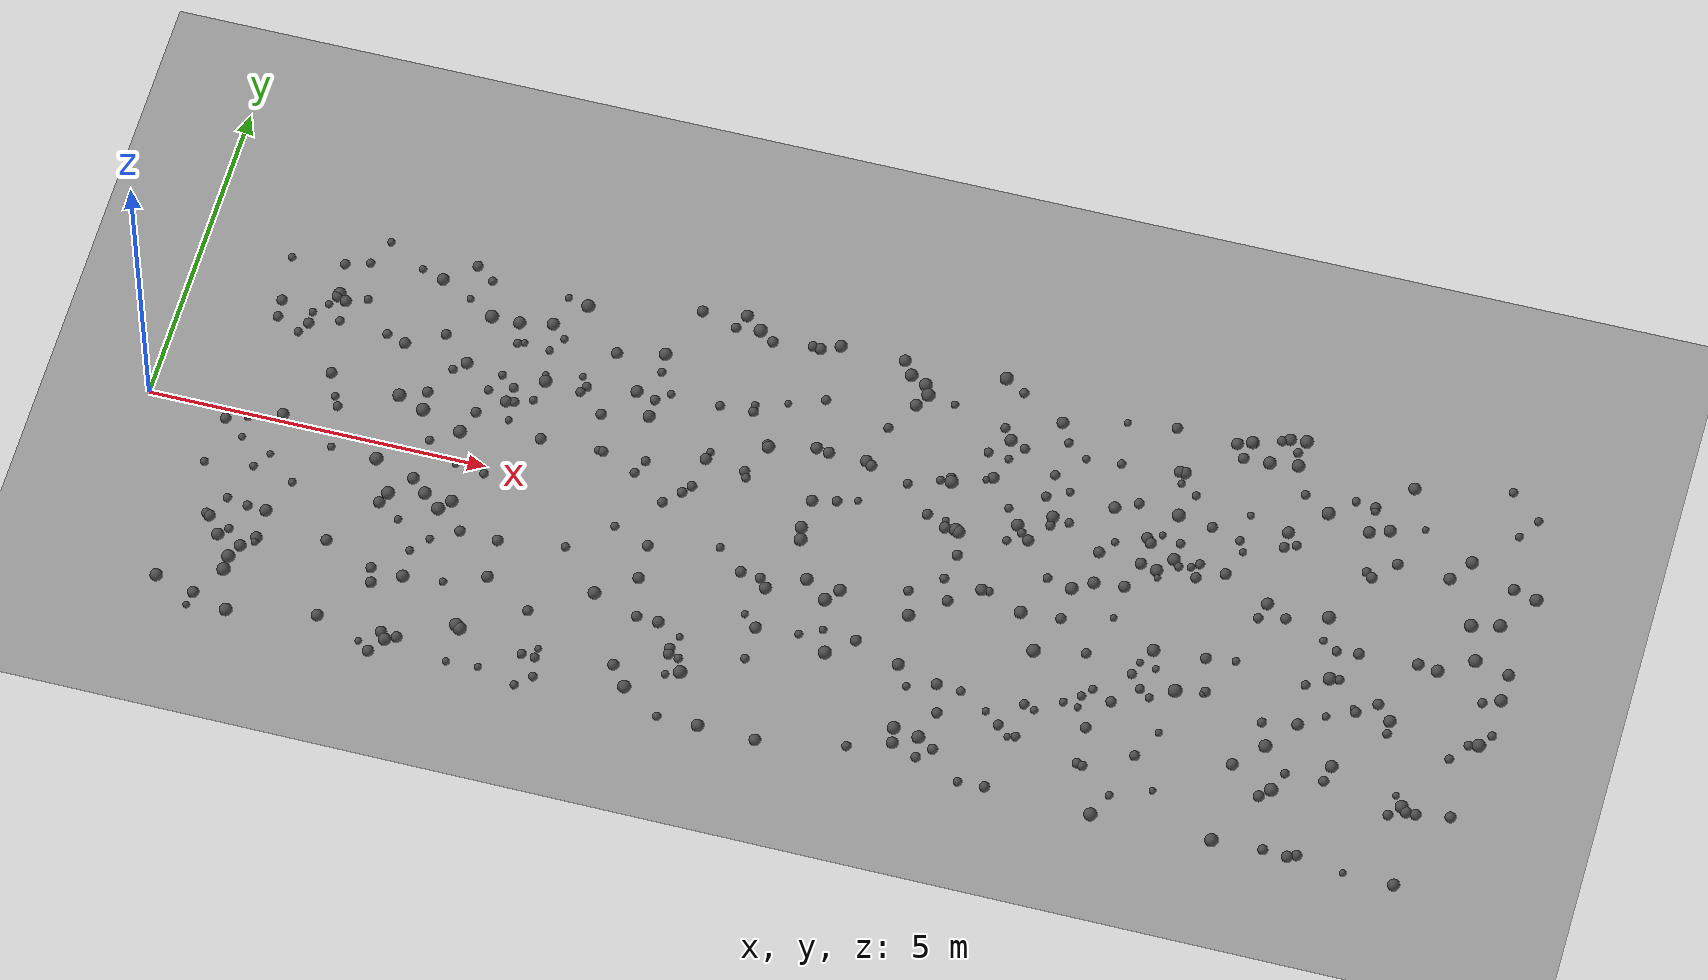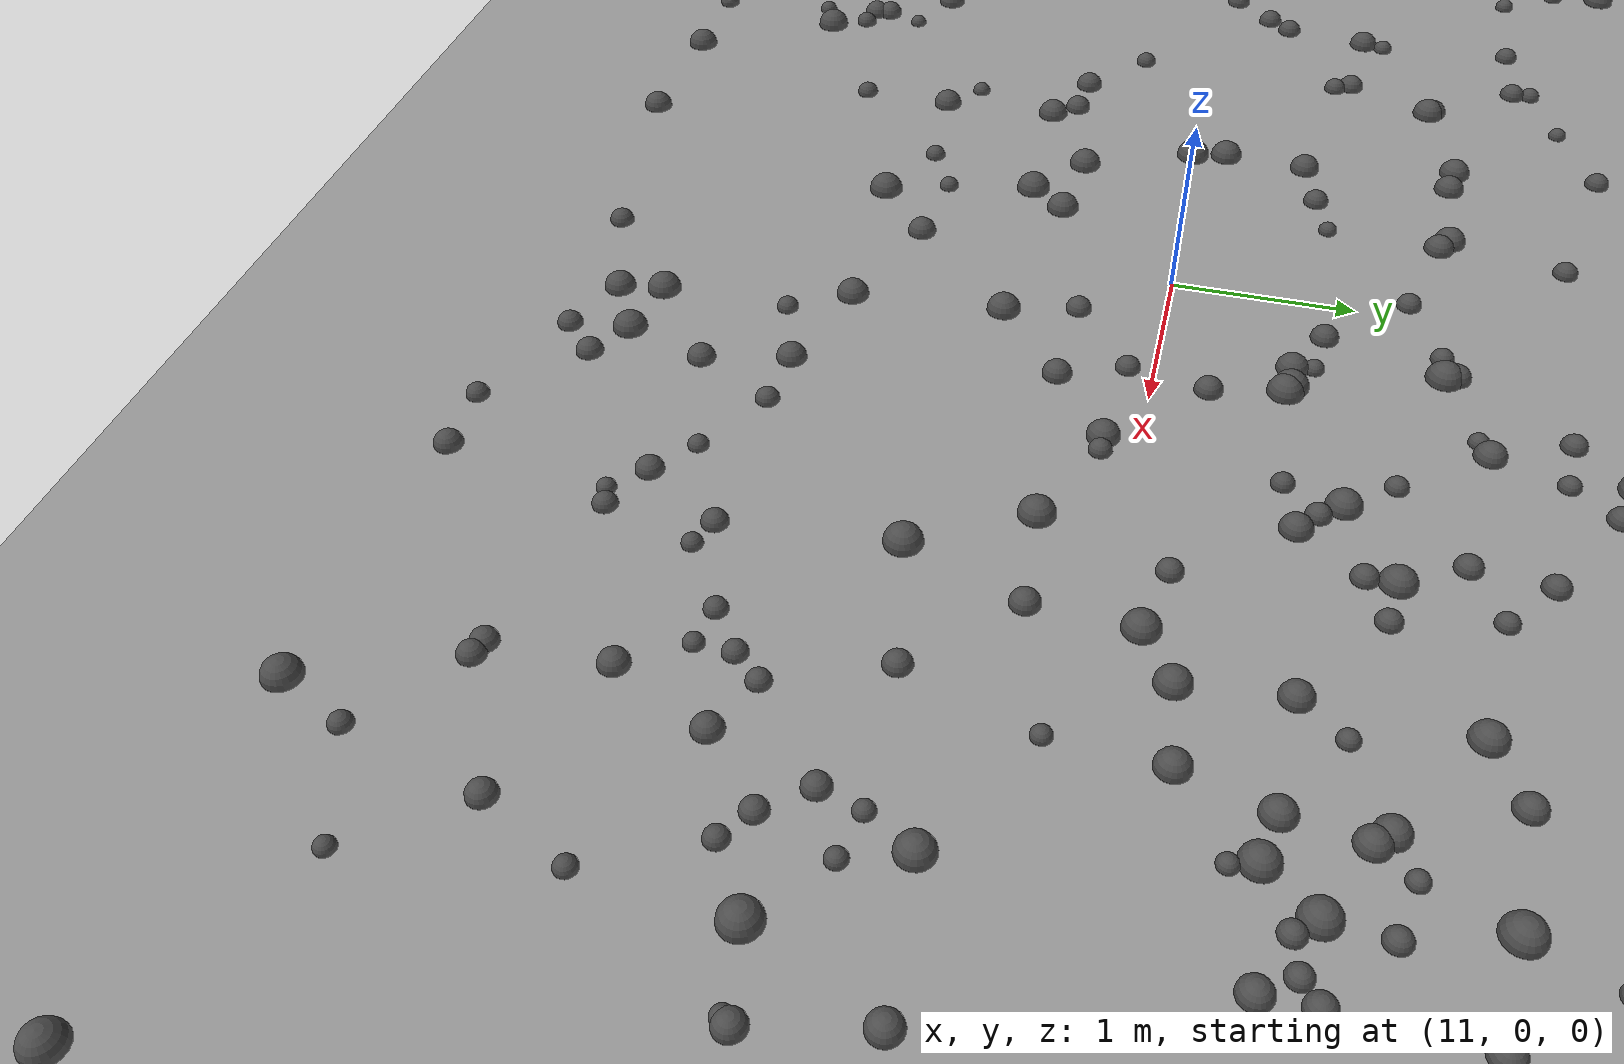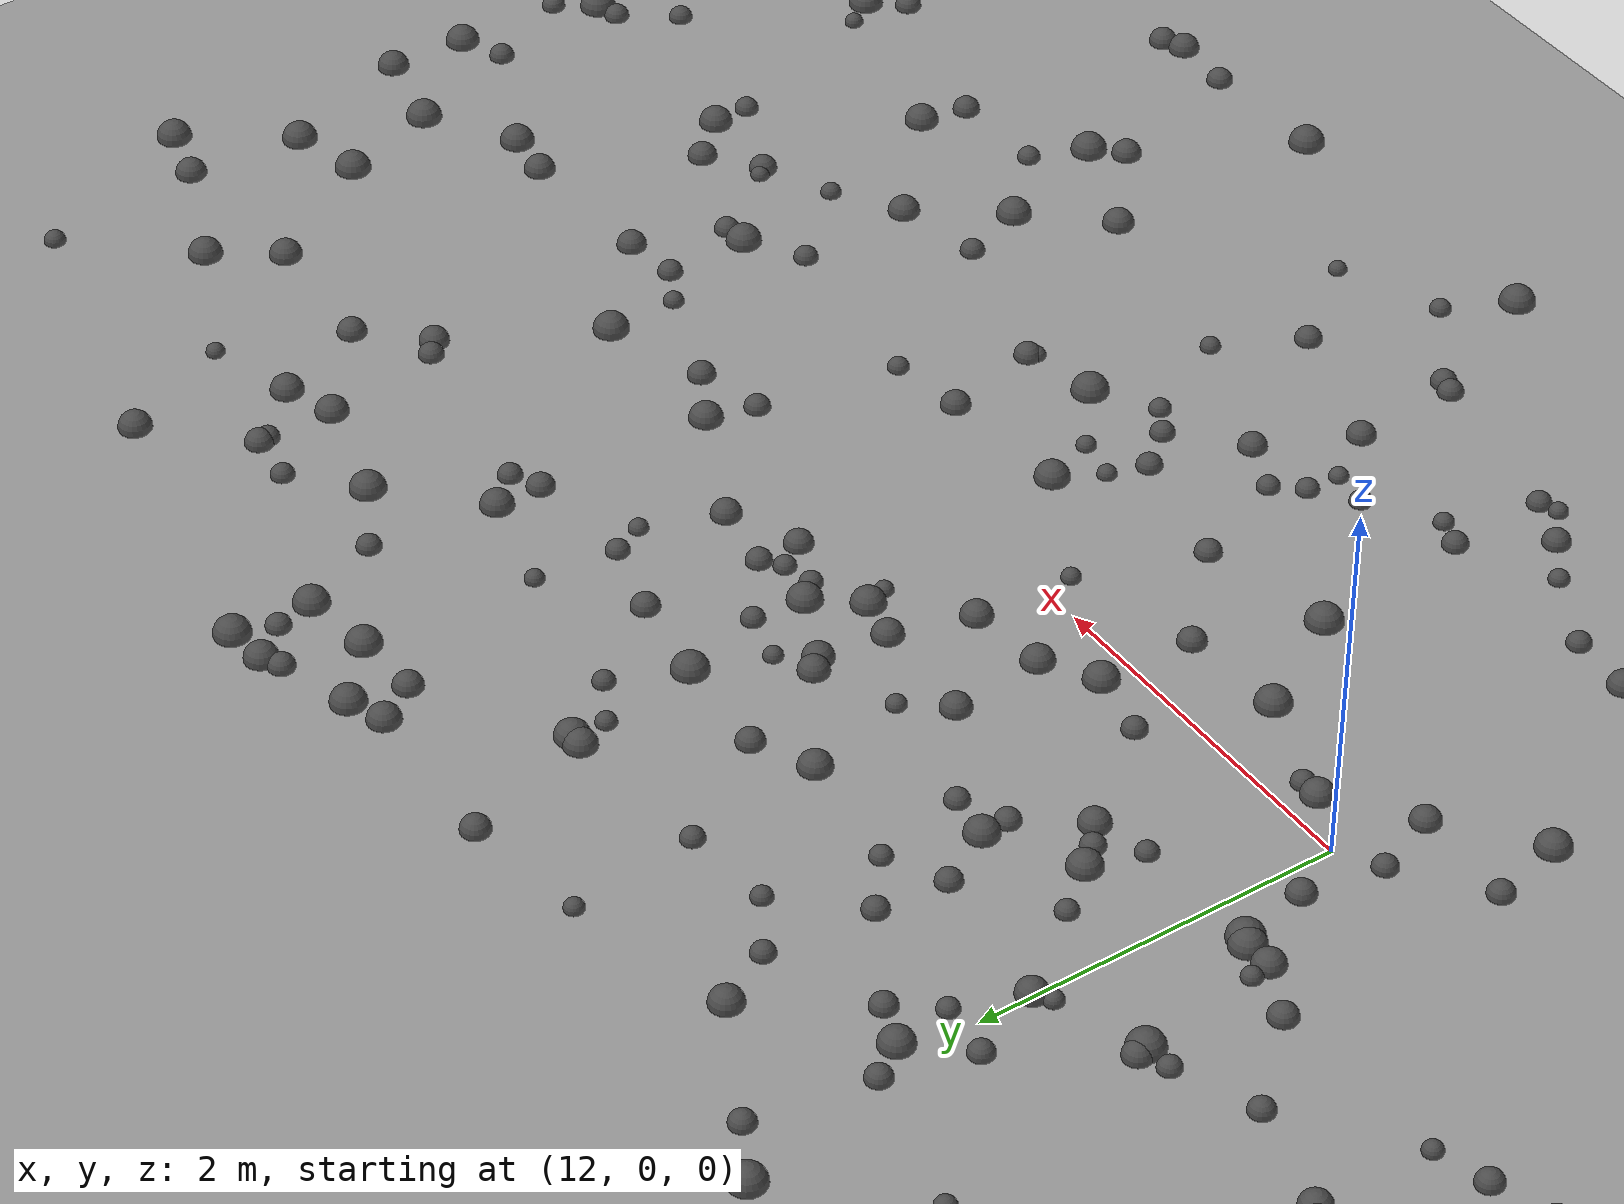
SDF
<?xml version="1.0" ?>
<sdf version="1.8">
  <world name="bumpy_world">
    <physics name="1ms" type="ignored">
      <max_step_size>0.001</max_step_size>
      <real_time_factor>1.0</real_time_factor>
    </physics>
    <plugin filename="gz-sim-physics-system" name="gz::sim::systems::Physics"/>
    <plugin filename="gz-sim-user-commands-system" name="gz::sim::systems::UserCommands"/>
    <plugin filename="gz-sim-scene-broadcaster-system" name="gz::sim::systems::SceneBroadcaster"/>

    <light type="directional" name="sun">
      <cast_shadows>true</cast_shadows>
      <pose>0 0 10 0 0 0</pose>
      <diffuse>0.8 0.8 0.8 1</diffuse>
      <specular>0.2 0.2 0.2 1</specular>
      <attenuation><range>1000</range><constant>0.9</constant><linear>0.01</linear><quadratic>0.001</quadratic></attenuation>
      <direction>-0.5 0.1 -0.9</direction>
    </light>

    <model name="ground_plane">
      <static>true</static>
      <link name="link">
        <collision name="collision">
          <geometry><plane><normal>0 0 1</normal><size>100 100</size></plane></geometry>
        </collision>
        <visual name="visual">
          <geometry><plane><normal>0 0 1</normal><size>100 100</size></plane></geometry>
          <material><ambient>0.6 0.6 0.6 1</ambient><diffuse>0.6 0.6 0.6 1</diffuse></material>
        </visual>
      </link>
    </model>

    <model name="bump_0">
      <static>true</static>
      <pose>17.07979871296993 -2.3560940418442513 0.0 0 0 0</pose>
      <link name="link">
        <collision name="collision"><geometry><sphere><radius>0.0981647486818742</radius></sphere></geometry><surface><friction><ode><mu>100.0</mu><mu2>100.0</mu2></ode></friction></surface></collision>
        <visual name="visual"><geometry><sphere><radius>0.0981647486818742</radius></sphere></geometry>
        <material><ambient>0.3 0.3 0.3 1</ambient><diffuse>0.3 0.3 0.3 1</diffuse></material>
        </visual>
      </link>
    </model>

    <model name="bump_1">
      <static>true</static>
      <pose>4.375699444359473 -2.0842353457720866 0.0 0 0 0</pose>
      <link name="link">
        <collision name="collision"><geometry><sphere><radius>0.09185490365605613</radius></sphere></geometry><surface><friction><ode><mu>100.0</mu><mu2>100.0</mu2></ode></friction></surface></collision>
        <visual name="visual"><geometry><sphere><radius>0.09185490365605613</radius></sphere></geometry>
        <material><ambient>0.3 0.3 0.3 1</ambient><diffuse>0.3 0.3 0.3 1</diffuse></material>
        </visual>
      </link>
    </model>

    <model name="bump_2">
      <static>true</static>
      <pose>13.304579363777297 -2.464975682810359 0.0 0 0 0</pose>
      <link name="link">
        <collision name="collision"><geometry><sphere><radius>0.051483868694990956</radius></sphere></geometry><surface><friction><ode><mu>100.0</mu><mu2>100.0</mu2></ode></friction></surface></collision>
        <visual name="visual"><geometry><sphere><radius>0.051483868694990956</radius></sphere></geometry>
        <material><ambient>0.3 0.3 0.3 1</ambient><diffuse>0.3 0.3 0.3 1</diffuse></material>
        </visual>
      </link>
    </model>

    <model name="bump_3">
      <static>true</static>
      <pose>11.931157695273809 1.6394047522858175 0.0 0 0 0</pose>
      <link name="link">
        <collision name="collision"><geometry><sphere><radius>0.053579488928655966</radius></sphere></geometry><surface><friction><ode><mu>100.0</mu><mu2>100.0</mu2></ode></friction></surface></collision>
        <visual name="visual"><geometry><sphere><radius>0.053579488928655966</radius></sphere></geometry>
        <material><ambient>0.3 0.3 0.3 1</ambient><diffuse>0.3 0.3 0.3 1</diffuse></material>
        </visual>
      </link>
    </model>

    <model name="bump_4">
      <static>true</static>
      <pose>12.55489104031081 1.0059284895138196 0.0 0 0 0</pose>
      <link name="link">
        <collision name="collision"><geometry><sphere><radius>0.09172294633652742</radius></sphere></geometry><surface><friction><ode><mu>100.0</mu><mu2>100.0</mu2></ode></friction></surface></collision>
        <visual name="visual"><geometry><sphere><radius>0.09172294633652742</radius></sphere></geometry>
        <material><ambient>0.3 0.3 0.3 1</ambient><diffuse>0.3 0.3 0.3 1</diffuse></material>
        </visual>
      </link>
    </model>

    <model name="bump_5">
      <static>true</static>
      <pose>14.562588807561559 2.482431439217339 0.0 0 0 0</pose>
      <link name="link">
        <collision name="collision"><geometry><sphere><radius>0.08768449537127662</radius></sphere></geometry><surface><friction><ode><mu>100.0</mu><mu2>100.0</mu2></ode></friction></surface></collision>
        <visual name="visual"><geometry><sphere><radius>0.08768449537127662</radius></sphere></geometry>
        <material><ambient>0.3 0.3 0.3 1</ambient><diffuse>0.3 0.3 0.3 1</diffuse></material>
        </visual>
      </link>
    </model>

    <model name="bump_6">
      <static>true</static>
      <pose>19.598575563349467 -2.1446980017574346 0.0 0 0 0</pose>
      <link name="link">
        <collision name="collision"><geometry><sphere><radius>0.08097896778327451</radius></sphere></geometry><surface><friction><ode><mu>100.0</mu><mu2>100.0</mu2></ode></friction></surface></collision>
        <visual name="visual"><geometry><sphere><radius>0.08097896778327451</radius></sphere></geometry>
        <material><ambient>0.3 0.3 0.3 1</ambient><diffuse>0.3 0.3 0.3 1</diffuse></material>
        </visual>
      </link>
    </model>

    <model name="bump_7">
      <static>true</static>
      <pose>4.578840665991967 -3.0889073012254835 0.0 0 0 0</pose>
      <link name="link">
        <collision name="collision"><geometry><sphere><radius>0.08110118816827837</radius></sphere></geometry><surface><friction><ode><mu>100.0</mu><mu2>100.0</mu2></ode></friction></surface></collision>
        <visual name="visual"><geometry><sphere><radius>0.08110118816827837</radius></sphere></geometry>
        <material><ambient>0.3 0.3 0.3 1</ambient><diffuse>0.3 0.3 0.3 1</diffuse></material>
        </visual>
      </link>
    </model>

    <model name="bump_8">
      <static>true</static>
      <pose>17.19856203481358 -3.3353982341826844 0.0 0 0 0</pose>
      <link name="link">
        <collision name="collision"><geometry><sphere><radius>0.07238395450279482</radius></sphere></geometry><surface><friction><ode><mu>100.0</mu><mu2>100.0</mu2></ode></friction></surface></collision>
        <visual name="visual"><geometry><sphere><radius>0.07238395450279482</radius></sphere></geometry>
        <material><ambient>0.3 0.3 0.3 1</ambient><diffuse>0.3 0.3 0.3 1</diffuse></material>
        </visual>
      </link>
    </model>

    <model name="bump_9">
      <static>true</static>
      <pose>17.680362293708182 2.2786300804662707 0.0 0 0 0</pose>
      <link name="link">
        <collision name="collision"><geometry><sphere><radius>0.08963292703473585</radius></sphere></geometry><surface><friction><ode><mu>100.0</mu><mu2>100.0</mu2></ode></friction></surface></collision>
        <visual name="visual"><geometry><sphere><radius>0.08963292703473585</radius></sphere></geometry>
        <material><ambient>0.3 0.3 0.3 1</ambient><diffuse>0.3 0.3 0.3 1</diffuse></material>
        </visual>
      </link>
    </model>

    <model name="bump_10">
      <static>true</static>
      <pose>8.074093619460154 -1.8913849508941816 0.0 0 0 0</pose>
      <link name="link">
        <collision name="collision"><geometry><sphere><radius>0.08665526799791093</radius></sphere></geometry><surface><friction><ode><mu>100.0</mu><mu2>100.0</mu2></ode></friction></surface></collision>
        <visual name="visual"><geometry><sphere><radius>0.08665526799791093</radius></sphere></geometry>
        <material><ambient>0.3 0.3 0.3 1</ambient><diffuse>0.3 0.3 0.3 1</diffuse></material>
        </visual>
      </link>
    </model>

    <model name="bump_11">
      <static>true</static>
      <pose>2.9970924430199055 1.83390502286999 0.0 0 0 0</pose>
      <link name="link">
        <collision name="collision"><geometry><sphere><radius>0.06836493312915833</radius></sphere></geometry><surface><friction><ode><mu>100.0</mu><mu2>100.0</mu2></ode></friction></surface></collision>
        <visual name="visual"><geometry><sphere><radius>0.06836493312915833</radius></sphere></geometry>
        <material><ambient>0.3 0.3 0.3 1</ambient><diffuse>0.3 0.3 0.3 1</diffuse></material>
        </visual>
      </link>
    </model>

    <model name="bump_12">
      <static>true</static>
      <pose>11.522102334728567 -1.7018754114444579 0.0 0 0 0</pose>
      <link name="link">
        <collision name="collision"><geometry><sphere><radius>0.08945290259393307</radius></sphere></geometry><surface><friction><ode><mu>100.0</mu><mu2>100.0</mu2></ode></friction></surface></collision>
        <visual name="visual"><geometry><sphere><radius>0.08945290259393307</radius></sphere></geometry>
        <material><ambient>0.3 0.3 0.3 1</ambient><diffuse>0.3 0.3 0.3 1</diffuse></material>
        </visual>
      </link>
    </model>

    <model name="bump_13">
      <static>true</static>
      <pose>4.428357708878181 -3.169123840835509 0.0 0 0 0</pose>
      <link name="link">
        <collision name="collision"><geometry><sphere><radius>0.09192973632237827</radius></sphere></geometry><surface><friction><ode><mu>100.0</mu><mu2>100.0</mu2></ode></friction></surface></collision>
        <visual name="visual"><geometry><sphere><radius>0.09192973632237827</radius></sphere></geometry>
        <material><ambient>0.3 0.3 0.3 1</ambient><diffuse>0.3 0.3 0.3 1</diffuse></material>
        </visual>
      </link>
    </model>

    <model name="bump_14">
      <static>true</static>
      <pose>10.643117851737946 2.6129079449877457 0.0 0 0 0</pose>
      <link name="link">
        <collision name="collision"><geometry><sphere><radius>0.09134821140151704</radius></sphere></geometry><surface><friction><ode><mu>100.0</mu><mu2>100.0</mu2></ode></friction></surface></collision>
        <visual name="visual"><geometry><sphere><radius>0.09134821140151704</radius></sphere></geometry>
        <material><ambient>0.3 0.3 0.3 1</ambient><diffuse>0.3 0.3 0.3 1</diffuse></material>
        </visual>
      </link>
    </model>

    <model name="bump_15">
      <static>true</static>
      <pose>2.5594423021961528 2.342710506935444 0.0 0 0 0</pose>
      <link name="link">
        <collision name="collision"><geometry><sphere><radius>0.06365721138681198</radius></sphere></geometry><surface><friction><ode><mu>100.0</mu><mu2>100.0</mu2></ode></friction></surface></collision>
        <visual name="visual"><geometry><sphere><radius>0.06365721138681198</radius></sphere></geometry>
        <material><ambient>0.3 0.3 0.3 1</ambient><diffuse>0.3 0.3 0.3 1</diffuse></material>
        </visual>
      </link>
    </model>

    <model name="bump_16">
      <static>true</static>
      <pose>9.421385301899686 -1.6260992034511779 0.0 0 0 0</pose>
      <link name="link">
        <collision name="collision"><geometry><sphere><radius>0.08546456388983416</radius></sphere></geometry><surface><friction><ode><mu>100.0</mu><mu2>100.0</mu2></ode></friction></surface></collision>
        <visual name="visual"><geometry><sphere><radius>0.08546456388983416</radius></sphere></geometry>
        <material><ambient>0.3 0.3 0.3 1</ambient><diffuse>0.3 0.3 0.3 1</diffuse></material>
        </visual>
      </link>
    </model>

    <model name="bump_17">
      <static>true</static>
      <pose>3.4514245521246463 -0.26661385392774495 0.0 0 0 0</pose>
      <link name="link">
        <collision name="collision"><geometry><sphere><radius>0.09747261459395384</radius></sphere></geometry><surface><friction><ode><mu>100.0</mu><mu2>100.0</mu2></ode></friction></surface></collision>
        <visual name="visual"><geometry><sphere><radius>0.09747261459395384</radius></sphere></geometry>
        <material><ambient>0.3 0.3 0.3 1</ambient><diffuse>0.3 0.3 0.3 1</diffuse></material>
        </visual>
      </link>
    </model>

    <model name="bump_18">
      <static>true</static>
      <pose>12.022463642345118 1.693123177917606 0.0 0 0 0</pose>
      <link name="link">
        <collision name="collision"><geometry><sphere><radius>0.08342939061276286</radius></sphere></geometry><surface><friction><ode><mu>100.0</mu><mu2>100.0</mu2></ode></friction></surface></collision>
        <visual name="visual"><geometry><sphere><radius>0.08342939061276286</radius></sphere></geometry>
        <material><ambient>0.3 0.3 0.3 1</ambient><diffuse>0.3 0.3 0.3 1</diffuse></material>
        </visual>
      </link>
    </model>

    <model name="bump_19">
      <static>true</static>
      <pose>3.1600458979560577 -1.781941884311565 0.0 0 0 0</pose>
      <link name="link">
        <collision name="collision"><geometry><sphere><radius>0.08271994072516169</radius></sphere></geometry><surface><friction><ode><mu>100.0</mu><mu2>100.0</mu2></ode></friction></surface></collision>
        <visual name="visual"><geometry><sphere><radius>0.08271994072516169</radius></sphere></geometry>
        <material><ambient>0.3 0.3 0.3 1</ambient><diffuse>0.3 0.3 0.3 1</diffuse></material>
        </visual>
      </link>
    </model>

    <model name="bump_20">
      <static>true</static>
      <pose>4.474462683840456 0.4849099776785515 0.0 0 0 0</pose>
      <link name="link">
        <collision name="collision"><geometry><sphere><radius>0.0968737511445553</radius></sphere></geometry><surface><friction><ode><mu>100.0</mu><mu2>100.0</mu2></ode></friction></surface></collision>
        <visual name="visual"><geometry><sphere><radius>0.0968737511445553</radius></sphere></geometry>
        <material><ambient>0.3 0.3 0.3 1</ambient><diffuse>0.3 0.3 0.3 1</diffuse></material>
        </visual>
      </link>
    </model>

    <model name="bump_21">
      <static>true</static>
      <pose>14.635420288345205 2.481698815405207 0.0 0 0 0</pose>
      <link name="link">
        <collision name="collision"><geometry><sphere><radius>0.09113718749873549</radius></sphere></geometry><surface><friction><ode><mu>100.0</mu><mu2>100.0</mu2></ode></friction></surface></collision>
        <visual name="visual"><geometry><sphere><radius>0.09113718749873549</radius></sphere></geometry>
        <material><ambient>0.3 0.3 0.3 1</ambient><diffuse>0.3 0.3 0.3 1</diffuse></material>
        </visual>
      </link>
    </model>

    <model name="bump_22">
      <static>true</static>
      <pose>15.947673338106666 3.421388019658636 0.0 0 0 0</pose>
      <link name="link">
        <collision name="collision"><geometry><sphere><radius>0.08962710731348245</radius></sphere></geometry><surface><friction><ode><mu>100.0</mu><mu2>100.0</mu2></ode></friction></surface></collision>
        <visual name="visual"><geometry><sphere><radius>0.08962710731348245</radius></sphere></geometry>
        <material><ambient>0.3 0.3 0.3 1</ambient><diffuse>0.3 0.3 0.3 1</diffuse></material>
        </visual>
      </link>
    </model>

    <model name="bump_23">
      <static>true</static>
      <pose>7.207527420495198 1.8874109743500078 0.0 0 0 0</pose>
      <link name="link">
        <collision name="collision"><geometry><sphere><radius>0.057677577920670714</radius></sphere></geometry><surface><friction><ode><mu>100.0</mu><mu2>100.0</mu2></ode></friction></surface></collision>
        <visual name="visual"><geometry><sphere><radius>0.057677577920670714</radius></sphere></geometry>
        <material><ambient>0.3 0.3 0.3 1</ambient><diffuse>0.3 0.3 0.3 1</diffuse></material>
        </visual>
      </link>
    </model>

    <model name="bump_24">
      <static>true</static>
      <pose>17.099487515794102 2.639171686759317 0.0 0 0 0</pose>
      <link name="link">
        <collision name="collision"><geometry><sphere><radius>0.06339597844373478</radius></sphere></geometry><surface><friction><ode><mu>100.0</mu><mu2>100.0</mu2></ode></friction></surface></collision>
        <visual name="visual"><geometry><sphere><radius>0.06339597844373478</radius></sphere></geometry>
        <material><ambient>0.3 0.3 0.3 1</ambient><diffuse>0.3 0.3 0.3 1</diffuse></material>
        </visual>
      </link>
    </model>

    <model name="bump_25">
      <static>true</static>
      <pose>6.462320101021629 -1.0121938561316322 0.0 0 0 0</pose>
      <link name="link">
        <collision name="collision"><geometry><sphere><radius>0.0638348004299918</radius></sphere></geometry><surface><friction><ode><mu>100.0</mu><mu2>100.0</mu2></ode></friction></surface></collision>
        <visual name="visual"><geometry><sphere><radius>0.0638348004299918</radius></sphere></geometry>
        <material><ambient>0.3 0.3 0.3 1</ambient><diffuse>0.3 0.3 0.3 1</diffuse></material>
        </visual>
      </link>
    </model>

    <model name="bump_26">
      <static>true</static>
      <pose>9.975213831209803 0.7341309147829511 0.0 0 0 0</pose>
      <link name="link">
        <collision name="collision"><geometry><sphere><radius>0.0721345764446053</radius></sphere></geometry><surface><friction><ode><mu>100.0</mu><mu2>100.0</mu2></ode></friction></surface></collision>
        <visual name="visual"><geometry><sphere><radius>0.0721345764446053</radius></sphere></geometry>
        <material><ambient>0.3 0.3 0.3 1</ambient><diffuse>0.3 0.3 0.3 1</diffuse></material>
        </visual>
      </link>
    </model>

    <model name="bump_27">
      <static>true</static>
      <pose>5.0046693365978046 1.4117150593232077 0.0 0 0 0</pose>
      <link name="link">
        <collision name="collision"><geometry><sphere><radius>0.07152536064476334</radius></sphere></geometry><surface><friction><ode><mu>100.0</mu><mu2>100.0</mu2></ode></friction></surface></collision>
        <visual name="visual"><geometry><sphere><radius>0.07152536064476334</radius></sphere></geometry>
        <material><ambient>0.3 0.3 0.3 1</ambient><diffuse>0.3 0.3 0.3 1</diffuse></material>
        </visual>
      </link>
    </model>

    <model name="bump_28">
      <static>true</static>
      <pose>2.6015680022302448 3.391294897895473 0.0 0 0 0</pose>
      <link name="link">
        <collision name="collision"><geometry><sphere><radius>0.058801889831425466</radius></sphere></geometry><surface><friction><ode><mu>100.0</mu><mu2>100.0</mu2></ode></friction></surface></collision>
        <visual name="visual"><geometry><sphere><radius>0.058801889831425466</radius></sphere></geometry>
        <material><ambient>0.3 0.3 0.3 1</ambient><diffuse>0.3 0.3 0.3 1</diffuse></material>
        </visual>
      </link>
    </model>

    <model name="bump_29">
      <static>true</static>
      <pose>8.472127452633984 -3.4096233397645346 0.0 0 0 0</pose>
      <link name="link">
        <collision name="collision"><geometry><sphere><radius>0.06352596708151205</radius></sphere></geometry><surface><friction><ode><mu>100.0</mu><mu2>100.0</mu2></ode></friction></surface></collision>
        <visual name="visual"><geometry><sphere><radius>0.06352596708151205</radius></sphere></geometry>
        <material><ambient>0.3 0.3 0.3 1</ambient><diffuse>0.3 0.3 0.3 1</diffuse></material>
        </visual>
      </link>
    </model>

    <model name="bump_30">
      <static>true</static>
      <pose>8.592691148763425 -2.618579676732703 0.0 0 0 0</pose>
      <link name="link">
        <collision name="collision"><geometry><sphere><radius>0.09846012316630356</radius></sphere></geometry><surface><friction><ode><mu>100.0</mu><mu2>100.0</mu2></ode></friction></surface></collision>
        <visual name="visual"><geometry><sphere><radius>0.09846012316630356</radius></sphere></geometry>
        <material><ambient>0.3 0.3 0.3 1</ambient><diffuse>0.3 0.3 0.3 1</diffuse></material>
        </visual>
      </link>
    </model>

    <model name="bump_31">
      <static>true</static>
      <pose>5.909472135789189 1.853494488348181 0.0 0 0 0</pose>
      <link name="link">
        <collision name="collision"><geometry><sphere><radius>0.052269502112679125</radius></sphere></geometry><surface><friction><ode><mu>100.0</mu><mu2>100.0</mu2></ode></friction></surface></collision>
        <visual name="visual"><geometry><sphere><radius>0.052269502112679125</radius></sphere></geometry>
        <material><ambient>0.3 0.3 0.3 1</ambient><diffuse>0.3 0.3 0.3 1</diffuse></material>
        </visual>
      </link>
    </model>

    <model name="bump_32">
      <static>true</static>
      <pose>16.472289125123126 -3.3695576696736778 0.0 0 0 0</pose>
      <link name="link">
        <collision name="collision"><geometry><sphere><radius>0.09800282768145768</radius></sphere></geometry><surface><friction><ode><mu>100.0</mu><mu2>100.0</mu2></ode></friction></surface></collision>
        <visual name="visual"><geometry><sphere><radius>0.09800282768145768</radius></sphere></geometry>
        <material><ambient>0.3 0.3 0.3 1</ambient><diffuse>0.3 0.3 0.3 1</diffuse></material>
        </visual>
      </link>
    </model>

    <model name="bump_33">
      <static>true</static>
      <pose>3.77704697894142 -0.7873846618750808 0.0 0 0 0</pose>
      <link name="link">
        <collision name="collision"><geometry><sphere><radius>0.09693993984139813</radius></sphere></geometry><surface><friction><ode><mu>100.0</mu><mu2>100.0</mu2></ode></friction></surface></collision>
        <visual name="visual"><geometry><sphere><radius>0.09693993984139813</radius></sphere></geometry>
        <material><ambient>0.3 0.3 0.3 1</ambient><diffuse>0.3 0.3 0.3 1</diffuse></material>
        </visual>
      </link>
    </model>

    <model name="bump_34">
      <static>true</static>
      <pose>15.211453152067746 1.0342373390313409 0.0 0 0 0</pose>
      <link name="link">
        <collision name="collision"><geometry><sphere><radius>0.06985104177228421</radius></sphere></geometry><surface><friction><ode><mu>100.0</mu><mu2>100.0</mu2></ode></friction></surface></collision>
        <visual name="visual"><geometry><sphere><radius>0.06985104177228421</radius></sphere></geometry>
        <material><ambient>0.3 0.3 0.3 1</ambient><diffuse>0.3 0.3 0.3 1</diffuse></material>
        </visual>
      </link>
    </model>

    <model name="bump_35">
      <static>true</static>
      <pose>15.387912402151585 -1.1148408915079688 0.0 0 0 0</pose>
      <link name="link">
        <collision name="collision"><geometry><sphere><radius>0.09988870792115631</radius></sphere></geometry><surface><friction><ode><mu>100.0</mu><mu2>100.0</mu2></ode></friction></surface></collision>
        <visual name="visual"><geometry><sphere><radius>0.09988870792115631</radius></sphere></geometry>
        <material><ambient>0.3 0.3 0.3 1</ambient><diffuse>0.3 0.3 0.3 1</diffuse></material>
        </visual>
      </link>
    </model>

    <model name="bump_36">
      <static>true</static>
      <pose>17.85340117132149 3.0641102025408147 0.0 0 0 0</pose>
      <link name="link">
        <collision name="collision"><geometry><sphere><radius>0.08968701825092837</radius></sphere></geometry><surface><friction><ode><mu>100.0</mu><mu2>100.0</mu2></ode></friction></surface></collision>
        <visual name="visual"><geometry><sphere><radius>0.08968701825092837</radius></sphere></geometry>
        <material><ambient>0.3 0.3 0.3 1</ambient><diffuse>0.3 0.3 0.3 1</diffuse></material>
        </visual>
      </link>
    </model>

    <model name="bump_37">
      <static>true</static>
      <pose>9.37552611108897 2.3650020926075372 0.0 0 0 0</pose>
      <link name="link">
        <collision name="collision"><geometry><sphere><radius>0.06940311289779658</radius></sphere></geometry><surface><friction><ode><mu>100.0</mu><mu2>100.0</mu2></ode></friction></surface></collision>
        <visual name="visual"><geometry><sphere><radius>0.06940311289779658</radius></sphere></geometry>
        <material><ambient>0.3 0.3 0.3 1</ambient><diffuse>0.3 0.3 0.3 1</diffuse></material>
        </visual>
      </link>
    </model>

    <model name="bump_38">
      <static>true</static>
      <pose>16.18278624122245 3.447483160343883 0.0 0 0 0</pose>
      <link name="link">
        <collision name="collision"><geometry><sphere><radius>0.09750943610712903</radius></sphere></geometry><surface><friction><ode><mu>100.0</mu><mu2>100.0</mu2></ode></friction></surface></collision>
        <visual name="visual"><geometry><sphere><radius>0.09750943610712903</radius></sphere></geometry>
        <material><ambient>0.3 0.3 0.3 1</ambient><diffuse>0.3 0.3 0.3 1</diffuse></material>
        </visual>
      </link>
    </model>

    <model name="bump_39">
      <static>true</static>
      <pose>10.765315254485404 2.82722787600013 0.0 0 0 0</pose>
      <link name="link">
        <collision name="collision"><geometry><sphere><radius>0.09995415081091778</radius></sphere></geometry><surface><friction><ode><mu>100.0</mu><mu2>100.0</mu2></ode></friction></surface></collision>
        <visual name="visual"><geometry><sphere><radius>0.09995415081091778</radius></sphere></geometry>
        <material><ambient>0.3 0.3 0.3 1</ambient><diffuse>0.3 0.3 0.3 1</diffuse></material>
        </visual>
      </link>
    </model>

    <model name="bump_40">
      <static>true</static>
      <pose>7.81064455543238 0.3085803133527678 0.0 0 0 0</pose>
      <link name="link">
        <collision name="collision"><geometry><sphere><radius>0.07399396648756375</radius></sphere></geometry><surface><friction><ode><mu>100.0</mu><mu2>100.0</mu2></ode></friction></surface></collision>
        <visual name="visual"><geometry><sphere><radius>0.07399396648756375</radius></sphere></geometry>
        <material><ambient>0.3 0.3 0.3 1</ambient><diffuse>0.3 0.3 0.3 1</diffuse></material>
        </visual>
      </link>
    </model>

    <model name="bump_41">
      <static>true</static>
      <pose>13.186478670259566 0.24808822148255016 0.0 0 0 0</pose>
      <link name="link">
        <collision name="collision"><geometry><sphere><radius>0.06720600954557636</radius></sphere></geometry><surface><friction><ode><mu>100.0</mu><mu2>100.0</mu2></ode></friction></surface></collision>
        <visual name="visual"><geometry><sphere><radius>0.06720600954557636</radius></sphere></geometry>
        <material><ambient>0.3 0.3 0.3 1</ambient><diffuse>0.3 0.3 0.3 1</diffuse></material>
        </visual>
      </link>
    </model>

    <model name="bump_42">
      <static>true</static>
      <pose>15.48329186325271 -2.7985686660390834 0.0 0 0 0</pose>
      <link name="link">
        <collision name="collision"><geometry><sphere><radius>0.0503309574699336</radius></sphere></geometry><surface><friction><ode><mu>100.0</mu><mu2>100.0</mu2></ode></friction></surface></collision>
        <visual name="visual"><geometry><sphere><radius>0.0503309574699336</radius></sphere></geometry>
        <material><ambient>0.3 0.3 0.3 1</ambient><diffuse>0.3 0.3 0.3 1</diffuse></material>
        </visual>
      </link>
    </model>

    <model name="bump_43">
      <static>true</static>
      <pose>14.028422960162406 -0.8341455465728265 0.0 0 0 0</pose>
      <link name="link">
        <collision name="collision"><geometry><sphere><radius>0.0718243421118471</radius></sphere></geometry><surface><friction><ode><mu>100.0</mu><mu2>100.0</mu2></ode></friction></surface></collision>
        <visual name="visual"><geometry><sphere><radius>0.0718243421118471</radius></sphere></geometry>
        <material><ambient>0.3 0.3 0.3 1</ambient><diffuse>0.3 0.3 0.3 1</diffuse></material>
        </visual>
      </link>
    </model>

    <model name="bump_44">
      <static>true</static>
      <pose>7.905633032826282 3.4776121564256206 0.0 0 0 0</pose>
      <link name="link">
        <collision name="collision"><geometry><sphere><radius>0.09104344656485358</radius></sphere></geometry><surface><friction><ode><mu>100.0</mu><mu2>100.0</mu2></ode></friction></surface></collision>
        <visual name="visual"><geometry><sphere><radius>0.09104344656485358</radius></sphere></geometry>
        <material><ambient>0.3 0.3 0.3 1</ambient><diffuse>0.3 0.3 0.3 1</diffuse></material>
        </visual>
      </link>
    </model>

    <model name="bump_45">
      <static>true</static>
      <pose>4.539434740777375 -0.8569614264850611 0.0 0 0 0</pose>
      <link name="link">
        <collision name="collision"><geometry><sphere><radius>0.09726638559245274</radius></sphere></geometry><surface><friction><ode><mu>100.0</mu><mu2>100.0</mu2></ode></friction></surface></collision>
        <visual name="visual"><geometry><sphere><radius>0.09726638559245274</radius></sphere></geometry>
        <material><ambient>0.3 0.3 0.3 1</ambient><diffuse>0.3 0.3 0.3 1</diffuse></material>
        </visual>
      </link>
    </model>

    <model name="bump_46">
      <static>true</static>
      <pose>16.689288665471317 -1.3073775609994667 0.0 0 0 0</pose>
      <link name="link">
        <collision name="collision"><geometry><sphere><radius>0.06724745304326575</radius></sphere></geometry><surface><friction><ode><mu>100.0</mu><mu2>100.0</mu2></ode></friction></surface></collision>
        <visual name="visual"><geometry><sphere><radius>0.06724745304326575</radius></sphere></geometry>
        <material><ambient>0.3 0.3 0.3 1</ambient><diffuse>0.3 0.3 0.3 1</diffuse></material>
        </visual>
      </link>
    </model>

    <model name="bump_47">
      <static>true</static>
      <pose>17.389970325876025 2.6067973228167007 0.0 0 0 0</pose>
      <link name="link">
        <collision name="collision"><geometry><sphere><radius>0.07701099163247777</radius></sphere></geometry><surface><friction><ode><mu>100.0</mu><mu2>100.0</mu2></ode></friction></surface></collision>
        <visual name="visual"><geometry><sphere><radius>0.07701099163247777</radius></sphere></geometry>
        <material><ambient>0.3 0.3 0.3 1</ambient><diffuse>0.3 0.3 0.3 1</diffuse></material>
        </visual>
      </link>
    </model>

    <model name="bump_48">
      <static>true</static>
      <pose>10.243681844997505 -0.9185356339324291 0.0 0 0 0</pose>
      <link name="link">
        <collision name="collision"><geometry><sphere><radius>0.09749525561380185</radius></sphere></geometry><surface><friction><ode><mu>100.0</mu><mu2>100.0</mu2></ode></friction></surface></collision>
        <visual name="visual"><geometry><sphere><radius>0.09749525561380185</radius></sphere></geometry>
        <material><ambient>0.3 0.3 0.3 1</ambient><diffuse>0.3 0.3 0.3 1</diffuse></material>
        </visual>
      </link>
    </model>

    <model name="bump_49">
      <static>true</static>
      <pose>7.652648440351816 -2.7402711798300925 0.0 0 0 0</pose>
      <link name="link">
        <collision name="collision"><geometry><sphere><radius>0.08290568650594414</radius></sphere></geometry><surface><friction><ode><mu>100.0</mu><mu2>100.0</mu2></ode></friction></surface></collision>
        <visual name="visual"><geometry><sphere><radius>0.08290568650594414</radius></sphere></geometry>
        <material><ambient>0.3 0.3 0.3 1</ambient><diffuse>0.3 0.3 0.3 1</diffuse></material>
        </visual>
      </link>
    </model>

    <model name="bump_50">
      <static>true</static>
      <pose>3.858306326417391 0.7095792104071936 0.0 0 0 0</pose>
      <link name="link">
        <collision name="collision"><geometry><sphere><radius>0.09963918217281403</radius></sphere></geometry><surface><friction><ode><mu>100.0</mu><mu2>100.0</mu2></ode></friction></surface></collision>
        <visual name="visual"><geometry><sphere><radius>0.09963918217281403</radius></sphere></geometry>
        <material><ambient>0.3 0.3 0.3 1</ambient><diffuse>0.3 0.3 0.3 1</diffuse></material>
        </visual>
      </link>
    </model>

    <model name="bump_51">
      <static>true</static>
      <pose>10.685210819470418 2.9885323724850545 0.0 0 0 0</pose>
      <link name="link">
        <collision name="collision"><geometry><sphere><radius>0.09602896417148336</radius></sphere></geometry><surface><friction><ode><mu>100.0</mu><mu2>100.0</mu2></ode></friction></surface></collision>
        <visual name="visual"><geometry><sphere><radius>0.09602896417148336</radius></sphere></geometry>
        <material><ambient>0.3 0.3 0.3 1</ambient><diffuse>0.3 0.3 0.3 1</diffuse></material>
        </visual>
      </link>
    </model>

    <model name="bump_52">
      <static>true</static>
      <pose>1.7689268516161496 -1.9510097502811679 0.0 0 0 0</pose>
      <link name="link">
        <collision name="collision"><geometry><sphere><radius>0.06264346534399169</radius></sphere></geometry><surface><friction><ode><mu>100.0</mu><mu2>100.0</mu2></ode></friction></surface></collision>
        <visual name="visual"><geometry><sphere><radius>0.06264346534399169</radius></sphere></geometry>
        <material><ambient>0.3 0.3 0.3 1</ambient><diffuse>0.3 0.3 0.3 1</diffuse></material>
        </visual>
      </link>
    </model>

    <model name="bump_53">
      <static>true</static>
      <pose>4.254398319180079 -3.412807127269019 0.0 0 0 0</pose>
      <link name="link">
        <collision name="collision"><geometry><sphere><radius>0.08389991183557605</radius></sphere></geometry><surface><friction><ode><mu>100.0</mu><mu2>100.0</mu2></ode></friction></surface></collision>
        <visual name="visual"><geometry><sphere><radius>0.08389991183557605</radius></sphere></geometry>
        <material><ambient>0.3 0.3 0.3 1</ambient><diffuse>0.3 0.3 0.3 1</diffuse></material>
        </visual>
      </link>
    </model>

    <model name="bump_54">
      <static>true</static>
      <pose>15.334166617906272 -1.8458696237207382 0.0 0 0 0</pose>
      <link name="link">
        <collision name="collision"><geometry><sphere><radius>0.05483595023516709</radius></sphere></geometry><surface><friction><ode><mu>100.0</mu><mu2>100.0</mu2></ode></friction></surface></collision>
        <visual name="visual"><geometry><sphere><radius>0.05483595023516709</radius></sphere></geometry>
        <material><ambient>0.3 0.3 0.3 1</ambient><diffuse>0.3 0.3 0.3 1</diffuse></material>
        </visual>
      </link>
    </model>

    <model name="bump_55">
      <static>true</static>
      <pose>14.452666457167581 1.1982974309997125 0.0 0 0 0</pose>
      <link name="link">
        <collision name="collision"><geometry><sphere><radius>0.08306297502154905</radius></sphere></geometry><surface><friction><ode><mu>100.0</mu><mu2>100.0</mu2></ode></friction></surface></collision>
        <visual name="visual"><geometry><sphere><radius>0.08306297502154905</radius></sphere></geometry>
        <material><ambient>0.3 0.3 0.3 1</ambient><diffuse>0.3 0.3 0.3 1</diffuse></material>
        </visual>
      </link>
    </model>

    <model name="bump_56">
      <static>true</static>
      <pose>19.34686265752859 0.45887037669835706 0.0 0 0 0</pose>
      <link name="link">
        <collision name="collision"><geometry><sphere><radius>0.09757961537072722</radius></sphere></geometry><surface><friction><ode><mu>100.0</mu><mu2>100.0</mu2></ode></friction></surface></collision>
        <visual name="visual"><geometry><sphere><radius>0.09757961537072722</radius></sphere></geometry>
        <material><ambient>0.3 0.3 0.3 1</ambient><diffuse>0.3 0.3 0.3 1</diffuse></material>
        </visual>
      </link>
    </model>

    <model name="bump_57">
      <static>true</static>
      <pose>13.81408618550087 1.6502830108134567 0.0 0 0 0</pose>
      <link name="link">
        <collision name="collision"><geometry><sphere><radius>0.08965262909356791</radius></sphere></geometry><surface><friction><ode><mu>100.0</mu><mu2>100.0</mu2></ode></friction></surface></collision>
        <visual name="visual"><geometry><sphere><radius>0.08965262909356791</radius></sphere></geometry>
        <material><ambient>0.3 0.3 0.3 1</ambient><diffuse>0.3 0.3 0.3 1</diffuse></material>
        </visual>
      </link>
    </model>

    <model name="bump_58">
      <static>true</static>
      <pose>5.335336507484605 1.2789221906068722 0.0 0 0 0</pose>
      <link name="link">
        <collision name="collision"><geometry><sphere><radius>0.06108071147254923</radius></sphere></geometry><surface><friction><ode><mu>100.0</mu><mu2>100.0</mu2></ode></friction></surface></collision>
        <visual name="visual"><geometry><sphere><radius>0.06108071147254923</radius></sphere></geometry>
        <material><ambient>0.3 0.3 0.3 1</ambient><diffuse>0.3 0.3 0.3 1</diffuse></material>
        </visual>
      </link>
    </model>

    <model name="bump_59">
      <static>true</static>
      <pose>8.580519923631055 -0.45433019315059475 0.0 0 0 0</pose>
      <link name="link">
        <collision name="collision"><geometry><sphere><radius>0.06195867709120054</radius></sphere></geometry><surface><friction><ode><mu>100.0</mu><mu2>100.0</mu2></ode></friction></surface></collision>
        <visual name="visual"><geometry><sphere><radius>0.06195867709120054</radius></sphere></geometry>
        <material><ambient>0.3 0.3 0.3 1</ambient><diffuse>0.3 0.3 0.3 1</diffuse></material>
        </visual>
      </link>
    </model>

    <model name="bump_60">
      <static>true</static>
      <pose>15.438184745148275 3.2359624507849203 0.0 0 0 0</pose>
      <link name="link">
        <collision name="collision"><geometry><sphere><radius>0.09454059682721795</radius></sphere></geometry><surface><friction><ode><mu>100.0</mu><mu2>100.0</mu2></ode></friction></surface></collision>
        <visual name="visual"><geometry><sphere><radius>0.09454059682721795</radius></sphere></geometry>
        <material><ambient>0.3 0.3 0.3 1</ambient><diffuse>0.3 0.3 0.3 1</diffuse></material>
        </visual>
      </link>
    </model>

    <model name="bump_61">
      <static>true</static>
      <pose>2.1240586659767433 2.2813314408419876 0.0 0 0 0</pose>
      <link name="link">
        <collision name="collision"><geometry><sphere><radius>0.08591172824293025</radius></sphere></geometry><surface><friction><ode><mu>100.0</mu><mu2>100.0</mu2></ode></friction></surface></collision>
        <visual name="visual"><geometry><sphere><radius>0.08591172824293025</radius></sphere></geometry>
        <material><ambient>0.3 0.3 0.3 1</ambient><diffuse>0.3 0.3 0.3 1</diffuse></material>
        </visual>
      </link>
    </model>

    <model name="bump_62">
      <static>true</static>
      <pose>19.36389741438452 -1.2185180586353517 0.0 0 0 0</pose>
      <link name="link">
        <collision name="collision"><geometry><sphere><radius>0.06500405333480536</radius></sphere></geometry><surface><friction><ode><mu>100.0</mu><mu2>100.0</mu2></ode></friction></surface></collision>
        <visual name="visual"><geometry><sphere><radius>0.06500405333480536</radius></sphere></geometry>
        <material><ambient>0.3 0.3 0.3 1</ambient><diffuse>0.3 0.3 0.3 1</diffuse></material>
        </visual>
      </link>
    </model>

    <model name="bump_63">
      <static>true</static>
      <pose>13.218868417372912 2.3508512734720153 0.0 0 0 0</pose>
      <link name="link">
        <collision name="collision"><geometry><sphere><radius>0.05746723433186163</radius></sphere></geometry><surface><friction><ode><mu>100.0</mu><mu2>100.0</mu2></ode></friction></surface></collision>
        <visual name="visual"><geometry><sphere><radius>0.05746723433186163</radius></sphere></geometry>
        <material><ambient>0.3 0.3 0.3 1</ambient><diffuse>0.3 0.3 0.3 1</diffuse></material>
        </visual>
      </link>
    </model>

    <model name="bump_64">
      <static>true</static>
      <pose>12.764630342629564 0.793940911059722 0.0 0 0 0</pose>
      <link name="link">
        <collision name="collision"><geometry><sphere><radius>0.08375764279934095</radius></sphere></geometry><surface><friction><ode><mu>100.0</mu><mu2>100.0</mu2></ode></friction></surface></collision>
        <visual name="visual"><geometry><sphere><radius>0.08375764279934095</radius></sphere></geometry>
        <material><ambient>0.3 0.3 0.3 1</ambient><diffuse>0.3 0.3 0.3 1</diffuse></material>
        </visual>
      </link>
    </model>

    <model name="bump_65">
      <static>true</static>
      <pose>13.13478479729017 1.7444520159874166 0.0 0 0 0</pose>
      <link name="link">
        <collision name="collision"><geometry><sphere><radius>0.05983662861250227</radius></sphere></geometry><surface><friction><ode><mu>100.0</mu><mu2>100.0</mu2></ode></friction></surface></collision>
        <visual name="visual"><geometry><sphere><radius>0.05983662861250227</radius></sphere></geometry>
        <material><ambient>0.3 0.3 0.3 1</ambient><diffuse>0.3 0.3 0.3 1</diffuse></material>
        </visual>
      </link>
    </model>

    <model name="bump_66">
      <static>true</static>
      <pose>12.345960310114865 -2.9312546135932194 0.0 0 0 0</pose>
      <link name="link">
        <collision name="collision"><geometry><sphere><radius>0.07495913389079739</radius></sphere></geometry><surface><friction><ode><mu>100.0</mu><mu2>100.0</mu2></ode></friction></surface></collision>
        <visual name="visual"><geometry><sphere><radius>0.07495913389079739</radius></sphere></geometry>
        <material><ambient>0.3 0.3 0.3 1</ambient><diffuse>0.3 0.3 0.3 1</diffuse></material>
        </visual>
      </link>
    </model>

    <model name="bump_67">
      <static>true</static>
      <pose>9.380274728241485 -0.9470037858969937 0.0 0 0 0</pose>
      <link name="link">
        <collision name="collision"><geometry><sphere><radius>0.08968003674827485</radius></sphere></geometry><surface><friction><ode><mu>100.0</mu><mu2>100.0</mu2></ode></friction></surface></collision>
        <visual name="visual"><geometry><sphere><radius>0.08968003674827485</radius></sphere></geometry>
        <material><ambient>0.3 0.3 0.3 1</ambient><diffuse>0.3 0.3 0.3 1</diffuse></material>
        </visual>
      </link>
    </model>

    <model name="bump_68">
      <static>true</static>
      <pose>1.895110308128082 -2.402694578252322 0.0 0 0 0</pose>
      <link name="link">
        <collision name="collision"><geometry><sphere><radius>0.09760392777575799</radius></sphere></geometry><surface><friction><ode><mu>100.0</mu><mu2>100.0</mu2></ode></friction></surface></collision>
        <visual name="visual"><geometry><sphere><radius>0.09760392777575799</radius></sphere></geometry>
        <material><ambient>0.3 0.3 0.3 1</ambient><diffuse>0.3 0.3 0.3 1</diffuse></material>
        </visual>
      </link>
    </model>

    <model name="bump_69">
      <static>true</static>
      <pose>15.67469440505727 -0.4787279727878295 0.0 0 0 0</pose>
      <link name="link">
        <collision name="collision"><geometry><sphere><radius>0.07957818510238004</radius></sphere></geometry><surface><friction><ode><mu>100.0</mu><mu2>100.0</mu2></ode></friction></surface></collision>
        <visual name="visual"><geometry><sphere><radius>0.07957818510238004</radius></sphere></geometry>
        <material><ambient>0.3 0.3 0.3 1</ambient><diffuse>0.3 0.3 0.3 1</diffuse></material>
        </visual>
      </link>
    </model>

    <model name="bump_70">
      <static>true</static>
      <pose>1.1779168991081241 -0.15720439532591568 0.0 0 0 0</pose>
      <link name="link">
        <collision name="collision"><geometry><sphere><radius>0.07890660736814643</radius></sphere></geometry><surface><friction><ode><mu>100.0</mu><mu2>100.0</mu2></ode></friction></surface></collision>
        <visual name="visual"><geometry><sphere><radius>0.07890660736814643</radius></sphere></geometry>
        <material><ambient>0.3 0.3 0.3 1</ambient><diffuse>0.3 0.3 0.3 1</diffuse></material>
        </visual>
      </link>
    </model>

    <model name="bump_71">
      <static>true</static>
      <pose>6.4606164604068335 0.6933020968495835 0.0 0 0 0</pose>
      <link name="link">
        <collision name="collision"><geometry><sphere><radius>0.056842116591623304</radius></sphere></geometry><surface><friction><ode><mu>100.0</mu><mu2>100.0</mu2></ode></friction></surface></collision>
        <visual name="visual"><geometry><sphere><radius>0.056842116591623304</radius></sphere></geometry>
        <material><ambient>0.3 0.3 0.3 1</ambient><diffuse>0.3 0.3 0.3 1</diffuse></material>
        </visual>
      </link>
    </model>

    <model name="bump_72">
      <static>true</static>
      <pose>18.194704708540716 -0.5952552430335878 0.0 0 0 0</pose>
      <link name="link">
        <collision name="collision"><geometry><sphere><radius>0.08009505374050774</radius></sphere></geometry><surface><friction><ode><mu>100.0</mu><mu2>100.0</mu2></ode></friction></surface></collision>
        <visual name="visual"><geometry><sphere><radius>0.08009505374050774</radius></sphere></geometry>
        <material><ambient>0.3 0.3 0.3 1</ambient><diffuse>0.3 0.3 0.3 1</diffuse></material>
        </visual>
      </link>
    </model>

    <model name="bump_73">
      <static>true</static>
      <pose>18.418267715492547 -0.8287080446597059 0.0 0 0 0</pose>
      <link name="link">
        <collision name="collision"><geometry><sphere><radius>0.0906177599769456</radius></sphere></geometry><surface><friction><ode><mu>100.0</mu><mu2>100.0</mu2></ode></friction></surface></collision>
        <visual name="visual"><geometry><sphere><radius>0.0906177599769456</radius></sphere></geometry>
        <material><ambient>0.3 0.3 0.3 1</ambient><diffuse>0.3 0.3 0.3 1</diffuse></material>
        </visual>
      </link>
    </model>

    <model name="bump_74">
      <static>true</static>
      <pose>7.802795040569261 3.2390802744916227 0.0 0 0 0</pose>
      <link name="link">
        <collision name="collision"><geometry><sphere><radius>0.07205433554057636</radius></sphere></geometry><surface><friction><ode><mu>100.0</mu><mu2>100.0</mu2></ode></friction></surface></collision>
        <visual name="visual"><geometry><sphere><radius>0.07205433554057636</radius></sphere></geometry>
        <material><ambient>0.3 0.3 0.3 1</ambient><diffuse>0.3 0.3 0.3 1</diffuse></material>
        </visual>
      </link>
    </model>

    <model name="bump_75">
      <static>true</static>
      <pose>19.119949259111177 -2.2297628396833944 0.0 0 0 0</pose>
      <link name="link">
        <collision name="collision"><geometry><sphere><radius>0.07970548342831324</radius></sphere></geometry><surface><friction><ode><mu>100.0</mu><mu2>100.0</mu2></ode></friction></surface></collision>
        <visual name="visual"><geometry><sphere><radius>0.07970548342831324</radius></sphere></geometry>
        <material><ambient>0.3 0.3 0.3 1</ambient><diffuse>0.3 0.3 0.3 1</diffuse></material>
        </visual>
      </link>
    </model>

    <model name="bump_76">
      <static>true</static>
      <pose>4.846616131018106 2.1660713006287935 0.0 0 0 0</pose>
      <link name="link">
        <collision name="collision"><geometry><sphere><radius>0.06079181387232311</radius></sphere></geometry><surface><friction><ode><mu>100.0</mu><mu2>100.0</mu2></ode></friction></surface></collision>
        <visual name="visual"><geometry><sphere><radius>0.06079181387232311</radius></sphere></geometry>
        <material><ambient>0.3 0.3 0.3 1</ambient><diffuse>0.3 0.3 0.3 1</diffuse></material>
        </visual>
      </link>
    </model>

    <model name="bump_77">
      <static>true</static>
      <pose>1.3862601269019228 -1.7770314376125618 0.0 0 0 0</pose>
      <link name="link">
        <collision name="collision"><geometry><sphere><radius>0.07340652317562843</radius></sphere></geometry><surface><friction><ode><mu>100.0</mu><mu2>100.0</mu2></ode></friction></surface></collision>
        <visual name="visual"><geometry><sphere><radius>0.07340652317562843</radius></sphere></geometry>
        <material><ambient>0.3 0.3 0.3 1</ambient><diffuse>0.3 0.3 0.3 1</diffuse></material>
        </visual>
      </link>
    </model>

    <model name="bump_78">
      <static>true</static>
      <pose>19.55062454971193 1.1201559518139677 0.0 0 0 0</pose>
      <link name="link">
        <collision name="collision"><geometry><sphere><radius>0.09555177195987825</radius></sphere></geometry><surface><friction><ode><mu>100.0</mu><mu2>100.0</mu2></ode></friction></surface></collision>
        <visual name="visual"><geometry><sphere><radius>0.09555177195987825</radius></sphere></geometry>
        <material><ambient>0.3 0.3 0.3 1</ambient><diffuse>0.3 0.3 0.3 1</diffuse></material>
        </visual>
      </link>
    </model>

    <model name="bump_79">
      <static>true</static>
      <pose>8.86918294274917 2.161989821667313 0.0 0 0 0</pose>
      <link name="link">
        <collision name="collision"><geometry><sphere><radius>0.05203512853501087</radius></sphere></geometry><surface><friction><ode><mu>100.0</mu><mu2>100.0</mu2></ode></friction></surface></collision>
        <visual name="visual"><geometry><sphere><radius>0.05203512853501087</radius></sphere></geometry>
        <material><ambient>0.3 0.3 0.3 1</ambient><diffuse>0.3 0.3 0.3 1</diffuse></material>
        </visual>
      </link>
    </model>

    <model name="bump_80">
      <static>true</static>
      <pose>5.412592499783626 1.6367212688419084 0.0 0 0 0</pose>
      <link name="link">
        <collision name="collision"><geometry><sphere><radius>0.09444418449000878</radius></sphere></geometry><surface><friction><ode><mu>100.0</mu><mu2>100.0</mu2></ode></friction></surface></collision>
        <visual name="visual"><geometry><sphere><radius>0.09444418449000878</radius></sphere></geometry>
        <material><ambient>0.3 0.3 0.3 1</ambient><diffuse>0.3 0.3 0.3 1</diffuse></material>
        </visual>
      </link>
    </model>

    <model name="bump_81">
      <static>true</static>
      <pose>12.150259302899732 2.062354442706466 0.0 0 0 0</pose>
      <link name="link">
        <collision name="collision"><geometry><sphere><radius>0.05849020861925602</radius></sphere></geometry><surface><friction><ode><mu>100.0</mu><mu2>100.0</mu2></ode></friction></surface></collision>
        <visual name="visual"><geometry><sphere><radius>0.05849020861925602</radius></sphere></geometry>
        <material><ambient>0.3 0.3 0.3 1</ambient><diffuse>0.3 0.3 0.3 1</diffuse></material>
        </visual>
      </link>
    </model>

    <model name="bump_82">
      <static>true</static>
      <pose>16.45433861942613 -2.089132226662912 0.0 0 0 0</pose>
      <link name="link">
        <collision name="collision"><geometry><sphere><radius>0.08600865804093002</radius></sphere></geometry><surface><friction><ode><mu>100.0</mu><mu2>100.0</mu2></ode></friction></surface></collision>
        <visual name="visual"><geometry><sphere><radius>0.08600865804093002</radius></sphere></geometry>
        <material><ambient>0.3 0.3 0.3 1</ambient><diffuse>0.3 0.3 0.3 1</diffuse></material>
        </visual>
      </link>
    </model>

    <model name="bump_83">
      <static>true</static>
      <pose>18.42836967293816 -1.0365094989912547 0.0 0 0 0</pose>
      <link name="link">
        <collision name="collision"><geometry><sphere><radius>0.06494916149868013</radius></sphere></geometry><surface><friction><ode><mu>100.0</mu><mu2>100.0</mu2></ode></friction></surface></collision>
        <visual name="visual"><geometry><sphere><radius>0.06494916149868013</radius></sphere></geometry>
        <material><ambient>0.3 0.3 0.3 1</ambient><diffuse>0.3 0.3 0.3 1</diffuse></material>
        </visual>
      </link>
    </model>

    <model name="bump_84">
      <static>true</static>
      <pose>11.16845109739629 -3.195198413123346 0.0 0 0 0</pose>
      <link name="link">
        <collision name="collision"><geometry><sphere><radius>0.06951750288032212</radius></sphere></geometry><surface><friction><ode><mu>100.0</mu><mu2>100.0</mu2></ode></friction></surface></collision>
        <visual name="visual"><geometry><sphere><radius>0.06951750288032212</radius></sphere></geometry>
        <material><ambient>0.3 0.3 0.3 1</ambient><diffuse>0.3 0.3 0.3 1</diffuse></material>
        </visual>
      </link>
    </model>

    <model name="bump_85">
      <static>true</static>
      <pose>14.862913255881049 1.3017778849326342 0.0 0 0 0</pose>
      <link name="link">
        <collision name="collision"><geometry><sphere><radius>0.06350283768746176</radius></sphere></geometry><surface><friction><ode><mu>100.0</mu><mu2>100.0</mu2></ode></friction></surface></collision>
        <visual name="visual"><geometry><sphere><radius>0.06350283768746176</radius></sphere></geometry>
        <material><ambient>0.3 0.3 0.3 1</ambient><diffuse>0.3 0.3 0.3 1</diffuse></material>
        </visual>
      </link>
    </model>

    <model name="bump_86">
      <static>true</static>
      <pose>17.132019067609086 -0.5473070902024562 0.0 0 0 0</pose>
      <link name="link">
        <collision name="collision"><geometry><sphere><radius>0.06591966230128467</radius></sphere></geometry><surface><friction><ode><mu>100.0</mu><mu2>100.0</mu2></ode></friction></surface></collision>
        <visual name="visual"><geometry><sphere><radius>0.06591966230128467</radius></sphere></geometry>
        <material><ambient>0.3 0.3 0.3 1</ambient><diffuse>0.3 0.3 0.3 1</diffuse></material>
        </visual>
      </link>
    </model>

    <model name="bump_87">
      <static>true</static>
      <pose>17.4363822288074 -0.35768258507419537 0.0 0 0 0</pose>
      <link name="link">
        <collision name="collision"><geometry><sphere><radius>0.09575408027139831</radius></sphere></geometry><surface><friction><ode><mu>100.0</mu><mu2>100.0</mu2></ode></friction></surface></collision>
        <visual name="visual"><geometry><sphere><radius>0.09575408027139831</radius></sphere></geometry>
        <material><ambient>0.3 0.3 0.3 1</ambient><diffuse>0.3 0.3 0.3 1</diffuse></material>
        </visual>
      </link>
    </model>

    <model name="bump_88">
      <static>true</static>
      <pose>16.83009557272714 -1.678151481398853 0.0 0 0 0</pose>
      <link name="link">
        <collision name="collision"><geometry><sphere><radius>0.09513688142090139</radius></sphere></geometry><surface><friction><ode><mu>100.0</mu><mu2>100.0</mu2></ode></friction></surface></collision>
        <visual name="visual"><geometry><sphere><radius>0.09513688142090139</radius></sphere></geometry>
        <material><ambient>0.3 0.3 0.3 1</ambient><diffuse>0.3 0.3 0.3 1</diffuse></material>
        </visual>
      </link>
    </model>

    <model name="bump_89">
      <static>true</static>
      <pose>1.0021155987069834 -2.9658817439445664 0.0 0 0 0</pose>
      <link name="link">
        <collision name="collision"><geometry><sphere><radius>0.09338512108883554</radius></sphere></geometry><surface><friction><ode><mu>100.0</mu><mu2>100.0</mu2></ode></friction></surface></collision>
        <visual name="visual"><geometry><sphere><radius>0.09338512108883554</radius></sphere></geometry>
        <material><ambient>0.3 0.3 0.3 1</ambient><diffuse>0.3 0.3 0.3 1</diffuse></material>
        </visual>
      </link>
    </model>

    <model name="bump_90">
      <static>true</static>
      <pose>12.470294850923612 0.7114271344372263 0.0 0 0 0</pose>
      <link name="link">
        <collision name="collision"><geometry><sphere><radius>0.060873537010204704</radius></sphere></geometry><surface><friction><ode><mu>100.0</mu><mu2>100.0</mu2></ode></friction></surface></collision>
        <visual name="visual"><geometry><sphere><radius>0.060873537010204704</radius></sphere></geometry>
        <material><ambient>0.3 0.3 0.3 1</ambient><diffuse>0.3 0.3 0.3 1</diffuse></material>
        </visual>
      </link>
    </model>

    <model name="bump_91">
      <static>true</static>
      <pose>3.2856701817967826 1.7495291228224845 0.0 0 0 0</pose>
      <link name="link">
        <collision name="collision"><geometry><sphere><radius>0.0839283965818422</radius></sphere></geometry><surface><friction><ode><mu>100.0</mu><mu2>100.0</mu2></ode></friction></surface></collision>
        <visual name="visual"><geometry><sphere><radius>0.0839283965818422</radius></sphere></geometry>
        <material><ambient>0.3 0.3 0.3 1</ambient><diffuse>0.3 0.3 0.3 1</diffuse></material>
        </visual>
      </link>
    </model>

    <model name="bump_92">
      <static>true</static>
      <pose>4.076697194514218 1.4930609313248215 0.0 0 0 0</pose>
      <link name="link">
        <collision name="collision"><geometry><sphere><radius>0.06502122167447753</radius></sphere></geometry><surface><friction><ode><mu>100.0</mu><mu2>100.0</mu2></ode></friction></surface></collision>
        <visual name="visual"><geometry><sphere><radius>0.06502122167447753</radius></sphere></geometry>
        <material><ambient>0.3 0.3 0.3 1</ambient><diffuse>0.3 0.3 0.3 1</diffuse></material>
        </visual>
      </link>
    </model>

    <model name="bump_93">
      <static>true</static>
      <pose>1.6432416634728013 -2.081651068460677 0.0 0 0 0</pose>
      <link name="link">
        <collision name="collision"><geometry><sphere><radius>0.09039176193333547</radius></sphere></geometry><surface><friction><ode><mu>100.0</mu><mu2>100.0</mu2></ode></friction></surface></collision>
        <visual name="visual"><geometry><sphere><radius>0.09039176193333547</radius></sphere></geometry>
        <material><ambient>0.3 0.3 0.3 1</ambient><diffuse>0.3 0.3 0.3 1</diffuse></material>
        </visual>
      </link>
    </model>

    <model name="bump_94">
      <static>true</static>
      <pose>9.339777714532508 3.3177937117745886 0.0 0 0 0</pose>
      <link name="link">
        <collision name="collision"><geometry><sphere><radius>0.09153779249431396</radius></sphere></geometry><surface><friction><ode><mu>100.0</mu><mu2>100.0</mu2></ode></friction></surface></collision>
        <visual name="visual"><geometry><sphere><radius>0.09153779249431396</radius></sphere></geometry>
        <material><ambient>0.3 0.3 0.3 1</ambient><diffuse>0.3 0.3 0.3 1</diffuse></material>
        </visual>
      </link>
    </model>

    <model name="bump_95">
      <static>true</static>
      <pose>11.44830974139202 -0.8667503124085254 0.0 0 0 0</pose>
      <link name="link">
        <collision name="collision"><geometry><sphere><radius>0.09316347299102341</radius></sphere></geometry><surface><friction><ode><mu>100.0</mu><mu2>100.0</mu2></ode></friction></surface></collision>
        <visual name="visual"><geometry><sphere><radius>0.09316347299102341</radius></sphere></geometry>
        <material><ambient>0.3 0.3 0.3 1</ambient><diffuse>0.3 0.3 0.3 1</diffuse></material>
        </visual>
      </link>
    </model>

    <model name="bump_96">
      <static>true</static>
      <pose>3.924195391363507 3.310118237415325 0.0 0 0 0</pose>
      <link name="link">
        <collision name="collision"><geometry><sphere><radius>0.07738742257550393</radius></sphere></geometry><surface><friction><ode><mu>100.0</mu><mu2>100.0</mu2></ode></friction></surface></collision>
        <visual name="visual"><geometry><sphere><radius>0.07738742257550393</radius></sphere></geometry>
        <material><ambient>0.3 0.3 0.3 1</ambient><diffuse>0.3 0.3 0.3 1</diffuse></material>
        </visual>
      </link>
    </model>

    <model name="bump_97">
      <static>true</static>
      <pose>7.583374575141839 -0.6921050108831559 0.0 0 0 0</pose>
      <link name="link">
        <collision name="collision"><geometry><sphere><radius>0.08082089302416347</radius></sphere></geometry><surface><friction><ode><mu>100.0</mu><mu2>100.0</mu2></ode></friction></surface></collision>
        <visual name="visual"><geometry><sphere><radius>0.08082089302416347</radius></sphere></geometry>
        <material><ambient>0.3 0.3 0.3 1</ambient><diffuse>0.3 0.3 0.3 1</diffuse></material>
        </visual>
      </link>
    </model>

    <model name="bump_98">
      <static>true</static>
      <pose>19.154594646729254 1.0197678209088616 0.0 0 0 0</pose>
      <link name="link">
        <collision name="collision"><geometry><sphere><radius>0.09743809379586572</radius></sphere></geometry><surface><friction><ode><mu>100.0</mu><mu2>100.0</mu2></ode></friction></surface></collision>
        <visual name="visual"><geometry><sphere><radius>0.09743809379586572</radius></sphere></geometry>
        <material><ambient>0.3 0.3 0.3 1</ambient><diffuse>0.3 0.3 0.3 1</diffuse></material>
        </visual>
      </link>
    </model>

    <model name="bump_99">
      <static>true</static>
      <pose>15.663753866824214 1.5678359623143425 0.0 0 0 0</pose>
      <link name="link">
        <collision name="collision"><geometry><sphere><radius>0.06340787997014932</radius></sphere></geometry><surface><friction><ode><mu>100.0</mu><mu2>100.0</mu2></ode></friction></surface></collision>
        <visual name="visual"><geometry><sphere><radius>0.06340787997014932</radius></sphere></geometry>
        <material><ambient>0.3 0.3 0.3 1</ambient><diffuse>0.3 0.3 0.3 1</diffuse></material>
        </visual>
      </link>
    </model>

    <model name="bump_100">
      <static>true</static>
      <pose>11.46359094434346 1.473796945719414 0.0 0 0 0</pose>
      <link name="link">
        <collision name="collision"><geometry><sphere><radius>0.09870176413508978</radius></sphere></geometry><surface><friction><ode><mu>100.0</mu><mu2>100.0</mu2></ode></friction></surface></collision>
        <visual name="visual"><geometry><sphere><radius>0.09870176413508978</radius></sphere></geometry>
        <material><ambient>0.3 0.3 0.3 1</ambient><diffuse>0.3 0.3 0.3 1</diffuse></material>
        </visual>
      </link>
    </model>

    <model name="bump_101">
      <static>true</static>
      <pose>9.602728004214153 0.17101706781391002 0.0 0 0 0</pose>
      <link name="link">
        <collision name="collision"><geometry><sphere><radius>0.0929406134502781</radius></sphere></geometry><surface><friction><ode><mu>100.0</mu><mu2>100.0</mu2></ode></friction></surface></collision>
        <visual name="visual"><geometry><sphere><radius>0.0929406134502781</radius></sphere></geometry>
        <material><ambient>0.3 0.3 0.3 1</ambient><diffuse>0.3 0.3 0.3 1</diffuse></material>
        </visual>
      </link>
    </model>

    <model name="bump_102">
      <static>true</static>
      <pose>4.666229500769266 1.2810143154984628 0.0 0 0 0</pose>
      <link name="link">
        <collision name="collision"><geometry><sphere><radius>0.06313488530406552</radius></sphere></geometry><surface><friction><ode><mu>100.0</mu><mu2>100.0</mu2></ode></friction></surface></collision>
        <visual name="visual"><geometry><sphere><radius>0.06313488530406552</radius></sphere></geometry>
        <material><ambient>0.3 0.3 0.3 1</ambient><diffuse>0.3 0.3 0.3 1</diffuse></material>
        </visual>
      </link>
    </model>

    <model name="bump_103">
      <static>true</static>
      <pose>12.339285652895612 -0.18536038287272305 0.0 0 0 0</pose>
      <link name="link">
        <collision name="collision"><geometry><sphere><radius>0.08729885174590085</radius></sphere></geometry><surface><friction><ode><mu>100.0</mu><mu2>100.0</mu2></ode></friction></surface></collision>
        <visual name="visual"><geometry><sphere><radius>0.08729885174590085</radius></sphere></geometry>
        <material><ambient>0.3 0.3 0.3 1</ambient><diffuse>0.3 0.3 0.3 1</diffuse></material>
        </visual>
      </link>
    </model>

    <model name="bump_104">
      <static>true</static>
      <pose>10.293851109572861 3.315080666916348 0.0 0 0 0</pose>
      <link name="link">
        <collision name="collision"><geometry><sphere><radius>0.09003179288780151</radius></sphere></geometry><surface><friction><ode><mu>100.0</mu><mu2>100.0</mu2></ode></friction></surface></collision>
        <visual name="visual"><geometry><sphere><radius>0.09003179288780151</radius></sphere></geometry>
        <material><ambient>0.3 0.3 0.3 1</ambient><diffuse>0.3 0.3 0.3 1</diffuse></material>
        </visual>
      </link>
    </model>

    <model name="bump_105">
      <static>true</static>
      <pose>11.85584345583618 0.2907139552028344 0.0 0 0 0</pose>
      <link name="link">
        <collision name="collision"><geometry><sphere><radius>0.07667231170759516</radius></sphere></geometry><surface><friction><ode><mu>100.0</mu><mu2>100.0</mu2></ode></friction></surface></collision>
        <visual name="visual"><geometry><sphere><radius>0.07667231170759516</radius></sphere></geometry>
        <material><ambient>0.3 0.3 0.3 1</ambient><diffuse>0.3 0.3 0.3 1</diffuse></material>
        </visual>
      </link>
    </model>

    <model name="bump_106">
      <static>true</static>
      <pose>1.4957432243539166 -0.4024424237970363 0.0 0 0 0</pose>
      <link name="link">
        <collision name="collision"><geometry><sphere><radius>0.05353937410705956</radius></sphere></geometry><surface><friction><ode><mu>100.0</mu><mu2>100.0</mu2></ode></friction></surface></collision>
        <visual name="visual"><geometry><sphere><radius>0.05353937410705956</radius></sphere></geometry>
        <material><ambient>0.3 0.3 0.3 1</ambient><diffuse>0.3 0.3 0.3 1</diffuse></material>
        </visual>
      </link>
    </model>

    <model name="bump_107">
      <static>true</static>
      <pose>14.274511832990909 0.389667066435889 0.0 0 0 0</pose>
      <link name="link">
        <collision name="collision"><geometry><sphere><radius>0.08554902811149388</radius></sphere></geometry><surface><friction><ode><mu>100.0</mu><mu2>100.0</mu2></ode></friction></surface></collision>
        <visual name="visual"><geometry><sphere><radius>0.08554902811149388</radius></sphere></geometry>
        <material><ambient>0.3 0.3 0.3 1</ambient><diffuse>0.3 0.3 0.3 1</diffuse></material>
        </visual>
      </link>
    </model>

    <model name="bump_108">
      <static>true</static>
      <pose>15.232243537992893 1.684075728611096 0.0 0 0 0</pose>
      <link name="link">
        <collision name="collision"><geometry><sphere><radius>0.07635202983187284</radius></sphere></geometry><surface><friction><ode><mu>100.0</mu><mu2>100.0</mu2></ode></friction></surface></collision>
        <visual name="visual"><geometry><sphere><radius>0.07635202983187284</radius></sphere></geometry>
        <material><ambient>0.3 0.3 0.3 1</ambient><diffuse>0.3 0.3 0.3 1</diffuse></material>
        </visual>
      </link>
    </model>

    <model name="bump_109">
      <static>true</static>
      <pose>10.349724738445085 -1.4141345158926493 0.0 0 0 0</pose>
      <link name="link">
        <collision name="collision"><geometry><sphere><radius>0.056468212636025604</radius></sphere></geometry><surface><friction><ode><mu>100.0</mu><mu2>100.0</mu2></ode></friction></surface></collision>
        <visual name="visual"><geometry><sphere><radius>0.056468212636025604</radius></sphere></geometry>
        <material><ambient>0.3 0.3 0.3 1</ambient><diffuse>0.3 0.3 0.3 1</diffuse></material>
        </visual>
      </link>
    </model>

    <model name="bump_110">
      <static>true</static>
      <pose>4.286193023977032 -0.6532370426727709 0.0 0 0 0</pose>
      <link name="link">
        <collision name="collision"><geometry><sphere><radius>0.0952368700019625</radius></sphere></geometry><surface><friction><ode><mu>100.0</mu><mu2>100.0</mu2></ode></friction></surface></collision>
        <visual name="visual"><geometry><sphere><radius>0.0952368700019625</radius></sphere></geometry>
        <material><ambient>0.3 0.3 0.3 1</ambient><diffuse>0.3 0.3 0.3 1</diffuse></material>
        </visual>
      </link>
    </model>

    <model name="bump_111">
      <static>true</static>
      <pose>3.700664339047383 -0.9688204387759534 0.0 0 0 0</pose>
      <link name="link">
        <collision name="collision"><geometry><sphere><radius>0.08506161954053865</radius></sphere></geometry><surface><friction><ode><mu>100.0</mu><mu2>100.0</mu2></ode></friction></surface></collision>
        <visual name="visual"><geometry><sphere><radius>0.08506161954053865</radius></sphere></geometry>
        <material><ambient>0.3 0.3 0.3 1</ambient><diffuse>0.3 0.3 0.3 1</diffuse></material>
        </visual>
      </link>
    </model>

    <model name="bump_112">
      <static>true</static>
      <pose>3.8380158701605858 1.020428659809773 0.0 0 0 0</pose>
      <link name="link">
        <collision name="collision"><geometry><sphere><radius>0.07877720319006354</radius></sphere></geometry><surface><friction><ode><mu>100.0</mu><mu2>100.0</mu2></ode></friction></surface></collision>
        <visual name="visual"><geometry><sphere><radius>0.07877720319006354</radius></sphere></geometry>
        <material><ambient>0.3 0.3 0.3 1</ambient><diffuse>0.3 0.3 0.3 1</diffuse></material>
        </visual>
      </link>
    </model>

    <model name="bump_113">
      <static>true</static>
      <pose>13.961574808715845 1.0838914634828383 0.0 0 0 0</pose>
      <link name="link">
        <collision name="collision"><geometry><sphere><radius>0.054634948182921333</radius></sphere></geometry><surface><friction><ode><mu>100.0</mu><mu2>100.0</mu2></ode></friction></surface></collision>
        <visual name="visual"><geometry><sphere><radius>0.054634948182921333</radius></sphere></geometry>
        <material><ambient>0.3 0.3 0.3 1</ambient><diffuse>0.3 0.3 0.3 1</diffuse></material>
        </visual>
      </link>
    </model>

    <model name="bump_114">
      <static>true</static>
      <pose>17.520706247058403 1.5164167162670639 0.0 0 0 0</pose>
      <link name="link">
        <collision name="collision"><geometry><sphere><radius>0.06862960299075734</radius></sphere></geometry><surface><friction><ode><mu>100.0</mu><mu2>100.0</mu2></ode></friction></surface></collision>
        <visual name="visual"><geometry><sphere><radius>0.06862960299075734</radius></sphere></geometry>
        <material><ambient>0.3 0.3 0.3 1</ambient><diffuse>0.3 0.3 0.3 1</diffuse></material>
        </visual>
      </link>
    </model>

    <model name="bump_115">
      <static>true</static>
      <pose>19.47252867523409 2.656219310732795 0.0 0 0 0</pose>
      <link name="link">
        <collision name="collision"><geometry><sphere><radius>0.05844697921191586</radius></sphere></geometry><surface><friction><ode><mu>100.0</mu><mu2>100.0</mu2></ode></friction></surface></collision>
        <visual name="visual"><geometry><sphere><radius>0.05844697921191586</radius></sphere></geometry>
        <material><ambient>0.3 0.3 0.3 1</ambient><diffuse>0.3 0.3 0.3 1</diffuse></material>
        </visual>
      </link>
    </model>

    <model name="bump_116">
      <static>true</static>
      <pose>11.725891049751603 0.700855609914143 0.0 0 0 0</pose>
      <link name="link">
        <collision name="collision"><geometry><sphere><radius>0.09510083879291706</radius></sphere></geometry><surface><friction><ode><mu>100.0</mu><mu2>100.0</mu2></ode></friction></surface></collision>
        <visual name="visual"><geometry><sphere><radius>0.09510083879291706</radius></sphere></geometry>
        <material><ambient>0.3 0.3 0.3 1</ambient><diffuse>0.3 0.3 0.3 1</diffuse></material>
        </visual>
      </link>
    </model>

    <model name="bump_117">
      <static>true</static>
      <pose>2.004968903910231 -2.183889137007635 0.0 0 0 0</pose>
      <link name="link">
        <collision name="collision"><geometry><sphere><radius>0.08747017050530548</radius></sphere></geometry><surface><friction><ode><mu>100.0</mu><mu2>100.0</mu2></ode></friction></surface></collision>
        <visual name="visual"><geometry><sphere><radius>0.08747017050530548</radius></sphere></geometry>
        <material><ambient>0.3 0.3 0.3 1</ambient><diffuse>0.3 0.3 0.3 1</diffuse></material>
        </visual>
      </link>
    </model>

    <model name="bump_118">
      <static>true</static>
      <pose>8.50651105231199 -2.4027852145048336 0.0 0 0 0</pose>
      <link name="link">
        <collision name="collision"><geometry><sphere><radius>0.06479531200945578</radius></sphere></geometry><surface><friction><ode><mu>100.0</mu><mu2>100.0</mu2></ode></friction></surface></collision>
        <visual name="visual"><geometry><sphere><radius>0.06479531200945578</radius></sphere></geometry>
        <material><ambient>0.3 0.3 0.3 1</ambient><diffuse>0.3 0.3 0.3 1</diffuse></material>
        </visual>
      </link>
    </model>

    <model name="bump_119">
      <static>true</static>
      <pose>6.242555385783348 -2.1849332941631188 0.0 0 0 0</pose>
      <link name="link">
        <collision name="collision"><geometry><sphere><radius>0.07446026072724944</radius></sphere></geometry><surface><friction><ode><mu>100.0</mu><mu2>100.0</mu2></ode></friction></surface></collision>
        <visual name="visual"><geometry><sphere><radius>0.07446026072724944</radius></sphere></geometry>
        <material><ambient>0.3 0.3 0.3 1</ambient><diffuse>0.3 0.3 0.3 1</diffuse></material>
        </visual>
      </link>
    </model>

    <model name="bump_120">
      <static>true</static>
      <pose>1.5583464712921327 -3.3345063218413413 0.0 0 0 0</pose>
      <link name="link">
        <collision name="collision"><geometry><sphere><radius>0.05113216974689665</radius></sphere></geometry><surface><friction><ode><mu>100.0</mu><mu2>100.0</mu2></ode></friction></surface></collision>
        <visual name="visual"><geometry><sphere><radius>0.05113216974689665</radius></sphere></geometry>
        <material><ambient>0.3 0.3 0.3 1</ambient><diffuse>0.3 0.3 0.3 1</diffuse></material>
        </visual>
      </link>
    </model>

    <model name="bump_121">
      <static>true</static>
      <pose>16.162681675537215 3.016962293963446 0.0 0 0 0</pose>
      <link name="link">
        <collision name="collision"><geometry><sphere><radius>0.09480578830405986</radius></sphere></geometry><surface><friction><ode><mu>100.0</mu><mu2>100.0</mu2></ode></friction></surface></collision>
        <visual name="visual"><geometry><sphere><radius>0.09480578830405986</radius></sphere></geometry>
        <material><ambient>0.3 0.3 0.3 1</ambient><diffuse>0.3 0.3 0.3 1</diffuse></material>
        </visual>
      </link>
    </model>

    <model name="bump_122">
      <static>true</static>
      <pose>1.4388011884753715 -1.8104549754337258 0.0 0 0 0</pose>
      <link name="link">
        <collision name="collision"><geometry><sphere><radius>0.08423392261380672</radius></sphere></geometry><surface><friction><ode><mu>100.0</mu><mu2>100.0</mu2></ode></friction></surface></collision>
        <visual name="visual"><geometry><sphere><radius>0.08423392261380672</radius></sphere></geometry>
        <material><ambient>0.3 0.3 0.3 1</ambient><diffuse>0.3 0.3 0.3 1</diffuse></material>
        </visual>
      </link>
    </model>

    <model name="bump_123">
      <static>true</static>
      <pose>6.334554217321676 1.2950318489358619 0.0 0 0 0</pose>
      <link name="link">
        <collision name="collision"><geometry><sphere><radius>0.0777832098189151</radius></sphere></geometry><surface><friction><ode><mu>100.0</mu><mu2>100.0</mu2></ode></friction></surface></collision>
        <visual name="visual"><geometry><sphere><radius>0.0777832098189151</radius></sphere></geometry>
        <material><ambient>0.3 0.3 0.3 1</ambient><diffuse>0.3 0.3 0.3 1</diffuse></material>
        </visual>
      </link>
    </model>

    <model name="bump_124">
      <static>true</static>
      <pose>16.29535092047655 0.6318749269642971 0.0 0 0 0</pose>
      <link name="link">
        <collision name="collision"><geometry><sphere><radius>0.09061940047009012</radius></sphere></geometry><surface><friction><ode><mu>100.0</mu><mu2>100.0</mu2></ode></friction></surface></collision>
        <visual name="visual"><geometry><sphere><radius>0.09061940047009012</radius></sphere></geometry>
        <material><ambient>0.3 0.3 0.3 1</ambient><diffuse>0.3 0.3 0.3 1</diffuse></material>
        </visual>
      </link>
    </model>

    <model name="bump_125">
      <static>true</static>
      <pose>3.461714171851522 0.8616076185449426 0.0 0 0 0</pose>
      <link name="link">
        <collision name="collision"><geometry><sphere><radius>0.09703947010925909</radius></sphere></geometry><surface><friction><ode><mu>100.0</mu><mu2>100.0</mu2></ode></friction></surface></collision>
        <visual name="visual"><geometry><sphere><radius>0.09703947010925909</radius></sphere></geometry>
        <material><ambient>0.3 0.3 0.3 1</ambient><diffuse>0.3 0.3 0.3 1</diffuse></material>
        </visual>
      </link>
    </model>

    <model name="bump_126">
      <static>true</static>
      <pose>12.818655350573785 -3.3600492460534577 0.0 0 0 0</pose>
      <link name="link">
        <collision name="collision"><geometry><sphere><radius>0.06295593325107585</radius></sphere></geometry><surface><friction><ode><mu>100.0</mu><mu2>100.0</mu2></ode></friction></surface></collision>
        <visual name="visual"><geometry><sphere><radius>0.06295593325107585</radius></sphere></geometry>
        <material><ambient>0.3 0.3 0.3 1</ambient><diffuse>0.3 0.3 0.3 1</diffuse></material>
        </visual>
      </link>
    </model>

    <model name="bump_127">
      <static>true</static>
      <pose>6.397028429441429 -3.423974323847178 0.0 0 0 0</pose>
      <link name="link">
        <collision name="collision"><geometry><sphere><radius>0.061660296436495565</radius></sphere></geometry><surface><friction><ode><mu>100.0</mu><mu2>100.0</mu2></ode></friction></surface></collision>
        <visual name="visual"><geometry><sphere><radius>0.061660296436495565</radius></sphere></geometry>
        <material><ambient>0.3 0.3 0.3 1</ambient><diffuse>0.3 0.3 0.3 1</diffuse></material>
        </visual>
      </link>
    </model>

    <model name="bump_128">
      <static>true</static>
      <pose>2.5806657441793446 0.6127622393420067 0.0 0 0 0</pose>
      <link name="link">
        <collision name="collision"><geometry><sphere><radius>0.059684126076175514</radius></sphere></geometry><surface><friction><ode><mu>100.0</mu><mu2>100.0</mu2></ode></friction></surface></collision>
        <visual name="visual"><geometry><sphere><radius>0.059684126076175514</radius></sphere></geometry>
        <material><ambient>0.3 0.3 0.3 1</ambient><diffuse>0.3 0.3 0.3 1</diffuse></material>
        </visual>
      </link>
    </model>

    <model name="bump_129">
      <static>true</static>
      <pose>5.0793912085288 1.1779446406055012 0.0 0 0 0</pose>
      <link name="link">
        <collision name="collision"><geometry><sphere><radius>0.07080263250397179</radius></sphere></geometry><surface><friction><ode><mu>100.0</mu><mu2>100.0</mu2></ode></friction></surface></collision>
        <visual name="visual"><geometry><sphere><radius>0.07080263250397179</radius></sphere></geometry>
        <material><ambient>0.3 0.3 0.3 1</ambient><diffuse>0.3 0.3 0.3 1</diffuse></material>
        </visual>
      </link>
    </model>

    <model name="bump_130">
      <static>true</static>
      <pose>8.154147779753945 3.2805430533662303 0.0 0 0 0</pose>
      <link name="link">
        <collision name="collision"><geometry><sphere><radius>0.0996617859046027</radius></sphere></geometry><surface><friction><ode><mu>100.0</mu><mu2>100.0</mu2></ode></friction></surface></collision>
        <visual name="visual"><geometry><sphere><radius>0.0996617859046027</radius></sphere></geometry>
        <material><ambient>0.3 0.3 0.3 1</ambient><diffuse>0.3 0.3 0.3 1</diffuse></material>
        </visual>
      </link>
    </model>

    <model name="bump_131">
      <static>true</static>
      <pose>4.039163697475373 -1.180683140473001 0.0 0 0 0</pose>
      <link name="link">
        <collision name="collision"><geometry><sphere><radius>0.05633555211848901</radius></sphere></geometry><surface><friction><ode><mu>100.0</mu><mu2>100.0</mu2></ode></friction></surface></collision>
        <visual name="visual"><geometry><sphere><radius>0.05633555211848901</radius></sphere></geometry>
        <material><ambient>0.3 0.3 0.3 1</ambient><diffuse>0.3 0.3 0.3 1</diffuse></material>
        </visual>
      </link>
    </model>

    <model name="bump_132">
      <static>true</static>
      <pose>18.902184356935408 -2.154123472196843 0.0 0 0 0</pose>
      <link name="link">
        <collision name="collision"><geometry><sphere><radius>0.09496327988141692</radius></sphere></geometry><surface><friction><ode><mu>100.0</mu><mu2>100.0</mu2></ode></friction></surface></collision>
        <visual name="visual"><geometry><sphere><radius>0.09496327988141692</radius></sphere></geometry>
        <material><ambient>0.3 0.3 0.3 1</ambient><diffuse>0.3 0.3 0.3 1</diffuse></material>
        </visual>
      </link>
    </model>

    <model name="bump_133">
      <static>true</static>
      <pose>8.34599416464543 -2.2750710171130977 0.0 0 0 0</pose>
      <link name="link">
        <collision name="collision"><geometry><sphere><radius>0.07880167004303433</radius></sphere></geometry><surface><friction><ode><mu>100.0</mu><mu2>100.0</mu2></ode></friction></surface></collision>
        <visual name="visual"><geometry><sphere><radius>0.07880167004303433</radius></sphere></geometry>
        <material><ambient>0.3 0.3 0.3 1</ambient><diffuse>0.3 0.3 0.3 1</diffuse></material>
        </visual>
      </link>
    </model>

    <model name="bump_134">
      <static>true</static>
      <pose>11.304067340647887 1.462516193818379 0.0 0 0 0</pose>
      <link name="link">
        <collision name="collision"><geometry><sphere><radius>0.06206174898243519</radius></sphere></geometry><surface><friction><ode><mu>100.0</mu><mu2>100.0</mu2></ode></friction></surface></collision>
        <visual name="visual"><geometry><sphere><radius>0.06206174898243519</radius></sphere></geometry>
        <material><ambient>0.3 0.3 0.3 1</ambient><diffuse>0.3 0.3 0.3 1</diffuse></material>
        </visual>
      </link>
    </model>

    <model name="bump_135">
      <static>true</static>
      <pose>10.036906422908984 -1.5686002306002007 0.0 0 0 0</pose>
      <link name="link">
        <collision name="collision"><geometry><sphere><radius>0.05939525208642443</radius></sphere></geometry><surface><friction><ode><mu>100.0</mu><mu2>100.0</mu2></ode></friction></surface></collision>
        <visual name="visual"><geometry><sphere><radius>0.05939525208642443</radius></sphere></geometry>
        <material><ambient>0.3 0.3 0.3 1</ambient><diffuse>0.3 0.3 0.3 1</diffuse></material>
        </visual>
      </link>
    </model>

    <model name="bump_136">
      <static>true</static>
      <pose>18.870643007627642 0.15819835811263516 0.0 0 0 0</pose>
      <link name="link">
        <collision name="collision"><geometry><sphere><radius>0.09372548497860929</radius></sphere></geometry><surface><friction><ode><mu>100.0</mu><mu2>100.0</mu2></ode></friction></surface></collision>
        <visual name="visual"><geometry><sphere><radius>0.09372548497860929</radius></sphere></geometry>
        <material><ambient>0.3 0.3 0.3 1</ambient><diffuse>0.3 0.3 0.3 1</diffuse></material>
        </visual>
      </link>
    </model>

    <model name="bump_137">
      <static>true</static>
      <pose>7.937825146182632 1.8777773332348842 0.0 0 0 0</pose>
      <link name="link">
        <collision name="collision"><geometry><sphere><radius>0.0680600910936127</radius></sphere></geometry><surface><friction><ode><mu>100.0</mu><mu2>100.0</mu2></ode></friction></surface></collision>
        <visual name="visual"><geometry><sphere><radius>0.0680600910936127</radius></sphere></geometry>
        <material><ambient>0.3 0.3 0.3 1</ambient><diffuse>0.3 0.3 0.3 1</diffuse></material>
        </visual>
      </link>
    </model>

    <model name="bump_138">
      <static>true</static>
      <pose>4.348922720831991 -1.6428241987065857 0.0 0 0 0</pose>
      <link name="link">
        <collision name="collision"><geometry><sphere><radius>0.059049114572111504</radius></sphere></geometry><surface><friction><ode><mu>100.0</mu><mu2>100.0</mu2></ode></friction></surface></collision>
        <visual name="visual"><geometry><sphere><radius>0.059049114572111504</radius></sphere></geometry>
        <material><ambient>0.3 0.3 0.3 1</ambient><diffuse>0.3 0.3 0.3 1</diffuse></material>
        </visual>
      </link>
    </model>

    <model name="bump_139">
      <static>true</static>
      <pose>16.297323611876266 1.6187691690210961 0.0 0 0 0</pose>
      <link name="link">
        <collision name="collision"><geometry><sphere><radius>0.075499654712263</radius></sphere></geometry><surface><friction><ode><mu>100.0</mu><mu2>100.0</mu2></ode></friction></surface></collision>
        <visual name="visual"><geometry><sphere><radius>0.075499654712263</radius></sphere></geometry>
        <material><ambient>0.3 0.3 0.3 1</ambient><diffuse>0.3 0.3 0.3 1</diffuse></material>
        </visual>
      </link>
    </model>

    <model name="bump_140">
      <static>true</static>
      <pose>12.447782507048643 -0.18364220399453046 0.0 0 0 0</pose>
      <link name="link">
        <collision name="collision"><geometry><sphere><radius>0.06248908621980998</radius></sphere></geometry><surface><friction><ode><mu>100.0</mu><mu2>100.0</mu2></ode></friction></surface></collision>
        <visual name="visual"><geometry><sphere><radius>0.06248908621980998</radius></sphere></geometry>
        <material><ambient>0.3 0.3 0.3 1</ambient><diffuse>0.3 0.3 0.3 1</diffuse></material>
        </visual>
      </link>
    </model>

    <model name="bump_141">
      <static>true</static>
      <pose>8.42071550649576 2.0119067204979117 0.0 0 0 0</pose>
      <link name="link">
        <collision name="collision"><geometry><sphere><radius>0.05986103594123608</radius></sphere></geometry><surface><friction><ode><mu>100.0</mu><mu2>100.0</mu2></ode></friction></surface></collision>
        <visual name="visual"><geometry><sphere><radius>0.05986103594123608</radius></sphere></geometry>
        <material><ambient>0.3 0.3 0.3 1</ambient><diffuse>0.3 0.3 0.3 1</diffuse></material>
        </visual>
      </link>
    </model>

    <model name="bump_142">
      <static>true</static>
      <pose>9.461053615978589 1.5341252764719329 0.0 0 0 0</pose>
      <link name="link">
        <collision name="collision"><geometry><sphere><radius>0.08827798105143501</radius></sphere></geometry><surface><friction><ode><mu>100.0</mu><mu2>100.0</mu2></ode></friction></surface></collision>
        <visual name="visual"><geometry><sphere><radius>0.08827798105143501</radius></sphere></geometry>
        <material><ambient>0.3 0.3 0.3 1</ambient><diffuse>0.3 0.3 0.3 1</diffuse></material>
        </visual>
      </link>
    </model>

    <model name="bump_143">
      <static>true</static>
      <pose>8.377806293652906 3.137256774606607 0.0 0 0 0</pose>
      <link name="link">
        <collision name="collision"><geometry><sphere><radius>0.07940464354140402</radius></sphere></geometry><surface><friction><ode><mu>100.0</mu><mu2>100.0</mu2></ode></friction></surface></collision>
        <visual name="visual"><geometry><sphere><radius>0.07940464354140402</radius></sphere></geometry>
        <material><ambient>0.3 0.3 0.3 1</ambient><diffuse>0.3 0.3 0.3 1</diffuse></material>
        </visual>
      </link>
    </model>

    <model name="bump_144">
      <static>true</static>
      <pose>15.377639817423507 2.9405769459404185 0.0 0 0 0</pose>
      <link name="link">
        <collision name="collision"><geometry><sphere><radius>0.07989084572162503</radius></sphere></geometry><surface><friction><ode><mu>100.0</mu><mu2>100.0</mu2></ode></friction></surface></collision>
        <visual name="visual"><geometry><sphere><radius>0.07989084572162503</radius></sphere></geometry>
        <material><ambient>0.3 0.3 0.3 1</ambient><diffuse>0.3 0.3 0.3 1</diffuse></material>
        </visual>
      </link>
    </model>

    <model name="bump_145">
      <static>true</static>
      <pose>9.630475805571534 0.6481993386745915 0.0 0 0 0</pose>
      <link name="link">
        <collision name="collision"><geometry><sphere><radius>0.08640588313762611</radius></sphere></geometry><surface><friction><ode><mu>100.0</mu><mu2>100.0</mu2></ode></friction></surface></collision>
        <visual name="visual"><geometry><sphere><radius>0.08640588313762611</radius></sphere></geometry>
        <material><ambient>0.3 0.3 0.3 1</ambient><diffuse>0.3 0.3 0.3 1</diffuse></material>
        </visual>
      </link>
    </model>

    <model name="bump_146">
      <static>true</static>
      <pose>12.91044765947802 2.550384720034816 0.0 0 0 0</pose>
      <link name="link">
        <collision name="collision"><geometry><sphere><radius>0.06431557311115405</radius></sphere></geometry><surface><friction><ode><mu>100.0</mu><mu2>100.0</mu2></ode></friction></surface></collision>
        <visual name="visual"><geometry><sphere><radius>0.06431557311115405</radius></sphere></geometry>
        <material><ambient>0.3 0.3 0.3 1</ambient><diffuse>0.3 0.3 0.3 1</diffuse></material>
        </visual>
      </link>
    </model>

    <model name="bump_147">
      <static>true</static>
      <pose>16.458925113242138 1.6975894778949208 0.0 0 0 0</pose>
      <link name="link">
        <collision name="collision"><geometry><sphere><radius>0.06601161167172308</radius></sphere></geometry><surface><friction><ode><mu>100.0</mu><mu2>100.0</mu2></ode></friction></surface></collision>
        <visual name="visual"><geometry><sphere><radius>0.06601161167172308</radius></sphere></geometry>
        <material><ambient>0.3 0.3 0.3 1</ambient><diffuse>0.3 0.3 0.3 1</diffuse></material>
        </visual>
      </link>
    </model>

    <model name="bump_148">
      <static>true</static>
      <pose>5.334013743000953 -2.6761813966434382 0.0 0 0 0</pose>
      <link name="link">
        <collision name="collision"><geometry><sphere><radius>0.09901523135792735</radius></sphere></geometry><surface><friction><ode><mu>100.0</mu><mu2>100.0</mu2></ode></friction></surface></collision>
        <visual name="visual"><geometry><sphere><radius>0.09901523135792735</radius></sphere></geometry>
        <material><ambient>0.3 0.3 0.3 1</ambient><diffuse>0.3 0.3 0.3 1</diffuse></material>
        </visual>
      </link>
    </model>

    <model name="bump_149">
      <static>true</static>
      <pose>5.536484798136928 -1.7828813818273441 0.0 0 0 0</pose>
      <link name="link">
        <collision name="collision"><geometry><sphere><radius>0.08549462478581492</radius></sphere></geometry><surface><friction><ode><mu>100.0</mu><mu2>100.0</mu2></ode></friction></surface></collision>
        <visual name="visual"><geometry><sphere><radius>0.08549462478581492</radius></sphere></geometry>
        <material><ambient>0.3 0.3 0.3 1</ambient><diffuse>0.3 0.3 0.3 1</diffuse></material>
        </visual>
      </link>
    </model>

    <model name="bump_150">
      <static>true</static>
      <pose>2.4132175010626975 2.9622652706319617 0.0 0 0 0</pose>
      <link name="link">
        <collision name="collision"><geometry><sphere><radius>0.06385747610882556</radius></sphere></geometry><surface><friction><ode><mu>100.0</mu><mu2>100.0</mu2></ode></friction></surface></collision>
        <visual name="visual"><geometry><sphere><radius>0.06385747610882556</radius></sphere></geometry>
        <material><ambient>0.3 0.3 0.3 1</ambient><diffuse>0.3 0.3 0.3 1</diffuse></material>
        </visual>
      </link>
    </model>

    <model name="bump_151">
      <static>true</static>
      <pose>15.211600516677752 0.7984085838441182 0.0 0 0 0</pose>
      <link name="link">
        <collision name="collision"><geometry><sphere><radius>0.07786546205712218</radius></sphere></geometry><surface><friction><ode><mu>100.0</mu><mu2>100.0</mu2></ode></friction></surface></collision>
        <visual name="visual"><geometry><sphere><radius>0.07786546205712218</radius></sphere></geometry>
        <material><ambient>0.3 0.3 0.3 1</ambient><diffuse>0.3 0.3 0.3 1</diffuse></material>
        </visual>
      </link>
    </model>

    <model name="bump_152">
      <static>true</static>
      <pose>5.395568251855626 -2.722549533322223 0.0 0 0 0</pose>
      <link name="link">
        <collision name="collision"><geometry><sphere><radius>0.09834903578196255</radius></sphere></geometry><surface><friction><ode><mu>100.0</mu><mu2>100.0</mu2></ode></friction></surface></collision>
        <visual name="visual"><geometry><sphere><radius>0.09834903578196255</radius></sphere></geometry>
        <material><ambient>0.3 0.3 0.3 1</ambient><diffuse>0.3 0.3 0.3 1</diffuse></material>
        </visual>
      </link>
    </model>

    <model name="bump_153">
      <static>true</static>
      <pose>13.397616392312187 -1.8809129246351564 0.0 0 0 0</pose>
      <link name="link">
        <collision name="collision"><geometry><sphere><radius>0.06932801616569285</radius></sphere></geometry><surface><friction><ode><mu>100.0</mu><mu2>100.0</mu2></ode></friction></surface></collision>
        <visual name="visual"><geometry><sphere><radius>0.06932801616569285</radius></sphere></geometry>
        <material><ambient>0.3 0.3 0.3 1</ambient><diffuse>0.3 0.3 0.3 1</diffuse></material>
        </visual>
      </link>
    </model>

    <model name="bump_154">
      <static>true</static>
      <pose>4.568136714132531 -1.3819790478039544 0.0 0 0 0</pose>
      <link name="link">
        <collision name="collision"><geometry><sphere><radius>0.058123281968035685</radius></sphere></geometry><surface><friction><ode><mu>100.0</mu><mu2>100.0</mu2></ode></friction></surface></collision>
        <visual name="visual"><geometry><sphere><radius>0.058123281968035685</radius></sphere></geometry>
        <material><ambient>0.3 0.3 0.3 1</ambient><diffuse>0.3 0.3 0.3 1</diffuse></material>
        </visual>
      </link>
    </model>

    <model name="bump_155">
      <static>true</static>
      <pose>4.199464133943113 3.112736147962802 0.0 0 0 0</pose>
      <link name="link">
        <collision name="collision"><geometry><sphere><radius>0.06563378905503567</radius></sphere></geometry><surface><friction><ode><mu>100.0</mu><mu2>100.0</mu2></ode></friction></surface></collision>
        <visual name="visual"><geometry><sphere><radius>0.06563378905503567</radius></sphere></geometry>
        <material><ambient>0.3 0.3 0.3 1</ambient><diffuse>0.3 0.3 0.3 1</diffuse></material>
        </visual>
      </link>
    </model>

    <model name="bump_156">
      <static>true</static>
      <pose>7.264011164824802 3.3886988614626894 0.0 0 0 0</pose>
      <link name="link">
        <collision name="collision"><geometry><sphere><radius>0.08366467640635986</radius></sphere></geometry><surface><friction><ode><mu>100.0</mu><mu2>100.0</mu2></ode></friction></surface></collision>
        <visual name="visual"><geometry><sphere><radius>0.08366467640635986</radius></sphere></geometry>
        <material><ambient>0.3 0.3 0.3 1</ambient><diffuse>0.3 0.3 0.3 1</diffuse></material>
        </visual>
      </link>
    </model>

    <model name="bump_157">
      <static>true</static>
      <pose>18.683406757813138 1.7074922717335559 0.0 0 0 0</pose>
      <link name="link">
        <collision name="collision"><geometry><sphere><radius>0.08823129737651168</radius></sphere></geometry><surface><friction><ode><mu>100.0</mu><mu2>100.0</mu2></ode></friction></surface></collision>
        <visual name="visual"><geometry><sphere><radius>0.08823129737651168</radius></sphere></geometry>
        <material><ambient>0.3 0.3 0.3 1</ambient><diffuse>0.3 0.3 0.3 1</diffuse></material>
        </visual>
      </link>
    </model>

    <model name="bump_158">
      <static>true</static>
      <pose>12.362146809675545 1.2493728557327897 0.0 0 0 0</pose>
      <link name="link">
        <collision name="collision"><geometry><sphere><radius>0.060736272898503654</radius></sphere></geometry><surface><friction><ode><mu>100.0</mu><mu2>100.0</mu2></ode></friction></surface></collision>
        <visual name="visual"><geometry><sphere><radius>0.060736272898503654</radius></sphere></geometry>
        <material><ambient>0.3 0.3 0.3 1</ambient><diffuse>0.3 0.3 0.3 1</diffuse></material>
        </visual>
      </link>
    </model>

    <model name="bump_159">
      <static>true</static>
      <pose>11.77274683103977 -2.9759893234993946 0.0 0 0 0</pose>
      <link name="link">
        <collision name="collision"><geometry><sphere><radius>0.08742741335790126</radius></sphere></geometry><surface><friction><ode><mu>100.0</mu><mu2>100.0</mu2></ode></friction></surface></collision>
        <visual name="visual"><geometry><sphere><radius>0.08742741335790126</radius></sphere></geometry>
        <material><ambient>0.3 0.3 0.3 1</ambient><diffuse>0.3 0.3 0.3 1</diffuse></material>
        </visual>
      </link>
    </model>

    <model name="bump_160">
      <static>true</static>
      <pose>12.905443902621379 -2.131005338769942 0.0 0 0 0</pose>
      <link name="link">
        <collision name="collision"><geometry><sphere><radius>0.055433916751002926</radius></sphere></geometry><surface><friction><ode><mu>100.0</mu><mu2>100.0</mu2></ode></friction></surface></collision>
        <visual name="visual"><geometry><sphere><radius>0.055433916751002926</radius></sphere></geometry>
        <material><ambient>0.3 0.3 0.3 1</ambient><diffuse>0.3 0.3 0.3 1</diffuse></material>
        </visual>
      </link>
    </model>

    <model name="bump_161">
      <static>true</static>
      <pose>18.748472275697935 -2.3345794636134647 0.0 0 0 0</pose>
      <link name="link">
        <collision name="collision"><geometry><sphere><radius>0.07258995446851428</radius></sphere></geometry><surface><friction><ode><mu>100.0</mu><mu2>100.0</mu2></ode></friction></surface></collision>
        <visual name="visual"><geometry><sphere><radius>0.07258995446851428</radius></sphere></geometry>
        <material><ambient>0.3 0.3 0.3 1</ambient><diffuse>0.3 0.3 0.3 1</diffuse></material>
        </visual>
      </link>
    </model>

    <model name="bump_162">
      <static>true</static>
      <pose>19.60162011837938 1.7625878868446465 0.0 0 0 0</pose>
      <link name="link">
        <collision name="collision"><geometry><sphere><radius>0.08510220022439685</radius></sphere></geometry><surface><friction><ode><mu>100.0</mu><mu2>100.0</mu2></ode></friction></surface></collision>
        <visual name="visual"><geometry><sphere><radius>0.08510220022439685</radius></sphere></geometry>
        <material><ambient>0.3 0.3 0.3 1</ambient><diffuse>0.3 0.3 0.3 1</diffuse></material>
        </visual>
      </link>
    </model>

    <model name="bump_163">
      <static>true</static>
      <pose>4.945016074925114 -1.1441326181079066 0.0 0 0 0</pose>
      <link name="link">
        <collision name="collision"><geometry><sphere><radius>0.07789518117941927</radius></sphere></geometry><surface><friction><ode><mu>100.0</mu><mu2>100.0</mu2></ode></friction></surface></collision>
        <visual name="visual"><geometry><sphere><radius>0.07789518117941927</radius></sphere></geometry>
        <material><ambient>0.3 0.3 0.3 1</ambient><diffuse>0.3 0.3 0.3 1</diffuse></material>
        </visual>
      </link>
    </model>

    <model name="bump_164">
      <static>true</static>
      <pose>15.710055936573042 2.021050095629607 0.0 0 0 0</pose>
      <link name="link">
        <collision name="collision"><geometry><sphere><radius>0.05300539645282992</radius></sphere></geometry><surface><friction><ode><mu>100.0</mu><mu2>100.0</mu2></ode></friction></surface></collision>
        <visual name="visual"><geometry><sphere><radius>0.05300539645282992</radius></sphere></geometry>
        <material><ambient>0.3 0.3 0.3 1</ambient><diffuse>0.3 0.3 0.3 1</diffuse></material>
        </visual>
      </link>
    </model>

    <model name="bump_165">
      <static>true</static>
      <pose>12.10117406434978 2.378775708718787 0.0 0 0 0</pose>
      <link name="link">
        <collision name="collision"><geometry><sphere><radius>0.09219105023177405</radius></sphere></geometry><surface><friction><ode><mu>100.0</mu><mu2>100.0</mu2></ode></friction></surface></collision>
        <visual name="visual"><geometry><sphere><radius>0.09219105023177405</radius></sphere></geometry>
        <material><ambient>0.3 0.3 0.3 1</ambient><diffuse>0.3 0.3 0.3 1</diffuse></material>
        </visual>
      </link>
    </model>

    <model name="bump_166">
      <static>true</static>
      <pose>7.899002617954483 -3.054064054231187 0.0 0 0 0</pose>
      <link name="link">
        <collision name="collision"><geometry><sphere><radius>0.09660854925801338</radius></sphere></geometry><surface><friction><ode><mu>100.0</mu><mu2>100.0</mu2></ode></friction></surface></collision>
        <visual name="visual"><geometry><sphere><radius>0.09660854925801338</radius></sphere></geometry>
        <material><ambient>0.3 0.3 0.3 1</ambient><diffuse>0.3 0.3 0.3 1</diffuse></material>
        </visual>
      </link>
    </model>

    <model name="bump_167">
      <static>true</static>
      <pose>2.4129315126376136 0.9834948914557646 0.0 0 0 0</pose>
      <link name="link">
        <collision name="collision"><geometry><sphere><radius>0.08116782528962042</radius></sphere></geometry><surface><friction><ode><mu>100.0</mu><mu2>100.0</mu2></ode></friction></surface></collision>
        <visual name="visual"><geometry><sphere><radius>0.08116782528962042</radius></sphere></geometry>
        <material><ambient>0.3 0.3 0.3 1</ambient><diffuse>0.3 0.3 0.3 1</diffuse></material>
        </visual>
      </link>
    </model>

    <model name="bump_168">
      <static>true</static>
      <pose>11.722461949809002 -2.0184259855428026 0.0 0 0 0</pose>
      <link name="link">
        <collision name="collision"><geometry><sphere><radius>0.0598657461114841</radius></sphere></geometry><surface><friction><ode><mu>100.0</mu><mu2>100.0</mu2></ode></friction></surface></collision>
        <visual name="visual"><geometry><sphere><radius>0.0598657461114841</radius></sphere></geometry>
        <material><ambient>0.3 0.3 0.3 1</ambient><diffuse>0.3 0.3 0.3 1</diffuse></material>
        </visual>
      </link>
    </model>

    <model name="bump_169">
      <static>true</static>
      <pose>17.87587967022179 -0.7549362397621455 0.0 0 0 0</pose>
      <link name="link">
        <collision name="collision"><geometry><sphere><radius>0.051248456655068504</radius></sphere></geometry><surface><friction><ode><mu>100.0</mu><mu2>100.0</mu2></ode></friction></surface></collision>
        <visual name="visual"><geometry><sphere><radius>0.051248456655068504</radius></sphere></geometry>
        <material><ambient>0.3 0.3 0.3 1</ambient><diffuse>0.3 0.3 0.3 1</diffuse></material>
        </visual>
      </link>
    </model>

    <model name="bump_170">
      <static>true</static>
      <pose>14.56436548344256 -1.5239839542755553 0.0 0 0 0</pose>
      <link name="link">
        <collision name="collision"><geometry><sphere><radius>0.07723246333708228</radius></sphere></geometry><surface><friction><ode><mu>100.0</mu><mu2>100.0</mu2></ode></friction></surface></collision>
        <visual name="visual"><geometry><sphere><radius>0.07723246333708228</radius></sphere></geometry>
        <material><ambient>0.3 0.3 0.3 1</ambient><diffuse>0.3 0.3 0.3 1</diffuse></material>
        </visual>
      </link>
    </model>

    <model name="bump_171">
      <static>true</static>
      <pose>14.349427713573874 -2.6309994566620807 0.0 0 0 0</pose>
      <link name="link">
        <collision name="collision"><geometry><sphere><radius>0.069776981556739</radius></sphere></geometry><surface><friction><ode><mu>100.0</mu><mu2>100.0</mu2></ode></friction></surface></collision>
        <visual name="visual"><geometry><sphere><radius>0.069776981556739</radius></sphere></geometry>
        <material><ambient>0.3 0.3 0.3 1</ambient><diffuse>0.3 0.3 0.3 1</diffuse></material>
        </visual>
      </link>
    </model>

    <model name="bump_172">
      <static>true</static>
      <pose>11.771604183650926 0.6775102252893017 0.0 0 0 0</pose>
      <link name="link">
        <collision name="collision"><geometry><sphere><radius>0.09740184018776255</radius></sphere></geometry><surface><friction><ode><mu>100.0</mu><mu2>100.0</mu2></ode></friction></surface></collision>
        <visual name="visual"><geometry><sphere><radius>0.09740184018776255</radius></sphere></geometry>
        <material><ambient>0.3 0.3 0.3 1</ambient><diffuse>0.3 0.3 0.3 1</diffuse></material>
        </visual>
      </link>
    </model>

    <model name="bump_173">
      <static>true</static>
      <pose>12.102051137754005 -2.793631578943085 0.0 0 0 0</pose>
      <link name="link">
        <collision name="collision"><geometry><sphere><radius>0.09431592921876161</radius></sphere></geometry><surface><friction><ode><mu>100.0</mu><mu2>100.0</mu2></ode></friction></surface></collision>
        <visual name="visual"><geometry><sphere><radius>0.09431592921876161</radius></sphere></geometry>
        <material><ambient>0.3 0.3 0.3 1</ambient><diffuse>0.3 0.3 0.3 1</diffuse></material>
        </visual>
      </link>
    </model>

    <model name="bump_174">
      <static>true</static>
      <pose>14.628560285564314 2.29551151697558 0.0 0 0 0</pose>
      <link name="link">
        <collision name="collision"><geometry><sphere><radius>0.056184527835539455</radius></sphere></geometry><surface><friction><ode><mu>100.0</mu><mu2>100.0</mu2></ode></friction></surface></collision>
        <visual name="visual"><geometry><sphere><radius>0.056184527835539455</radius></sphere></geometry>
        <material><ambient>0.3 0.3 0.3 1</ambient><diffuse>0.3 0.3 0.3 1</diffuse></material>
        </visual>
      </link>
    </model>

    <model name="bump_175">
      <static>true</static>
      <pose>3.969476179154804 -2.299922323500769 0.0 0 0 0</pose>
      <link name="link">
        <collision name="collision"><geometry><sphere><radius>0.08000740386089103</radius></sphere></geometry><surface><friction><ode><mu>100.0</mu><mu2>100.0</mu2></ode></friction></surface></collision>
        <visual name="visual"><geometry><sphere><radius>0.08000740386089103</radius></sphere></geometry>
        <material><ambient>0.3 0.3 0.3 1</ambient><diffuse>0.3 0.3 0.3 1</diffuse></material>
        </visual>
      </link>
    </model>

    <model name="bump_176">
      <static>true</static>
      <pose>6.270758757481193 2.369440497285918 0.0 0 0 0</pose>
      <link name="link">
        <collision name="collision"><geometry><sphere><radius>0.08441713262509012</radius></sphere></geometry><surface><friction><ode><mu>100.0</mu><mu2>100.0</mu2></ode></friction></surface></collision>
        <visual name="visual"><geometry><sphere><radius>0.08441713262509012</radius></sphere></geometry>
        <material><ambient>0.3 0.3 0.3 1</ambient><diffuse>0.3 0.3 0.3 1</diffuse></material>
        </visual>
      </link>
    </model>

    <model name="bump_177">
      <static>true</static>
      <pose>5.504822116595801 -1.1564351253145055 0.0 0 0 0</pose>
      <link name="link">
        <collision name="collision"><geometry><sphere><radius>0.08113765736617604</radius></sphere></geometry><surface><friction><ode><mu>100.0</mu><mu2>100.0</mu2></ode></friction></surface></collision>
        <visual name="visual"><geometry><sphere><radius>0.08113765736617604</radius></sphere></geometry>
        <material><ambient>0.3 0.3 0.3 1</ambient><diffuse>0.3 0.3 0.3 1</diffuse></material>
        </visual>
      </link>
    </model>

    <model name="bump_178">
      <static>true</static>
      <pose>16.767554158839253 2.3404621493475677 0.0 0 0 0</pose>
      <link name="link">
        <collision name="collision"><geometry><sphere><radius>0.09636098036421113</radius></sphere></geometry><surface><friction><ode><mu>100.0</mu><mu2>100.0</mu2></ode></friction></surface></collision>
        <visual name="visual"><geometry><sphere><radius>0.09636098036421113</radius></sphere></geometry>
        <material><ambient>0.3 0.3 0.3 1</ambient><diffuse>0.3 0.3 0.3 1</diffuse></material>
        </visual>
      </link>
    </model>

    <model name="bump_179">
      <static>true</static>
      <pose>18.784706224902283 -1.9926772906395667 0.0 0 0 0</pose>
      <link name="link">
        <collision name="collision"><geometry><sphere><radius>0.05138108580985162</radius></sphere></geometry><surface><friction><ode><mu>100.0</mu><mu2>100.0</mu2></ode></friction></surface></collision>
        <visual name="visual"><geometry><sphere><radius>0.05138108580985162</radius></sphere></geometry>
        <material><ambient>0.3 0.3 0.3 1</ambient><diffuse>0.3 0.3 0.3 1</diffuse></material>
        </visual>
      </link>
    </model>

    <model name="bump_180">
      <static>true</static>
      <pose>5.32474328857374 2.16492982308175 0.0 0 0 0</pose>
      <link name="link">
        <collision name="collision"><geometry><sphere><radius>0.058632753925676025</radius></sphere></geometry><surface><friction><ode><mu>100.0</mu><mu2>100.0</mu2></ode></friction></surface></collision>
        <visual name="visual"><geometry><sphere><radius>0.058632753925676025</radius></sphere></geometry>
        <material><ambient>0.3 0.3 0.3 1</ambient><diffuse>0.3 0.3 0.3 1</diffuse></material>
        </visual>
      </link>
    </model>

    <model name="bump_181">
      <static>true</static>
      <pose>19.84504334662592 -0.09053285257841726 0.0 0 0 0</pose>
      <link name="link">
        <collision name="collision"><geometry><sphere><radius>0.09305511741537476</radius></sphere></geometry><surface><friction><ode><mu>100.0</mu><mu2>100.0</mu2></ode></friction></surface></collision>
        <visual name="visual"><geometry><sphere><radius>0.09305511741537476</radius></sphere></geometry>
        <material><ambient>0.3 0.3 0.3 1</ambient><diffuse>0.3 0.3 0.3 1</diffuse></material>
        </visual>
      </link>
    </model>

    <model name="bump_182">
      <static>true</static>
      <pose>7.012480864367555 1.731973633405853 0.0 0 0 0</pose>
      <link name="link">
        <collision name="collision"><geometry><sphere><radius>0.07247758301328874</radius></sphere></geometry><surface><friction><ode><mu>100.0</mu><mu2>100.0</mu2></ode></friction></surface></collision>
        <visual name="visual"><geometry><sphere><radius>0.07247758301328874</radius></sphere></geometry>
        <material><ambient>0.3 0.3 0.3 1</ambient><diffuse>0.3 0.3 0.3 1</diffuse></material>
        </visual>
      </link>
    </model>

    <model name="bump_183">
      <static>true</static>
      <pose>13.00322408736608 1.2679214516213815 0.0 0 0 0</pose>
      <link name="link">
        <collision name="collision"><geometry><sphere><radius>0.09179858185910925</radius></sphere></geometry><surface><friction><ode><mu>100.0</mu><mu2>100.0</mu2></ode></friction></surface></collision>
        <visual name="visual"><geometry><sphere><radius>0.09179858185910925</radius></sphere></geometry>
        <material><ambient>0.3 0.3 0.3 1</ambient><diffuse>0.3 0.3 0.3 1</diffuse></material>
        </visual>
      </link>
    </model>

    <model name="bump_184">
      <static>true</static>
      <pose>4.076243498073411 -3.2892042625045073 0.0 0 0 0</pose>
      <link name="link">
        <collision name="collision"><geometry><sphere><radius>0.05064184781696207</radius></sphere></geometry><surface><friction><ode><mu>100.0</mu><mu2>100.0</mu2></ode></friction></surface></collision>
        <visual name="visual"><geometry><sphere><radius>0.05064184781696207</radius></sphere></geometry>
        <material><ambient>0.3 0.3 0.3 1</ambient><diffuse>0.3 0.3 0.3 1</diffuse></material>
        </visual>
      </link>
    </model>

    <model name="bump_185">
      <static>true</static>
      <pose>17.401207043087666 2.1772039550751137 0.0 0 0 0</pose>
      <link name="link">
        <collision name="collision"><geometry><sphere><radius>0.08892951698667187</radius></sphere></geometry><surface><friction><ode><mu>100.0</mu><mu2>100.0</mu2></ode></friction></surface></collision>
        <visual name="visual"><geometry><sphere><radius>0.08892951698667187</radius></sphere></geometry>
        <material><ambient>0.3 0.3 0.3 1</ambient><diffuse>0.3 0.3 0.3 1</diffuse></material>
        </visual>
      </link>
    </model>

    <model name="bump_186">
      <static>true</static>
      <pose>7.166748598560416 0.686210501516209 0.0 0 0 0</pose>
      <link name="link">
        <collision name="collision"><geometry><sphere><radius>0.0681950038603595</radius></sphere></geometry><surface><friction><ode><mu>100.0</mu><mu2>100.0</mu2></ode></friction></surface></collision>
        <visual name="visual"><geometry><sphere><radius>0.0681950038603595</radius></sphere></geometry>
        <material><ambient>0.3 0.3 0.3 1</ambient><diffuse>0.3 0.3 0.3 1</diffuse></material>
        </visual>
      </link>
    </model>

    <model name="bump_187">
      <static>true</static>
      <pose>11.729512980684325 -2.731585056304593 0.0 0 0 0</pose>
      <link name="link">
        <collision name="collision"><geometry><sphere><radius>0.09421577457591655</radius></sphere></geometry><surface><friction><ode><mu>100.0</mu><mu2>100.0</mu2></ode></friction></surface></collision>
        <visual name="visual"><geometry><sphere><radius>0.09421577457591655</radius></sphere></geometry>
        <material><ambient>0.3 0.3 0.3 1</ambient><diffuse>0.3 0.3 0.3 1</diffuse></material>
        </visual>
      </link>
    </model>

    <model name="bump_188">
      <static>true</static>
      <pose>4.689600896393222 -0.6837588958394805 0.0 0 0 0</pose>
      <link name="link">
        <collision name="collision"><geometry><sphere><radius>0.09098302293460733</radius></sphere></geometry><surface><friction><ode><mu>100.0</mu><mu2>100.0</mu2></ode></friction></surface></collision>
        <visual name="visual"><geometry><sphere><radius>0.09098302293460733</radius></sphere></geometry>
        <material><ambient>0.3 0.3 0.3 1</ambient><diffuse>0.3 0.3 0.3 1</diffuse></material>
        </visual>
      </link>
    </model>

    <model name="bump_189">
      <static>true</static>
      <pose>8.620963889333193 0.7835367878075044 0.0 0 0 0</pose>
      <link name="link">
        <collision name="collision"><geometry><sphere><radius>0.06525789285431959</radius></sphere></geometry><surface><friction><ode><mu>100.0</mu><mu2>100.0</mu2></ode></friction></surface></collision>
        <visual name="visual"><geometry><sphere><radius>0.06525789285431959</radius></sphere></geometry>
        <material><ambient>0.3 0.3 0.3 1</ambient><diffuse>0.3 0.3 0.3 1</diffuse></material>
        </visual>
      </link>
    </model>

    <model name="bump_190">
      <static>true</static>
      <pose>17.75410370124132 -2.025419872145177 0.0 0 0 0</pose>
      <link name="link">
        <collision name="collision"><geometry><sphere><radius>0.07421215551935681</radius></sphere></geometry><surface><friction><ode><mu>100.0</mu><mu2>100.0</mu2></ode></friction></surface></collision>
        <visual name="visual"><geometry><sphere><radius>0.07421215551935681</radius></sphere></geometry>
        <material><ambient>0.3 0.3 0.3 1</ambient><diffuse>0.3 0.3 0.3 1</diffuse></material>
        </visual>
      </link>
    </model>

    <model name="bump_191">
      <static>true</static>
      <pose>8.42693749313121 1.902176239982607 0.0 0 0 0</pose>
      <link name="link">
        <collision name="collision"><geometry><sphere><radius>0.07326916341438071</radius></sphere></geometry><surface><friction><ode><mu>100.0</mu><mu2>100.0</mu2></ode></friction></surface></collision>
        <visual name="visual"><geometry><sphere><radius>0.07326916341438071</radius></sphere></geometry>
        <material><ambient>0.3 0.3 0.3 1</ambient><diffuse>0.3 0.3 0.3 1</diffuse></material>
        </visual>
      </link>
    </model>

    <model name="bump_192">
      <static>true</static>
      <pose>1.9692239462584986 -0.5818824380333378 0.0 0 0 0</pose>
      <link name="link">
        <collision name="collision"><geometry><sphere><radius>0.05152467601049409</radius></sphere></geometry><surface><friction><ode><mu>100.0</mu><mu2>100.0</mu2></ode></friction></surface></collision>
        <visual name="visual"><geometry><sphere><radius>0.05152467601049409</radius></sphere></geometry>
        <material><ambient>0.3 0.3 0.3 1</ambient><diffuse>0.3 0.3 0.3 1</diffuse></material>
        </visual>
      </link>
    </model>

    <model name="bump_193">
      <static>true</static>
      <pose>8.357293860277448 -2.3668497515637146 0.0 0 0 0</pose>
      <link name="link">
        <collision name="collision"><geometry><sphere><radius>0.07925697141572498</radius></sphere></geometry><surface><friction><ode><mu>100.0</mu><mu2>100.0</mu2></ode></friction></surface></collision>
        <visual name="visual"><geometry><sphere><radius>0.07925697141572498</radius></sphere></geometry>
        <material><ambient>0.3 0.3 0.3 1</ambient><diffuse>0.3 0.3 0.3 1</diffuse></material>
        </visual>
      </link>
    </model>

    <model name="bump_194">
      <static>true</static>
      <pose>2.274350186918129 1.8790987773009595 0.0 0 0 0</pose>
      <link name="link">
        <collision name="collision"><geometry><sphere><radius>0.06426086629552348</radius></sphere></geometry><surface><friction><ode><mu>100.0</mu><mu2>100.0</mu2></ode></friction></surface></collision>
        <visual name="visual"><geometry><sphere><radius>0.06426086629552348</radius></sphere></geometry>
        <material><ambient>0.3 0.3 0.3 1</ambient><diffuse>0.3 0.3 0.3 1</diffuse></material>
        </visual>
      </link>
    </model>

    <model name="bump_195">
      <static>true</static>
      <pose>1.910686969388247 -1.5066384400249864 0.0 0 0 0</pose>
      <link name="link">
        <collision name="collision"><geometry><sphere><radius>0.06949781036975047</radius></sphere></geometry><surface><friction><ode><mu>100.0</mu><mu2>100.0</mu2></ode></friction></surface></collision>
        <visual name="visual"><geometry><sphere><radius>0.06949781036975047</radius></sphere></geometry>
        <material><ambient>0.3 0.3 0.3 1</ambient><diffuse>0.3 0.3 0.3 1</diffuse></material>
        </visual>
      </link>
    </model>

    <model name="bump_196">
      <static>true</static>
      <pose>13.56145977385313 0.16610740427824044 0.0 0 0 0</pose>
      <link name="link">
        <collision name="collision"><geometry><sphere><radius>0.09392431282721053</radius></sphere></geometry><surface><friction><ode><mu>100.0</mu><mu2>100.0</mu2></ode></friction></surface></collision>
        <visual name="visual"><geometry><sphere><radius>0.09392431282721053</radius></sphere></geometry>
        <material><ambient>0.3 0.3 0.3 1</ambient><diffuse>0.3 0.3 0.3 1</diffuse></material>
        </visual>
      </link>
    </model>

    <model name="bump_197">
      <static>true</static>
      <pose>10.287924803471403 1.4444007102789262 0.0 0 0 0</pose>
      <link name="link">
        <collision name="collision"><geometry><sphere><radius>0.08360877443069457</radius></sphere></geometry><surface><friction><ode><mu>100.0</mu><mu2>100.0</mu2></ode></friction></surface></collision>
        <visual name="visual"><geometry><sphere><radius>0.08360877443069457</radius></sphere></geometry>
        <material><ambient>0.3 0.3 0.3 1</ambient><diffuse>0.3 0.3 0.3 1</diffuse></material>
        </visual>
      </link>
    </model>

    <model name="bump_198">
      <static>true</static>
      <pose>19.600172273046915 -0.19464440757950907 0.0 0 0 0</pose>
      <link name="link">
        <collision name="collision"><geometry><sphere><radius>0.06903311618873899</radius></sphere></geometry><surface><friction><ode><mu>100.0</mu><mu2>100.0</mu2></ode></friction></surface></collision>
        <visual name="visual"><geometry><sphere><radius>0.06903311618873899</radius></sphere></geometry>
        <material><ambient>0.3 0.3 0.3 1</ambient><diffuse>0.3 0.3 0.3 1</diffuse></material>
        </visual>
      </link>
    </model>

    <model name="bump_199">
      <static>true</static>
      <pose>4.599999971293138 0.8655849694266049 0.0 0 0 0</pose>
      <link name="link">
        <collision name="collision"><geometry><sphere><radius>0.07590621753262201</radius></sphere></geometry><surface><friction><ode><mu>100.0</mu><mu2>100.0</mu2></ode></friction></surface></collision>
        <visual name="visual"><geometry><sphere><radius>0.07590621753262201</radius></sphere></geometry>
        <material><ambient>0.3 0.3 0.3 1</ambient><diffuse>0.3 0.3 0.3 1</diffuse></material>
        </visual>
      </link>
    </model>

    <model name="bump_200">
      <static>true</static>
      <pose>12.85816023100418 1.967423047812094 0.0 0 0 0</pose>
      <link name="link">
        <collision name="collision"><geometry><sphere><radius>0.06984092747619759</radius></sphere></geometry><surface><friction><ode><mu>100.0</mu><mu2>100.0</mu2></ode></friction></surface></collision>
        <visual name="visual"><geometry><sphere><radius>0.06984092747619759</radius></sphere></geometry>
        <material><ambient>0.3 0.3 0.3 1</ambient><diffuse>0.3 0.3 0.3 1</diffuse></material>
        </visual>
      </link>
    </model>

    <model name="bump_201">
      <static>true</static>
      <pose>17.676440509497407 -3.3071520696709413 0.0 0 0 0</pose>
      <link name="link">
        <collision name="collision"><geometry><sphere><radius>0.07671037860564975</radius></sphere></geometry><surface><friction><ode><mu>100.0</mu><mu2>100.0</mu2></ode></friction></surface></collision>
        <visual name="visual"><geometry><sphere><radius>0.07671037860564975</radius></sphere></geometry>
        <material><ambient>0.3 0.3 0.3 1</ambient><diffuse>0.3 0.3 0.3 1</diffuse></material>
        </visual>
      </link>
    </model>

    <model name="bump_202">
      <static>true</static>
      <pose>12.080228845839976 3.215552561306695 0.0 0 0 0</pose>
      <link name="link">
        <collision name="collision"><geometry><sphere><radius>0.06906153119724899</radius></sphere></geometry><surface><friction><ode><mu>100.0</mu><mu2>100.0</mu2></ode></friction></surface></collision>
        <visual name="visual"><geometry><sphere><radius>0.06906153119724899</radius></sphere></geometry>
        <material><ambient>0.3 0.3 0.3 1</ambient><diffuse>0.3 0.3 0.3 1</diffuse></material>
        </visual>
      </link>
    </model>

    <model name="bump_203">
      <static>true</static>
      <pose>15.776739961290362 -1.060026947799423 0.0 0 0 0</pose>
      <link name="link">
        <collision name="collision"><geometry><sphere><radius>0.051084060158328295</radius></sphere></geometry><surface><friction><ode><mu>100.0</mu><mu2>100.0</mu2></ode></friction></surface></collision>
        <visual name="visual"><geometry><sphere><radius>0.051084060158328295</radius></sphere></geometry>
        <material><ambient>0.3 0.3 0.3 1</ambient><diffuse>0.3 0.3 0.3 1</diffuse></material>
        </visual>
      </link>
    </model>

    <model name="bump_204">
      <static>true</static>
      <pose>8.429684028940141 -2.0524920424880513 0.0 0 0 0</pose>
      <link name="link">
        <collision name="collision"><geometry><sphere><radius>0.051839023061610506</radius></sphere></geometry><surface><friction><ode><mu>100.0</mu><mu2>100.0</mu2></ode></friction></surface></collision>
        <visual name="visual"><geometry><sphere><radius>0.051839023061610506</radius></sphere></geometry>
        <material><ambient>0.3 0.3 0.3 1</ambient><diffuse>0.3 0.3 0.3 1</diffuse></material>
        </visual>
      </link>
    </model>

    <model name="bump_205">
      <static>true</static>
      <pose>14.917882351733125 -3.028884402515743 0.0 0 0 0</pose>
      <link name="link">
        <collision name="collision"><geometry><sphere><radius>0.05869193801538924</radius></sphere></geometry><surface><friction><ode><mu>100.0</mu><mu2>100.0</mu2></ode></friction></surface></collision>
        <visual name="visual"><geometry><sphere><radius>0.05869193801538924</radius></sphere></geometry>
        <material><ambient>0.3 0.3 0.3 1</ambient><diffuse>0.3 0.3 0.3 1</diffuse></material>
        </visual>
      </link>
    </model>

    <model name="bump_206">
      <static>true</static>
      <pose>17.202132440093752 0.23695915792943234 0.0 0 0 0</pose>
      <link name="link">
        <collision name="collision"><geometry><sphere><radius>0.05585871683797736</radius></sphere></geometry><surface><friction><ode><mu>100.0</mu><mu2>100.0</mu2></ode></friction></surface></collision>
        <visual name="visual"><geometry><sphere><radius>0.05585871683797736</radius></sphere></geometry>
        <material><ambient>0.3 0.3 0.3 1</ambient><diffuse>0.3 0.3 0.3 1</diffuse></material>
        </visual>
      </link>
    </model>

    <model name="bump_207">
      <static>true</static>
      <pose>14.685683490505259 0.6511373710820969 0.0 0 0 0</pose>
      <link name="link">
        <collision name="collision"><geometry><sphere><radius>0.05050446829365551</radius></sphere></geometry><surface><friction><ode><mu>100.0</mu><mu2>100.0</mu2></ode></friction></surface></collision>
        <visual name="visual"><geometry><sphere><radius>0.05050446829365551</radius></sphere></geometry>
        <material><ambient>0.3 0.3 0.3 1</ambient><diffuse>0.3 0.3 0.3 1</diffuse></material>
        </visual>
      </link>
    </model>

    <model name="bump_208">
      <static>true</static>
      <pose>14.904105871042805 -1.212422082100622 0.0 0 0 0</pose>
      <link name="link">
        <collision name="collision"><geometry><sphere><radius>0.06643979358483212</radius></sphere></geometry><surface><friction><ode><mu>100.0</mu><mu2>100.0</mu2></ode></friction></surface></collision>
        <visual name="visual"><geometry><sphere><radius>0.06643979358483212</radius></sphere></geometry>
        <material><ambient>0.3 0.3 0.3 1</ambient><diffuse>0.3 0.3 0.3 1</diffuse></material>
        </visual>
      </link>
    </model>

    <model name="bump_209">
      <static>true</static>
      <pose>4.565712070276136 -0.061086823381995004 0.0 0 0 0</pose>
      <link name="link">
        <collision name="collision"><geometry><sphere><radius>0.05308663068465542</radius></sphere></geometry><surface><friction><ode><mu>100.0</mu><mu2>100.0</mu2></ode></friction></surface></collision>
        <visual name="visual"><geometry><sphere><radius>0.05308663068465542</radius></sphere></geometry>
        <material><ambient>0.3 0.3 0.3 1</ambient><diffuse>0.3 0.3 0.3 1</diffuse></material>
        </visual>
      </link>
    </model>

    <model name="bump_210">
      <static>true</static>
      <pose>16.29578299741359 1.8749002866521085 0.0 0 0 0</pose>
      <link name="link">
        <collision name="collision"><geometry><sphere><radius>0.08960534819991779</radius></sphere></geometry><surface><friction><ode><mu>100.0</mu><mu2>100.0</mu2></ode></friction></surface></collision>
        <visual name="visual"><geometry><sphere><radius>0.08960534819991779</radius></sphere></geometry>
        <material><ambient>0.3 0.3 0.3 1</ambient><diffuse>0.3 0.3 0.3 1</diffuse></material>
        </visual>
      </link>
    </model>

    <model name="bump_211">
      <static>true</static>
      <pose>19.677487775489002 2.9816733338088754 0.0 0 0 0</pose>
      <link name="link">
        <collision name="collision"><geometry><sphere><radius>0.06215255325289894</radius></sphere></geometry><surface><friction><ode><mu>100.0</mu><mu2>100.0</mu2></ode></friction></surface></collision>
        <visual name="visual"><geometry><sphere><radius>0.06215255325289894</radius></sphere></geometry>
        <material><ambient>0.3 0.3 0.3 1</ambient><diffuse>0.3 0.3 0.3 1</diffuse></material>
        </visual>
      </link>
    </model>

    <model name="bump_212">
      <static>true</static>
      <pose>4.939563372913616 2.1977864517206935 0.0 0 0 0</pose>
      <link name="link">
        <collision name="collision"><geometry><sphere><radius>0.052817728638187476</radius></sphere></geometry><surface><friction><ode><mu>100.0</mu><mu2>100.0</mu2></ode></friction></surface></collision>
        <visual name="visual"><geometry><sphere><radius>0.052817728638187476</radius></sphere></geometry>
        <material><ambient>0.3 0.3 0.3 1</ambient><diffuse>0.3 0.3 0.3 1</diffuse></material>
        </visual>
      </link>
    </model>

    <model name="bump_213">
      <static>true</static>
      <pose>11.444137845172884 1.533381587831176 0.0 0 0 0</pose>
      <link name="link">
        <collision name="collision"><geometry><sphere><radius>0.07798949228344285</radius></sphere></geometry><surface><friction><ode><mu>100.0</mu><mu2>100.0</mu2></ode></friction></surface></collision>
        <visual name="visual"><geometry><sphere><radius>0.07798949228344285</radius></sphere></geometry>
        <material><ambient>0.3 0.3 0.3 1</ambient><diffuse>0.3 0.3 0.3 1</diffuse></material>
        </visual>
      </link>
    </model>

    <model name="bump_214">
      <static>true</static>
      <pose>5.251562758979899 2.6172055099731804 0.0 0 0 0</pose>
      <link name="link">
        <collision name="collision"><geometry><sphere><radius>0.09198389067937467</radius></sphere></geometry><surface><friction><ode><mu>100.0</mu><mu2>100.0</mu2></ode></friction></surface></collision>
        <visual name="visual"><geometry><sphere><radius>0.09198389067937467</radius></sphere></geometry>
        <material><ambient>0.3 0.3 0.3 1</ambient><diffuse>0.3 0.3 0.3 1</diffuse></material>
        </visual>
      </link>
    </model>

    <model name="bump_215">
      <static>true</static>
      <pose>13.91870229074468 -1.7021247262588268 0.0 0 0 0</pose>
      <link name="link">
        <collision name="collision"><geometry><sphere><radius>0.06008721851658436</radius></sphere></geometry><surface><friction><ode><mu>100.0</mu><mu2>100.0</mu2></ode></friction></surface></collision>
        <visual name="visual"><geometry><sphere><radius>0.06008721851658436</radius></sphere></geometry>
        <material><ambient>0.3 0.3 0.3 1</ambient><diffuse>0.3 0.3 0.3 1</diffuse></material>
        </visual>
      </link>
    </model>

    <model name="bump_216">
      <static>true</static>
      <pose>3.3934069150763437 -3.026409996238849 0.0 0 0 0</pose>
      <link name="link">
        <collision name="collision"><geometry><sphere><radius>0.0883871119067178</radius></sphere></geometry><surface><friction><ode><mu>100.0</mu><mu2>100.0</mu2></ode></friction></surface></collision>
        <visual name="visual"><geometry><sphere><radius>0.0883871119067178</radius></sphere></geometry>
        <material><ambient>0.3 0.3 0.3 1</ambient><diffuse>0.3 0.3 0.3 1</diffuse></material>
        </visual>
      </link>
    </model>

    <model name="bump_217">
      <static>true</static>
      <pose>8.398608288232403 -2.705549219919591 0.0 0 0 0</pose>
      <link name="link">
        <collision name="collision"><geometry><sphere><radius>0.05582425209133147</radius></sphere></geometry><surface><friction><ode><mu>100.0</mu><mu2>100.0</mu2></ode></friction></surface></collision>
        <visual name="visual"><geometry><sphere><radius>0.05582425209133147</radius></sphere></geometry>
        <material><ambient>0.3 0.3 0.3 1</ambient><diffuse>0.3 0.3 0.3 1</diffuse></material>
        </visual>
      </link>
    </model>

    <model name="bump_218">
      <static>true</static>
      <pose>17.571632171596846 -0.34057216908053656 0.0 0 0 0</pose>
      <link name="link">
        <collision name="collision"><geometry><sphere><radius>0.06766450888572484</radius></sphere></geometry><surface><friction><ode><mu>100.0</mu><mu2>100.0</mu2></ode></friction></surface></collision>
        <visual name="visual"><geometry><sphere><radius>0.06766450888572484</radius></sphere></geometry>
        <material><ambient>0.3 0.3 0.3 1</ambient><diffuse>0.3 0.3 0.3 1</diffuse></material>
        </visual>
      </link>
    </model>

    <model name="bump_219">
      <static>true</static>
      <pose>13.639230493992791 3.1011219052845966 0.0 0 0 0</pose>
      <link name="link">
        <collision name="collision"><geometry><sphere><radius>0.052718309214349474</radius></sphere></geometry><surface><friction><ode><mu>100.0</mu><mu2>100.0</mu2></ode></friction></surface></collision>
        <visual name="visual"><geometry><sphere><radius>0.052718309214349474</radius></sphere></geometry>
        <material><ambient>0.3 0.3 0.3 1</ambient><diffuse>0.3 0.3 0.3 1</diffuse></material>
        </visual>
      </link>
    </model>

    <model name="bump_220">
      <static>true</static>
      <pose>14.340661802969645 3.198470267648574 0.0 0 0 0</pose>
      <link name="link">
        <collision name="collision"><geometry><sphere><radius>0.07867467084618592</radius></sphere></geometry><surface><friction><ode><mu>100.0</mu><mu2>100.0</mu2></ode></friction></surface></collision>
        <visual name="visual"><geometry><sphere><radius>0.07867467084618592</radius></sphere></geometry>
        <material><ambient>0.3 0.3 0.3 1</ambient><diffuse>0.3 0.3 0.3 1</diffuse></material>
        </visual>
      </link>
    </model>

    <model name="bump_221">
      <static>true</static>
      <pose>4.951919842008193 -2.025109472384977 0.0 0 0 0</pose>
      <link name="link">
        <collision name="collision"><geometry><sphere><radius>0.056204236956117655</radius></sphere></geometry><surface><friction><ode><mu>100.0</mu><mu2>100.0</mu2></ode></friction></surface></collision>
        <visual name="visual"><geometry><sphere><radius>0.056204236956117655</radius></sphere></geometry>
        <material><ambient>0.3 0.3 0.3 1</ambient><diffuse>0.3 0.3 0.3 1</diffuse></material>
        </visual>
      </link>
    </model>

    <model name="bump_222">
      <static>true</static>
      <pose>3.978788970925378 2.733991939575062 0.0 0 0 0</pose>
      <link name="link">
        <collision name="collision"><geometry><sphere><radius>0.05514276154717635</radius></sphere></geometry><surface><friction><ode><mu>100.0</mu><mu2>100.0</mu2></ode></friction></surface></collision>
        <visual name="visual"><geometry><sphere><radius>0.05514276154717635</radius></sphere></geometry>
        <material><ambient>0.3 0.3 0.3 1</ambient><diffuse>0.3 0.3 0.3 1</diffuse></material>
        </visual>
      </link>
    </model>

    <model name="bump_223">
      <static>true</static>
      <pose>1.8530006469394462 1.7263403156220845 0.0 0 0 0</pose>
      <link name="link">
        <collision name="collision"><geometry><sphere><radius>0.07804164524318333</radius></sphere></geometry><surface><friction><ode><mu>100.0</mu><mu2>100.0</mu2></ode></friction></surface></collision>
        <visual name="visual"><geometry><sphere><radius>0.07804164524318333</radius></sphere></geometry>
        <material><ambient>0.3 0.3 0.3 1</ambient><diffuse>0.3 0.3 0.3 1</diffuse></material>
        </visual>
      </link>
    </model>

    <model name="bump_224">
      <static>true</static>
      <pose>18.3625054130857 -3.418598567792929 0.0 0 0 0</pose>
      <link name="link">
        <collision name="collision"><geometry><sphere><radius>0.0505126827282556</radius></sphere></geometry><surface><friction><ode><mu>100.0</mu><mu2>100.0</mu2></ode></friction></surface></collision>
        <visual name="visual"><geometry><sphere><radius>0.0505126827282556</radius></sphere></geometry>
        <material><ambient>0.3 0.3 0.3 1</ambient><diffuse>0.3 0.3 0.3 1</diffuse></material>
        </visual>
      </link>
    </model>

    <model name="bump_225">
      <static>true</static>
      <pose>13.30219223112528 -0.9848656019647679 0.0 0 0 0</pose>
      <link name="link">
        <collision name="collision"><geometry><sphere><radius>0.09906360600749513</radius></sphere></geometry><surface><friction><ode><mu>100.0</mu><mu2>100.0</mu2></ode></friction></surface></collision>
        <visual name="visual"><geometry><sphere><radius>0.09906360600749513</radius></sphere></geometry>
        <material><ambient>0.3 0.3 0.3 1</ambient><diffuse>0.3 0.3 0.3 1</diffuse></material>
        </visual>
      </link>
    </model>

    <model name="bump_226">
      <static>true</static>
      <pose>14.32740034427951 -2.0328950697422608 0.0 0 0 0</pose>
      <link name="link">
        <collision name="collision"><geometry><sphere><radius>0.07726516350579064</radius></sphere></geometry><surface><friction><ode><mu>100.0</mu><mu2>100.0</mu2></ode></friction></surface></collision>
        <visual name="visual"><geometry><sphere><radius>0.07726516350579064</radius></sphere></geometry>
        <material><ambient>0.3 0.3 0.3 1</ambient><diffuse>0.3 0.3 0.3 1</diffuse></material>
        </visual>
      </link>
    </model>

    <model name="bump_227">
      <static>true</static>
      <pose>1.7986888438597968 -0.8392956477624267 0.0 0 0 0</pose>
      <link name="link">
        <collision name="collision"><geometry><sphere><radius>0.0600062816787166</radius></sphere></geometry><surface><friction><ode><mu>100.0</mu><mu2>100.0</mu2></ode></friction></surface></collision>
        <visual name="visual"><geometry><sphere><radius>0.0600062816787166</radius></sphere></geometry>
        <material><ambient>0.3 0.3 0.3 1</ambient><diffuse>0.3 0.3 0.3 1</diffuse></material>
        </visual>
      </link>
    </model>

    <model name="bump_228">
      <static>true</static>
      <pose>14.797420567133177 -0.7842959416738546 0.0 0 0 0</pose>
      <link name="link">
        <collision name="collision"><geometry><sphere><radius>0.05273628326819661</radius></sphere></geometry><surface><friction><ode><mu>100.0</mu><mu2>100.0</mu2></ode></friction></surface></collision>
        <visual name="visual"><geometry><sphere><radius>0.05273628326819661</radius></sphere></geometry>
        <material><ambient>0.3 0.3 0.3 1</ambient><diffuse>0.3 0.3 0.3 1</diffuse></material>
        </visual>
      </link>
    </model>

    <model name="bump_229">
      <static>true</static>
      <pose>10.357540376770748 2.133530619472803 0.0 0 0 0</pose>
      <link name="link">
        <collision name="collision"><geometry><sphere><radius>0.06843603621288707</radius></sphere></geometry><surface><friction><ode><mu>100.0</mu><mu2>100.0</mu2></ode></friction></surface></collision>
        <visual name="visual"><geometry><sphere><radius>0.06843603621288707</radius></sphere></geometry>
        <material><ambient>0.3 0.3 0.3 1</ambient><diffuse>0.3 0.3 0.3 1</diffuse></material>
        </visual>
      </link>
    </model>

    <model name="bump_230">
      <static>true</static>
      <pose>14.646156365657568 0.7715714820246813 0.0 0 0 0</pose>
      <link name="link">
        <collision name="collision"><geometry><sphere><radius>0.09207680654261187</radius></sphere></geometry><surface><friction><ode><mu>100.0</mu><mu2>100.0</mu2></ode></friction></surface></collision>
        <visual name="visual"><geometry><sphere><radius>0.09207680654261187</radius></sphere></geometry>
        <material><ambient>0.3 0.3 0.3 1</ambient><diffuse>0.3 0.3 0.3 1</diffuse></material>
        </visual>
      </link>
    </model>

    <model name="bump_231">
      <static>true</static>
      <pose>10.445338682625078 3.0956281729322717 0.0 0 0 0</pose>
      <link name="link">
        <collision name="collision"><geometry><sphere><radius>0.09647434406575874</radius></sphere></geometry><surface><friction><ode><mu>100.0</mu><mu2>100.0</mu2></ode></friction></surface></collision>
        <visual name="visual"><geometry><sphere><radius>0.09647434406575874</radius></sphere></geometry>
        <material><ambient>0.3 0.3 0.3 1</ambient><diffuse>0.3 0.3 0.3 1</diffuse></material>
        </visual>
      </link>
    </model>

    <model name="bump_232">
      <static>true</static>
      <pose>12.484201638024972 -1.9010494473073933 0.0 0 0 0</pose>
      <link name="link">
        <collision name="collision"><geometry><sphere><radius>0.06511363267354607</radius></sphere></geometry><surface><friction><ode><mu>100.0</mu><mu2>100.0</mu2></ode></friction></surface></collision>
        <visual name="visual"><geometry><sphere><radius>0.06511363267354607</radius></sphere></geometry>
        <material><ambient>0.3 0.3 0.3 1</ambient><diffuse>0.3 0.3 0.3 1</diffuse></material>
        </visual>
      </link>
    </model>

    <model name="bump_233">
      <static>true</static>
      <pose>12.740752363243653 2.8623034706826385 0.0 0 0 0</pose>
      <link name="link">
        <collision name="collision"><geometry><sphere><radius>0.08938730292623431</radius></sphere></geometry><surface><friction><ode><mu>100.0</mu><mu2>100.0</mu2></ode></friction></surface></collision>
        <visual name="visual"><geometry><sphere><radius>0.08938730292623431</radius></sphere></geometry>
        <material><ambient>0.3 0.3 0.3 1</ambient><diffuse>0.3 0.3 0.3 1</diffuse></material>
        </visual>
      </link>
    </model>

    <model name="bump_234">
      <static>true</static>
      <pose>2.137808510476818 2.3323954395839603 0.0 0 0 0</pose>
      <link name="link">
        <collision name="collision"><geometry><sphere><radius>0.0940554020404818</radius></sphere></geometry><surface><friction><ode><mu>100.0</mu><mu2>100.0</mu2></ode></friction></surface></collision>
        <visual name="visual"><geometry><sphere><radius>0.0940554020404818</radius></sphere></geometry>
        <material><ambient>0.3 0.3 0.3 1</ambient><diffuse>0.3 0.3 0.3 1</diffuse></material>
        </visual>
      </link>
    </model>

    <model name="bump_235">
      <static>true</static>
      <pose>14.742061711349496 -3.3992904343239174 0.0 0 0 0</pose>
      <link name="link">
        <collision name="collision"><geometry><sphere><radius>0.09692465732270743</radius></sphere></geometry><surface><friction><ode><mu>100.0</mu><mu2>100.0</mu2></ode></friction></surface></collision>
        <visual name="visual"><geometry><sphere><radius>0.09692465732270743</radius></sphere></geometry>
        <material><ambient>0.3 0.3 0.3 1</ambient><diffuse>0.3 0.3 0.3 1</diffuse></material>
        </visual>
      </link>
    </model>

    <model name="bump_236">
      <static>true</static>
      <pose>10.202448987006607 1.5034565984466965 0.0 0 0 0</pose>
      <link name="link">
        <collision name="collision"><geometry><sphere><radius>0.08880347773193512</radius></sphere></geometry><surface><friction><ode><mu>100.0</mu><mu2>100.0</mu2></ode></friction></surface></collision>
        <visual name="visual"><geometry><sphere><radius>0.08880347773193512</radius></sphere></geometry>
        <material><ambient>0.3 0.3 0.3 1</ambient><diffuse>0.3 0.3 0.3 1</diffuse></material>
        </visual>
      </link>
    </model>

    <model name="bump_237">
      <static>true</static>
      <pose>4.363261361209745 2.5155210417472427 0.0 0 0 0</pose>
      <link name="link">
        <collision name="collision"><geometry><sphere><radius>0.09899612223260706</radius></sphere></geometry><surface><friction><ode><mu>100.0</mu><mu2>100.0</mu2></ode></friction></surface></collision>
        <visual name="visual"><geometry><sphere><radius>0.09899612223260706</radius></sphere></geometry>
        <material><ambient>0.3 0.3 0.3 1</ambient><diffuse>0.3 0.3 0.3 1</diffuse></material>
        </visual>
      </link>
    </model>

    <model name="bump_238">
      <static>true</static>
      <pose>18.982556293100817 -2.2256062584368106 0.0 0 0 0</pose>
      <link name="link">
        <collision name="collision"><geometry><sphere><radius>0.08359149641241086</radius></sphere></geometry><surface><friction><ode><mu>100.0</mu><mu2>100.0</mu2></ode></friction></surface></collision>
        <visual name="visual"><geometry><sphere><radius>0.08359149641241086</radius></sphere></geometry>
        <material><ambient>0.3 0.3 0.3 1</ambient><diffuse>0.3 0.3 0.3 1</diffuse></material>
        </visual>
      </link>
    </model>

    <model name="bump_239">
      <static>true</static>
      <pose>17.61340828829477 1.4425884022714177 0.0 0 0 0</pose>
      <link name="link">
        <collision name="collision"><geometry><sphere><radius>0.08046943878027163</radius></sphere></geometry><surface><friction><ode><mu>100.0</mu><mu2>100.0</mu2></ode></friction></surface></collision>
        <visual name="visual"><geometry><sphere><radius>0.08046943878027163</radius></sphere></geometry>
        <material><ambient>0.3 0.3 0.3 1</ambient><diffuse>0.3 0.3 0.3 1</diffuse></material>
        </visual>
      </link>
    </model>

    <model name="bump_240">
      <static>true</static>
      <pose>9.645550585344436 -0.028548482826183275 0.0 0 0 0</pose>
      <link name="link">
        <collision name="collision"><geometry><sphere><radius>0.0966244911769895</radius></sphere></geometry><surface><friction><ode><mu>100.0</mu><mu2>100.0</mu2></ode></friction></surface></collision>
        <visual name="visual"><geometry><sphere><radius>0.0966244911769895</radius></sphere></geometry>
        <material><ambient>0.3 0.3 0.3 1</ambient><diffuse>0.3 0.3 0.3 1</diffuse></material>
        </visual>
      </link>
    </model>

    <model name="bump_241">
      <static>true</static>
      <pose>7.916524727125511 0.44582480375271816 0.0 0 0 0</pose>
      <link name="link">
        <collision name="collision"><geometry><sphere><radius>0.07318243098483312</radius></sphere></geometry><surface><friction><ode><mu>100.0</mu><mu2>100.0</mu2></ode></friction></surface></collision>
        <visual name="visual"><geometry><sphere><radius>0.07318243098483312</radius></sphere></geometry>
        <material><ambient>0.3 0.3 0.3 1</ambient><diffuse>0.3 0.3 0.3 1</diffuse></material>
        </visual>
      </link>
    </model>

    <model name="bump_242">
      <static>true</static>
      <pose>12.150760016133766 -3.121018844068376 0.0 0 0 0</pose>
      <link name="link">
        <collision name="collision"><geometry><sphere><radius>0.07045628431411555</radius></sphere></geometry><surface><friction><ode><mu>100.0</mu><mu2>100.0</mu2></ode></friction></surface></collision>
        <visual name="visual"><geometry><sphere><radius>0.07045628431411555</radius></sphere></geometry>
        <material><ambient>0.3 0.3 0.3 1</ambient><diffuse>0.3 0.3 0.3 1</diffuse></material>
        </visual>
      </link>
    </model>

    <model name="bump_243">
      <static>true</static>
      <pose>9.26686732295711 -0.8041577968982088 0.0 0 0 0</pose>
      <link name="link">
        <collision name="collision"><geometry><sphere><radius>0.07537681462995564</radius></sphere></geometry><surface><friction><ode><mu>100.0</mu><mu2>100.0</mu2></ode></friction></surface></collision>
        <visual name="visual"><geometry><sphere><radius>0.07537681462995564</radius></sphere></geometry>
        <material><ambient>0.3 0.3 0.3 1</ambient><diffuse>0.3 0.3 0.3 1</diffuse></material>
        </visual>
      </link>
    </model>

    <model name="bump_244">
      <static>true</static>
      <pose>5.3624480945827955 -3.297366563978932 0.0 0 0 0</pose>
      <link name="link">
        <collision name="collision"><geometry><sphere><radius>0.05455376840028795</radius></sphere></geometry><surface><friction><ode><mu>100.0</mu><mu2>100.0</mu2></ode></friction></surface></collision>
        <visual name="visual"><geometry><sphere><radius>0.05455376840028795</radius></sphere></geometry>
        <material><ambient>0.3 0.3 0.3 1</ambient><diffuse>0.3 0.3 0.3 1</diffuse></material>
        </visual>
      </link>
    </model>

    <model name="bump_245">
      <static>true</static>
      <pose>17.399891060630353 2.554030591148776 0.0 0 0 0</pose>
      <link name="link">
        <collision name="collision"><geometry><sphere><radius>0.06481504900200892</radius></sphere></geometry><surface><friction><ode><mu>100.0</mu><mu2>100.0</mu2></ode></friction></surface></collision>
        <visual name="visual"><geometry><sphere><radius>0.06481504900200892</radius></sphere></geometry>
        <material><ambient>0.3 0.3 0.3 1</ambient><diffuse>0.3 0.3 0.3 1</diffuse></material>
        </visual>
      </link>
    </model>

    <model name="bump_246">
      <static>true</static>
      <pose>8.018409754533375 1.073381772105214 0.0 0 0 0</pose>
      <link name="link">
        <collision name="collision"><geometry><sphere><radius>0.058139655479100445</radius></sphere></geometry><surface><friction><ode><mu>100.0</mu><mu2>100.0</mu2></ode></friction></surface></collision>
        <visual name="visual"><geometry><sphere><radius>0.058139655479100445</radius></sphere></geometry>
        <material><ambient>0.3 0.3 0.3 1</ambient><diffuse>0.3 0.3 0.3 1</diffuse></material>
        </visual>
      </link>
    </model>

    <model name="bump_247">
      <static>true</static>
      <pose>1.3660981159422647 2.01146068688438 0.0 0 0 0</pose>
      <link name="link">
        <collision name="collision"><geometry><sphere><radius>0.07840243882581377</radius></sphere></geometry><surface><friction><ode><mu>100.0</mu><mu2>100.0</mu2></ode></friction></surface></collision>
        <visual name="visual"><geometry><sphere><radius>0.07840243882581377</radius></sphere></geometry>
        <material><ambient>0.3 0.3 0.3 1</ambient><diffuse>0.3 0.3 0.3 1</diffuse></material>
        </visual>
      </link>
    </model>

    <model name="bump_248">
      <static>true</static>
      <pose>10.841677908294773 -1.4671412317482138 0.0 0 0 0</pose>
      <link name="link">
        <collision name="collision"><geometry><sphere><radius>0.08147314603473475</radius></sphere></geometry><surface><friction><ode><mu>100.0</mu><mu2>100.0</mu2></ode></friction></surface></collision>
        <visual name="visual"><geometry><sphere><radius>0.08147314603473475</radius></sphere></geometry>
        <material><ambient>0.3 0.3 0.3 1</ambient><diffuse>0.3 0.3 0.3 1</diffuse></material>
        </visual>
      </link>
    </model>

    <model name="bump_249">
      <static>true</static>
      <pose>14.25236633155413 -0.1614532663331092 0.0 0 0 0</pose>
      <link name="link">
        <collision name="collision"><geometry><sphere><radius>0.05226436937535512</radius></sphere></geometry><surface><friction><ode><mu>100.0</mu><mu2>100.0</mu2></ode></friction></surface></collision>
        <visual name="visual"><geometry><sphere><radius>0.05226436937535512</radius></sphere></geometry>
        <material><ambient>0.3 0.3 0.3 1</ambient><diffuse>0.3 0.3 0.3 1</diffuse></material>
        </visual>
      </link>
    </model>

    <model name="bump_250">
      <static>true</static>
      <pose>12.965273161993293 -0.4104748666189715 0.0 0 0 0</pose>
      <link name="link">
        <collision name="collision"><geometry><sphere><radius>0.09555259795938327</radius></sphere></geometry><surface><friction><ode><mu>100.0</mu><mu2>100.0</mu2></ode></friction></surface></collision>
        <visual name="visual"><geometry><sphere><radius>0.09555259795938327</radius></sphere></geometry>
        <material><ambient>0.3 0.3 0.3 1</ambient><diffuse>0.3 0.3 0.3 1</diffuse></material>
        </visual>
      </link>
    </model>

    <model name="bump_251">
      <static>true</static>
      <pose>5.617701324760318 0.6663093906050985 0.0 0 0 0</pose>
      <link name="link">
        <collision name="collision"><geometry><sphere><radius>0.08114152437901108</radius></sphere></geometry><surface><friction><ode><mu>100.0</mu><mu2>100.0</mu2></ode></friction></surface></collision>
        <visual name="visual"><geometry><sphere><radius>0.08114152437901108</radius></sphere></geometry>
        <material><ambient>0.3 0.3 0.3 1</ambient><diffuse>0.3 0.3 0.3 1</diffuse></material>
        </visual>
      </link>
    </model>

    <model name="bump_252">
      <static>true</static>
      <pose>1.8535398435279276 1.9231821006295275 0.0 0 0 0</pose>
      <link name="link">
        <collision name="collision"><geometry><sphere><radius>0.0581865849599181</radius></sphere></geometry><surface><friction><ode><mu>100.0</mu><mu2>100.0</mu2></ode></friction></surface></collision>
        <visual name="visual"><geometry><sphere><radius>0.0581865849599181</radius></sphere></geometry>
        <material><ambient>0.3 0.3 0.3 1</ambient><diffuse>0.3 0.3 0.3 1</diffuse></material>
        </visual>
      </link>
    </model>

    <model name="bump_253">
      <static>true</static>
      <pose>18.926819132301624 2.054134456527186 0.0 0 0 0</pose>
      <link name="link">
        <collision name="collision"><geometry><sphere><radius>0.09257959307634255</radius></sphere></geometry><surface><friction><ode><mu>100.0</mu><mu2>100.0</mu2></ode></friction></surface></collision>
        <visual name="visual"><geometry><sphere><radius>0.09257959307634255</radius></sphere></geometry>
        <material><ambient>0.3 0.3 0.3 1</ambient><diffuse>0.3 0.3 0.3 1</diffuse></material>
        </visual>
      </link>
    </model>

    <model name="bump_254">
      <static>true</static>
      <pose>14.879746485744088 2.14826385895011 0.0 0 0 0</pose>
      <link name="link">
        <collision name="collision"><geometry><sphere><radius>0.05998405386626018</radius></sphere></geometry><surface><friction><ode><mu>100.0</mu><mu2>100.0</mu2></ode></friction></surface></collision>
        <visual name="visual"><geometry><sphere><radius>0.05998405386626018</radius></sphere></geometry>
        <material><ambient>0.3 0.3 0.3 1</ambient><diffuse>0.3 0.3 0.3 1</diffuse></material>
        </visual>
      </link>
    </model>

    <model name="bump_255">
      <static>true</static>
      <pose>4.239034731533506 1.6484213552412381 0.0 0 0 0</pose>
      <link name="link">
        <collision name="collision"><geometry><sphere><radius>0.08947153125485383</radius></sphere></geometry><surface><friction><ode><mu>100.0</mu><mu2>100.0</mu2></ode></friction></surface></collision>
        <visual name="visual"><geometry><sphere><radius>0.08947153125485383</radius></sphere></geometry>
        <material><ambient>0.3 0.3 0.3 1</ambient><diffuse>0.3 0.3 0.3 1</diffuse></material>
        </visual>
      </link>
    </model>

    <model name="bump_256">
      <static>true</static>
      <pose>4.7903821625955985 1.5804138173504398 0.0 0 0 0</pose>
      <link name="link">
        <collision name="collision"><geometry><sphere><radius>0.059612341227074865</radius></sphere></geometry><surface><friction><ode><mu>100.0</mu><mu2>100.0</mu2></ode></friction></surface></collision>
        <visual name="visual"><geometry><sphere><radius>0.059612341227074865</radius></sphere></geometry>
        <material><ambient>0.3 0.3 0.3 1</ambient><diffuse>0.3 0.3 0.3 1</diffuse></material>
        </visual>
      </link>
    </model>

    <model name="bump_257">
      <static>true</static>
      <pose>7.985221398182544 0.9432509992707745 0.0 0 0 0</pose>
      <link name="link">
        <collision name="collision"><geometry><sphere><radius>0.08627929765858416</radius></sphere></geometry><surface><friction><ode><mu>100.0</mu><mu2>100.0</mu2></ode></friction></surface></collision>
        <visual name="visual"><geometry><sphere><radius>0.08627929765858416</radius></sphere></geometry>
        <material><ambient>0.3 0.3 0.3 1</ambient><diffuse>0.3 0.3 0.3 1</diffuse></material>
        </visual>
      </link>
    </model>

    <model name="bump_258">
      <static>true</static>
      <pose>2.120326441698958 -3.2716248755747666 0.0 0 0 0</pose>
      <link name="link">
        <collision name="collision"><geometry><sphere><radius>0.09508106830823276</radius></sphere></geometry><surface><friction><ode><mu>100.0</mu><mu2>100.0</mu2></ode></friction></surface></collision>
        <visual name="visual"><geometry><sphere><radius>0.09508106830823276</radius></sphere></geometry>
        <material><ambient>0.3 0.3 0.3 1</ambient><diffuse>0.3 0.3 0.3 1</diffuse></material>
        </visual>
      </link>
    </model>

    <model name="bump_259">
      <static>true</static>
      <pose>1.8931248369139437 -2.6273951459734604 0.0 0 0 0</pose>
      <link name="link">
        <collision name="collision"><geometry><sphere><radius>0.098534885662027</radius></sphere></geometry><surface><friction><ode><mu>100.0</mu><mu2>100.0</mu2></ode></friction></surface></collision>
        <visual name="visual"><geometry><sphere><radius>0.098534885662027</radius></sphere></geometry>
        <material><ambient>0.3 0.3 0.3 1</ambient><diffuse>0.3 0.3 0.3 1</diffuse></material>
        </visual>
      </link>
    </model>

    <model name="bump_260">
      <static>true</static>
      <pose>7.043116923019785 -0.49642754537346967 0.0 0 0 0</pose>
      <link name="link">
        <collision name="collision"><geometry><sphere><radius>0.06083024713048938</radius></sphere></geometry><surface><friction><ode><mu>100.0</mu><mu2>100.0</mu2></ode></friction></surface></collision>
        <visual name="visual"><geometry><sphere><radius>0.06083024713048938</radius></sphere></geometry>
        <material><ambient>0.3 0.3 0.3 1</ambient><diffuse>0.3 0.3 0.3 1</diffuse></material>
        </visual>
      </link>
    </model>

    <model name="bump_261">
      <static>true</static>
      <pose>14.130579561529313 1.8055096742767098 0.0 0 0 0</pose>
      <link name="link">
        <collision name="collision"><geometry><sphere><radius>0.07575058993691369</radius></sphere></geometry><surface><friction><ode><mu>100.0</mu><mu2>100.0</mu2></ode></friction></surface></collision>
        <visual name="visual"><geometry><sphere><radius>0.07575058993691369</radius></sphere></geometry>
        <material><ambient>0.3 0.3 0.3 1</ambient><diffuse>0.3 0.3 0.3 1</diffuse></material>
        </visual>
      </link>
    </model>

    <model name="bump_262">
      <static>true</static>
      <pose>10.869832250500112 1.285429152217569 0.0 0 0 0</pose>
      <link name="link">
        <collision name="collision"><geometry><sphere><radius>0.0686412525122013</radius></sphere></geometry><surface><friction><ode><mu>100.0</mu><mu2>100.0</mu2></ode></friction></surface></collision>
        <visual name="visual"><geometry><sphere><radius>0.0686412525122013</radius></sphere></geometry>
        <material><ambient>0.3 0.3 0.3 1</ambient><diffuse>0.3 0.3 0.3 1</diffuse></material>
        </visual>
      </link>
    </model>

    <model name="bump_263">
      <static>true</static>
      <pose>12.251120798853135 -2.3377577240983847 0.0 0 0 0</pose>
      <link name="link">
        <collision name="collision"><geometry><sphere><radius>0.07687454901882845</radius></sphere></geometry><surface><friction><ode><mu>100.0</mu><mu2>100.0</mu2></ode></friction></surface></collision>
        <visual name="visual"><geometry><sphere><radius>0.07687454901882845</radius></sphere></geometry>
        <material><ambient>0.3 0.3 0.3 1</ambient><diffuse>0.3 0.3 0.3 1</diffuse></material>
        </visual>
      </link>
    </model>

    <model name="bump_264">
      <static>true</static>
      <pose>14.401776288934256 0.8266649487926472 0.0 0 0 0</pose>
      <link name="link">
        <collision name="collision"><geometry><sphere><radius>0.08413756923844083</radius></sphere></geometry><surface><friction><ode><mu>100.0</mu><mu2>100.0</mu2></ode></friction></surface></collision>
        <visual name="visual"><geometry><sphere><radius>0.08413756923844083</radius></sphere></geometry>
        <material><ambient>0.3 0.3 0.3 1</ambient><diffuse>0.3 0.3 0.3 1</diffuse></material>
        </visual>
      </link>
    </model>

    <model name="bump_265">
      <static>true</static>
      <pose>2.1882533013893855 -2.063168464321368 0.0 0 0 0</pose>
      <link name="link">
        <collision name="collision"><geometry><sphere><radius>0.059202826665562334</radius></sphere></geometry><surface><friction><ode><mu>100.0</mu><mu2>100.0</mu2></ode></friction></surface></collision>
        <visual name="visual"><geometry><sphere><radius>0.059202826665562334</radius></sphere></geometry>
        <material><ambient>0.3 0.3 0.3 1</ambient><diffuse>0.3 0.3 0.3 1</diffuse></material>
        </visual>
      </link>
    </model>

    <model name="bump_266">
      <static>true</static>
      <pose>1.591508633747614 -3.1100128239824576 0.0 0 0 0</pose>
      <link name="link">
        <collision name="collision"><geometry><sphere><radius>0.0841009147210772</radius></sphere></geometry><surface><friction><ode><mu>100.0</mu><mu2>100.0</mu2></ode></friction></surface></collision>
        <visual name="visual"><geometry><sphere><radius>0.0841009147210772</radius></sphere></geometry>
        <material><ambient>0.3 0.3 0.3 1</ambient><diffuse>0.3 0.3 0.3 1</diffuse></material>
        </visual>
      </link>
    </model>

    <model name="bump_267">
      <static>true</static>
      <pose>9.215958816578883 -1.4454193821566252 0.0 0 0 0</pose>
      <link name="link">
        <collision name="collision"><geometry><sphere><radius>0.05408980200646866</radius></sphere></geometry><surface><friction><ode><mu>100.0</mu><mu2>100.0</mu2></ode></friction></surface></collision>
        <visual name="visual"><geometry><sphere><radius>0.05408980200646866</radius></sphere></geometry>
        <material><ambient>0.3 0.3 0.3 1</ambient><diffuse>0.3 0.3 0.3 1</diffuse></material>
        </visual>
      </link>
    </model>

    <model name="bump_268">
      <static>true</static>
      <pose>11.345220304202634 -0.46800458743034756 0.0 0 0 0</pose>
      <link name="link">
        <collision name="collision"><geometry><sphere><radius>0.07103968128728652</radius></sphere></geometry><surface><friction><ode><mu>100.0</mu><mu2>100.0</mu2></ode></friction></surface></collision>
        <visual name="visual"><geometry><sphere><radius>0.07103968128728652</radius></sphere></geometry>
        <material><ambient>0.3 0.3 0.3 1</ambient><diffuse>0.3 0.3 0.3 1</diffuse></material>
        </visual>
      </link>
    </model>

    <model name="bump_269">
      <static>true</static>
      <pose>5.947795264090061 1.5875380215081574 0.0 0 0 0</pose>
      <link name="link">
        <collision name="collision"><geometry><sphere><radius>0.0703931661071239</radius></sphere></geometry><surface><friction><ode><mu>100.0</mu><mu2>100.0</mu2></ode></friction></surface></collision>
        <visual name="visual"><geometry><sphere><radius>0.0703931661071239</radius></sphere></geometry>
        <material><ambient>0.3 0.3 0.3 1</ambient><diffuse>0.3 0.3 0.3 1</diffuse></material>
        </visual>
      </link>
    </model>

    <model name="bump_270">
      <static>true</static>
      <pose>11.971645814784678 2.5644267526807774 0.0 0 0 0</pose>
      <link name="link">
        <collision name="collision"><geometry><sphere><radius>0.07000651829851089</radius></sphere></geometry><surface><friction><ode><mu>100.0</mu><mu2>100.0</mu2></ode></friction></surface></collision>
        <visual name="visual"><geometry><sphere><radius>0.07000651829851089</radius></sphere></geometry>
        <material><ambient>0.3 0.3 0.3 1</ambient><diffuse>0.3 0.3 0.3 1</diffuse></material>
        </visual>
      </link>
    </model>

    <model name="bump_271">
      <static>true</static>
      <pose>3.90125391032872 -2.0635050844346936 0.0 0 0 0</pose>
      <link name="link">
        <collision name="collision"><geometry><sphere><radius>0.07551922364763364</radius></sphere></geometry><surface><friction><ode><mu>100.0</mu><mu2>100.0</mu2></ode></friction></surface></collision>
        <visual name="visual"><geometry><sphere><radius>0.07551922364763364</radius></sphere></geometry>
        <material><ambient>0.3 0.3 0.3 1</ambient><diffuse>0.3 0.3 0.3 1</diffuse></material>
        </visual>
      </link>
    </model>

    <model name="bump_272">
      <static>true</static>
      <pose>12.13026481963899 -1.876038705480815 0.0 0 0 0</pose>
      <link name="link">
        <collision name="collision"><geometry><sphere><radius>0.08240594559663827</radius></sphere></geometry><surface><friction><ode><mu>100.0</mu><mu2>100.0</mu2></ode></friction></surface></collision>
        <visual name="visual"><geometry><sphere><radius>0.08240594559663827</radius></sphere></geometry>
        <material><ambient>0.3 0.3 0.3 1</ambient><diffuse>0.3 0.3 0.3 1</diffuse></material>
        </visual>
      </link>
    </model>

    <model name="bump_273">
      <static>true</static>
      <pose>6.3580608963039715 -2.9031807101528013 0.0 0 0 0</pose>
      <link name="link">
        <collision name="collision"><geometry><sphere><radius>0.06850419009617485</radius></sphere></geometry><surface><friction><ode><mu>100.0</mu><mu2>100.0</mu2></ode></friction></surface></collision>
        <visual name="visual"><geometry><sphere><radius>0.06850419009617485</radius></sphere></geometry>
        <material><ambient>0.3 0.3 0.3 1</ambient><diffuse>0.3 0.3 0.3 1</diffuse></material>
        </visual>
      </link>
    </model>

    <model name="bump_274">
      <static>true</static>
      <pose>9.908964447528842 -0.6584061260861285 0.0 0 0 0</pose>
      <link name="link">
        <collision name="collision"><geometry><sphere><radius>0.0925049512796009</radius></sphere></geometry><surface><friction><ode><mu>100.0</mu><mu2>100.0</mu2></ode></friction></surface></collision>
        <visual name="visual"><geometry><sphere><radius>0.0925049512796009</radius></sphere></geometry>
        <material><ambient>0.3 0.3 0.3 1</ambient><diffuse>0.3 0.3 0.3 1</diffuse></material>
        </visual>
      </link>
    </model>

    <model name="bump_275">
      <static>true</static>
      <pose>14.26615498016181 -1.3923156568711468 0.0 0 0 0</pose>
      <link name="link">
        <collision name="collision"><geometry><sphere><radius>0.061602840151927934</radius></sphere></geometry><surface><friction><ode><mu>100.0</mu><mu2>100.0</mu2></ode></friction></surface></collision>
        <visual name="visual"><geometry><sphere><radius>0.061602840151927934</radius></sphere></geometry>
        <material><ambient>0.3 0.3 0.3 1</ambient><diffuse>0.3 0.3 0.3 1</diffuse></material>
        </visual>
      </link>
    </model>

    <model name="bump_276">
      <static>true</static>
      <pose>1.2920620789178108 2.7661544039332764 0.0 0 0 0</pose>
      <link name="link">
        <collision name="collision"><geometry><sphere><radius>0.05636404985219276</radius></sphere></geometry><surface><friction><ode><mu>100.0</mu><mu2>100.0</mu2></ode></friction></surface></collision>
        <visual name="visual"><geometry><sphere><radius>0.05636404985219276</radius></sphere></geometry>
        <material><ambient>0.3 0.3 0.3 1</ambient><diffuse>0.3 0.3 0.3 1</diffuse></material>
        </visual>
      </link>
    </model>

    <model name="bump_277">
      <static>true</static>
      <pose>15.101587528308746 -2.303361884370547 0.0 0 0 0</pose>
      <link name="link">
        <collision name="collision"><geometry><sphere><radius>0.0731242300203519</radius></sphere></geometry><surface><friction><ode><mu>100.0</mu><mu2>100.0</mu2></ode></friction></surface></collision>
        <visual name="visual"><geometry><sphere><radius>0.0731242300203519</radius></sphere></geometry>
        <material><ambient>0.3 0.3 0.3 1</ambient><diffuse>0.3 0.3 0.3 1</diffuse></material>
        </visual>
      </link>
    </model>

    <model name="bump_278">
      <static>true</static>
      <pose>14.93071498608423 -0.5424574617700291 0.0 0 0 0</pose>
      <link name="link">
        <collision name="collision"><geometry><sphere><radius>0.09302144035214624</radius></sphere></geometry><surface><friction><ode><mu>100.0</mu><mu2>100.0</mu2></ode></friction></surface></collision>
        <visual name="visual"><geometry><sphere><radius>0.09302144035214624</radius></sphere></geometry>
        <material><ambient>0.3 0.3 0.3 1</ambient><diffuse>0.3 0.3 0.3 1</diffuse></material>
        </visual>
      </link>
    </model>

    <model name="bump_279">
      <static>true</static>
      <pose>5.3404284252977785 3.1161053855807817 0.0 0 0 0</pose>
      <link name="link">
        <collision name="collision"><geometry><sphere><radius>0.05466419337918882</radius></sphere></geometry><surface><friction><ode><mu>100.0</mu><mu2>100.0</mu2></ode></friction></surface></collision>
        <visual name="visual"><geometry><sphere><radius>0.05466419337918882</radius></sphere></geometry>
        <material><ambient>0.3 0.3 0.3 1</ambient><diffuse>0.3 0.3 0.3 1</diffuse></material>
        </visual>
      </link>
    </model>

    <model name="bump_280">
      <static>true</static>
      <pose>1.9476494498925092 0.11942097470103175 0.0 0 0 0</pose>
      <link name="link">
        <collision name="collision"><geometry><sphere><radius>0.0877694846545605</radius></sphere></geometry><surface><friction><ode><mu>100.0</mu><mu2>100.0</mu2></ode></friction></surface></collision>
        <visual name="visual"><geometry><sphere><radius>0.0877694846545605</radius></sphere></geometry>
        <material><ambient>0.3 0.3 0.3 1</ambient><diffuse>0.3 0.3 0.3 1</diffuse></material>
        </visual>
      </link>
    </model>

    <model name="bump_281">
      <static>true</static>
      <pose>1.392311178075276 1.7241443622826234 0.0 0 0 0</pose>
      <link name="link">
        <collision name="collision"><geometry><sphere><radius>0.07199033590962273</radius></sphere></geometry><surface><friction><ode><mu>100.0</mu><mu2>100.0</mu2></ode></friction></surface></collision>
        <visual name="visual"><geometry><sphere><radius>0.07199033590962273</radius></sphere></geometry>
        <material><ambient>0.3 0.3 0.3 1</ambient><diffuse>0.3 0.3 0.3 1</diffuse></material>
        </visual>
      </link>
    </model>

    <model name="bump_282">
      <static>true</static>
      <pose>13.005796390664326 1.1180034289292369 0.0 0 0 0</pose>
      <link name="link">
        <collision name="collision"><geometry><sphere><radius>0.06859186465222092</radius></sphere></geometry><surface><friction><ode><mu>100.0</mu><mu2>100.0</mu2></ode></friction></surface></collision>
        <visual name="visual"><geometry><sphere><radius>0.06859186465222092</radius></sphere></geometry>
        <material><ambient>0.3 0.3 0.3 1</ambient><diffuse>0.3 0.3 0.3 1</diffuse></material>
        </visual>
      </link>
    </model>

    <model name="bump_283">
      <static>true</static>
      <pose>7.6042576137983815 -1.2490979387853152 0.0 0 0 0</pose>
      <link name="link">
        <collision name="collision"><geometry><sphere><radius>0.08488338621682734</radius></sphere></geometry><surface><friction><ode><mu>100.0</mu><mu2>100.0</mu2></ode></friction></surface></collision>
        <visual name="visual"><geometry><sphere><radius>0.08488338621682734</radius></sphere></geometry>
        <material><ambient>0.3 0.3 0.3 1</ambient><diffuse>0.3 0.3 0.3 1</diffuse></material>
        </visual>
      </link>
    </model>

    <model name="bump_284">
      <static>true</static>
      <pose>11.919818300130778 -0.4910195783246931 0.0 0 0 0</pose>
      <link name="link">
        <collision name="collision"><geometry><sphere><radius>0.07978285634179105</radius></sphere></geometry><surface><friction><ode><mu>100.0</mu><mu2>100.0</mu2></ode></friction></surface></collision>
        <visual name="visual"><geometry><sphere><radius>0.07978285634179105</radius></sphere></geometry>
        <material><ambient>0.3 0.3 0.3 1</ambient><diffuse>0.3 0.3 0.3 1</diffuse></material>
        </visual>
      </link>
    </model>

    <model name="bump_285">
      <static>true</static>
      <pose>4.0945524490246585 0.23146863199768086 0.0 0 0 0</pose>
      <link name="link">
        <collision name="collision"><geometry><sphere><radius>0.06259131721761399</radius></sphere></geometry><surface><friction><ode><mu>100.0</mu><mu2>100.0</mu2></ode></friction></surface></collision>
        <visual name="visual"><geometry><sphere><radius>0.06259131721761399</radius></sphere></geometry>
        <material><ambient>0.3 0.3 0.3 1</ambient><diffuse>0.3 0.3 0.3 1</diffuse></material>
        </visual>
      </link>
    </model>

    <model name="bump_286">
      <static>true</static>
      <pose>14.138749182286281 -1.5398158090922553 0.0 0 0 0</pose>
      <link name="link">
        <collision name="collision"><geometry><sphere><radius>0.06275578247235476</radius></sphere></geometry><surface><friction><ode><mu>100.0</mu><mu2>100.0</mu2></ode></friction></surface></collision>
        <visual name="visual"><geometry><sphere><radius>0.06275578247235476</radius></sphere></geometry>
        <material><ambient>0.3 0.3 0.3 1</ambient><diffuse>0.3 0.3 0.3 1</diffuse></material>
        </visual>
      </link>
    </model>

    <model name="bump_287">
      <static>true</static>
      <pose>5.088156468557014 0.8567221791644979 0.0 0 0 0</pose>
      <link name="link">
        <collision name="collision"><geometry><sphere><radius>0.05447236980447467</radius></sphere></geometry><surface><friction><ode><mu>100.0</mu><mu2>100.0</mu2></ode></friction></surface></collision>
        <visual name="visual"><geometry><sphere><radius>0.05447236980447467</radius></sphere></geometry>
        <material><ambient>0.3 0.3 0.3 1</ambient><diffuse>0.3 0.3 0.3 1</diffuse></material>
        </visual>
      </link>
    </model>

    <model name="bump_288">
      <static>true</static>
      <pose>16.376853095799685 2.5657279739240977 0.0 0 0 0</pose>
      <link name="link">
        <collision name="collision"><geometry><sphere><radius>0.06653248999367031</radius></sphere></geometry><surface><friction><ode><mu>100.0</mu><mu2>100.0</mu2></ode></friction></surface></collision>
        <visual name="visual"><geometry><sphere><radius>0.06653248999367031</radius></sphere></geometry>
        <material><ambient>0.3 0.3 0.3 1</ambient><diffuse>0.3 0.3 0.3 1</diffuse></material>
        </visual>
      </link>
    </model>

    <model name="bump_289">
      <static>true</static>
      <pose>8.79102821979557 1.3752677617184421 0.0 0 0 0</pose>
      <link name="link">
        <collision name="collision"><geometry><sphere><radius>0.09314059547227657</radius></sphere></geometry><surface><friction><ode><mu>100.0</mu><mu2>100.0</mu2></ode></friction></surface></collision>
        <visual name="visual"><geometry><sphere><radius>0.09314059547227657</radius></sphere></geometry>
        <material><ambient>0.3 0.3 0.3 1</ambient><diffuse>0.3 0.3 0.3 1</diffuse></material>
        </visual>
      </link>
    </model>

    <model name="bump_290">
      <static>true</static>
      <pose>15.038641751111571 -0.8338771115521886 0.0 0 0 0</pose>
      <link name="link">
        <collision name="collision"><geometry><sphere><radius>0.05314614338099336</radius></sphere></geometry><surface><friction><ode><mu>100.0</mu><mu2>100.0</mu2></ode></friction></surface></collision>
        <visual name="visual"><geometry><sphere><radius>0.05314614338099336</radius></sphere></geometry>
        <material><ambient>0.3 0.3 0.3 1</ambient><diffuse>0.3 0.3 0.3 1</diffuse></material>
        </visual>
      </link>
    </model>

    <model name="bump_291">
      <static>true</static>
      <pose>7.7518284519590575 -1.877583801914077 0.0 0 0 0</pose>
      <link name="link">
        <collision name="collision"><geometry><sphere><radius>0.07720808526827741</radius></sphere></geometry><surface><friction><ode><mu>100.0</mu><mu2>100.0</mu2></ode></friction></surface></collision>
        <visual name="visual"><geometry><sphere><radius>0.07720808526827741</radius></sphere></geometry>
        <material><ambient>0.3 0.3 0.3 1</ambient><diffuse>0.3 0.3 0.3 1</diffuse></material>
        </visual>
      </link>
    </model>

    <model name="bump_292">
      <static>true</static>
      <pose>13.84026121048789 0.3394384782213309 0.0 0 0 0</pose>
      <link name="link">
        <collision name="collision"><geometry><sphere><radius>0.08907368727125832</radius></sphere></geometry><surface><friction><ode><mu>100.0</mu><mu2>100.0</mu2></ode></friction></surface></collision>
        <visual name="visual"><geometry><sphere><radius>0.08907368727125832</radius></sphere></geometry>
        <material><ambient>0.3 0.3 0.3 1</ambient><diffuse>0.3 0.3 0.3 1</diffuse></material>
        </visual>
      </link>
    </model>

    <model name="bump_293">
      <static>true</static>
      <pose>6.535543940705548 0.6862461425807318 0.0 0 0 0</pose>
      <link name="link">
        <collision name="collision"><geometry><sphere><radius>0.07337849152180849</radius></sphere></geometry><surface><friction><ode><mu>100.0</mu><mu2>100.0</mu2></ode></friction></surface></collision>
        <visual name="visual"><geometry><sphere><radius>0.07337849152180849</radius></sphere></geometry>
        <material><ambient>0.3 0.3 0.3 1</ambient><diffuse>0.3 0.3 0.3 1</diffuse></material>
        </visual>
      </link>
    </model>

    <model name="bump_294">
      <static>true</static>
      <pose>11.274197719632749 0.8502472242595296 0.0 0 0 0</pose>
      <link name="link">
        <collision name="collision"><geometry><sphere><radius>0.07650703282395738</radius></sphere></geometry><surface><friction><ode><mu>100.0</mu><mu2>100.0</mu2></ode></friction></surface></collision>
        <visual name="visual"><geometry><sphere><radius>0.07650703282395738</radius></sphere></geometry>
        <material><ambient>0.3 0.3 0.3 1</ambient><diffuse>0.3 0.3 0.3 1</diffuse></material>
        </visual>
      </link>
    </model>

    <model name="bump_295">
      <static>true</static>
      <pose>17.42309495456404 0.11414153508062785 0.0 0 0 0</pose>
      <link name="link">
        <collision name="collision"><geometry><sphere><radius>0.06772940610119858</radius></sphere></geometry><surface><friction><ode><mu>100.0</mu><mu2>100.0</mu2></ode></friction></surface></collision>
        <visual name="visual"><geometry><sphere><radius>0.06772940610119858</radius></sphere></geometry>
        <material><ambient>0.3 0.3 0.3 1</ambient><diffuse>0.3 0.3 0.3 1</diffuse></material>
        </visual>
      </link>
    </model>

    <model name="bump_296">
      <static>true</static>
      <pose>10.4724543777543 -1.7743581710781697 0.0 0 0 0</pose>
      <link name="link">
        <collision name="collision"><geometry><sphere><radius>0.09774899070574254</radius></sphere></geometry><surface><friction><ode><mu>100.0</mu><mu2>100.0</mu2></ode></friction></surface></collision>
        <visual name="visual"><geometry><sphere><radius>0.09774899070574254</radius></sphere></geometry>
        <material><ambient>0.3 0.3 0.3 1</ambient><diffuse>0.3 0.3 0.3 1</diffuse></material>
        </visual>
      </link>
    </model>

    <model name="bump_297">
      <static>true</static>
      <pose>11.844883732446249 2.0993086460048715 0.0 0 0 0</pose>
      <link name="link">
        <collision name="collision"><geometry><sphere><radius>0.06794694135600157</radius></sphere></geometry><surface><friction><ode><mu>100.0</mu><mu2>100.0</mu2></ode></friction></surface></collision>
        <visual name="visual"><geometry><sphere><radius>0.06794694135600157</radius></sphere></geometry>
        <material><ambient>0.3 0.3 0.3 1</ambient><diffuse>0.3 0.3 0.3 1</diffuse></material>
        </visual>
      </link>
    </model>

    <model name="bump_298">
      <static>true</static>
      <pose>19.855933945620773 -0.6913190988487701 0.0 0 0 0</pose>
      <link name="link">
        <collision name="collision"><geometry><sphere><radius>0.06449059393959734</radius></sphere></geometry><surface><friction><ode><mu>100.0</mu><mu2>100.0</mu2></ode></friction></surface></collision>
        <visual name="visual"><geometry><sphere><radius>0.06449059393959734</radius></sphere></geometry>
        <material><ambient>0.3 0.3 0.3 1</ambient><diffuse>0.3 0.3 0.3 1</diffuse></material>
        </visual>
      </link>
    </model>

    <model name="bump_299">
      <static>true</static>
      <pose>11.175525610619307 2.767035962658036 0.0 0 0 0</pose>
      <link name="link">
        <collision name="collision"><geometry><sphere><radius>0.057042428935046144</radius></sphere></geometry><surface><friction><ode><mu>100.0</mu><mu2>100.0</mu2></ode></friction></surface></collision>
        <visual name="visual"><geometry><sphere><radius>0.057042428935046144</radius></sphere></geometry>
        <material><ambient>0.3 0.3 0.3 1</ambient><diffuse>0.3 0.3 0.3 1</diffuse></material>
        </visual>
      </link>
    </model>

    <model name="bump_300">
      <static>true</static>
      <pose>2.6611880233919463 0.4529772471411153 0.0 0 0 0</pose>
      <link name="link">
        <collision name="collision"><geometry><sphere><radius>0.0684253208329331</radius></sphere></geometry><surface><friction><ode><mu>100.0</mu><mu2>100.0</mu2></ode></friction></surface></collision>
        <visual name="visual"><geometry><sphere><radius>0.0684253208329331</radius></sphere></geometry>
        <material><ambient>0.3 0.3 0.3 1</ambient><diffuse>0.3 0.3 0.3 1</diffuse></material>
        </visual>
      </link>
    </model>

    <model name="bump_301">
      <static>true</static>
      <pose>15.477555940687367 3.22800103115328 0.0 0 0 0</pose>
      <link name="link">
        <collision name="collision"><geometry><sphere><radius>0.06430574338114328</radius></sphere></geometry><surface><friction><ode><mu>100.0</mu><mu2>100.0</mu2></ode></friction></surface></collision>
        <visual name="visual"><geometry><sphere><radius>0.06430574338114328</radius></sphere></geometry>
        <material><ambient>0.3 0.3 0.3 1</ambient><diffuse>0.3 0.3 0.3 1</diffuse></material>
        </visual>
      </link>
    </model>

    <model name="bump_302">
      <static>true</static>
      <pose>15.84078091889343 3.3698967708241643 0.0 0 0 0</pose>
      <link name="link">
        <collision name="collision"><geometry><sphere><radius>0.07083321223537505</radius></sphere></geometry><surface><friction><ode><mu>100.0</mu><mu2>100.0</mu2></ode></friction></surface></collision>
        <visual name="visual"><geometry><sphere><radius>0.07083321223537505</radius></sphere></geometry>
        <material><ambient>0.3 0.3 0.3 1</ambient><diffuse>0.3 0.3 0.3 1</diffuse></material>
        </visual>
      </link>
    </model>

    <model name="bump_303">
      <static>true</static>
      <pose>6.979422066286536 2.2201687760869877 0.0 0 0 0</pose>
      <link name="link">
        <collision name="collision"><geometry><sphere><radius>0.06370416461110817</radius></sphere></geometry><surface><friction><ode><mu>100.0</mu><mu2>100.0</mu2></ode></friction></surface></collision>
        <visual name="visual"><geometry><sphere><radius>0.06370416461110817</radius></sphere></geometry>
        <material><ambient>0.3 0.3 0.3 1</ambient><diffuse>0.3 0.3 0.3 1</diffuse></material>
        </visual>
      </link>
    </model>

    <model name="bump_304">
      <static>true</static>
      <pose>14.839781538229733 1.0139858361574516 0.0 0 0 0</pose>
      <link name="link">
        <collision name="collision"><geometry><sphere><radius>0.09316314939511268</radius></sphere></geometry><surface><friction><ode><mu>100.0</mu><mu2>100.0</mu2></ode></friction></surface></collision>
        <visual name="visual"><geometry><sphere><radius>0.09316314939511268</radius></sphere></geometry>
        <material><ambient>0.3 0.3 0.3 1</ambient><diffuse>0.3 0.3 0.3 1</diffuse></material>
        </visual>
      </link>
    </model>

    <model name="bump_305">
      <static>true</static>
      <pose>11.572391415793062 0.6987042877966445 0.0 0 0 0</pose>
      <link name="link">
        <collision name="collision"><geometry><sphere><radius>0.08587289369745973</radius></sphere></geometry><surface><friction><ode><mu>100.0</mu><mu2>100.0</mu2></ode></friction></surface></collision>
        <visual name="visual"><geometry><sphere><radius>0.08587289369745973</radius></sphere></geometry>
        <material><ambient>0.3 0.3 0.3 1</ambient><diffuse>0.3 0.3 0.3 1</diffuse></material>
        </visual>
      </link>
    </model>

    <model name="bump_306">
      <static>true</static>
      <pose>2.041311952065131 2.116944226534015 0.0 0 0 0</pose>
      <link name="link">
        <collision name="collision"><geometry><sphere><radius>0.0549868905599191</radius></sphere></geometry><surface><friction><ode><mu>100.0</mu><mu2>100.0</mu2></ode></friction></surface></collision>
        <visual name="visual"><geometry><sphere><radius>0.0549868905599191</radius></sphere></geometry>
        <material><ambient>0.3 0.3 0.3 1</ambient><diffuse>0.3 0.3 0.3 1</diffuse></material>
        </visual>
      </link>
    </model>

    <model name="bump_307">
      <static>true</static>
      <pose>7.067786740323274 0.4557110983392989 0.0 0 0 0</pose>
      <link name="link">
        <collision name="collision"><geometry><sphere><radius>0.06965447293902477</radius></sphere></geometry><surface><friction><ode><mu>100.0</mu><mu2>100.0</mu2></ode></friction></surface></collision>
        <visual name="visual"><geometry><sphere><radius>0.06965447293902477</radius></sphere></geometry>
        <material><ambient>0.3 0.3 0.3 1</ambient><diffuse>0.3 0.3 0.3 1</diffuse></material>
        </visual>
      </link>
    </model>

    <model name="bump_308">
      <static>true</static>
      <pose>18.161554545854283 2.4254278410237777 0.0 0 0 0</pose>
      <link name="link">
        <collision name="collision"><geometry><sphere><radius>0.050926019635140894</radius></sphere></geometry><surface><friction><ode><mu>100.0</mu><mu2>100.0</mu2></ode></friction></surface></collision>
        <visual name="visual"><geometry><sphere><radius>0.050926019635140894</radius></sphere></geometry>
        <material><ambient>0.3 0.3 0.3 1</ambient><diffuse>0.3 0.3 0.3 1</diffuse></material>
        </visual>
      </link>
    </model>

    <model name="bump_309">
      <static>true</static>
      <pose>14.732408776135594 -1.0010095534741157 0.0 0 0 0</pose>
      <link name="link">
        <collision name="collision"><geometry><sphere><radius>0.06965044747620872</radius></sphere></geometry><surface><friction><ode><mu>100.0</mu><mu2>100.0</mu2></ode></friction></surface></collision>
        <visual name="visual"><geometry><sphere><radius>0.06965044747620872</radius></sphere></geometry>
        <material><ambient>0.3 0.3 0.3 1</ambient><diffuse>0.3 0.3 0.3 1</diffuse></material>
        </visual>
      </link>
    </model>

    <model name="bump_310">
      <static>true</static>
      <pose>8.955233192282162 3.2117261416396143 0.0 0 0 0</pose>
      <link name="link">
        <collision name="collision"><geometry><sphere><radius>0.07558549215337237</radius></sphere></geometry><surface><friction><ode><mu>100.0</mu><mu2>100.0</mu2></ode></friction></surface></collision>
        <visual name="visual"><geometry><sphere><radius>0.07558549215337237</radius></sphere></geometry>
        <material><ambient>0.3 0.3 0.3 1</ambient><diffuse>0.3 0.3 0.3 1</diffuse></material>
        </visual>
      </link>
    </model>

    <model name="bump_311">
      <static>true</static>
      <pose>6.559718306213223 -2.7612657302527426 0.0 0 0 0</pose>
      <link name="link">
        <collision name="collision"><geometry><sphere><radius>0.050673926084746586</radius></sphere></geometry><surface><friction><ode><mu>100.0</mu><mu2>100.0</mu2></ode></friction></surface></collision>
        <visual name="visual"><geometry><sphere><radius>0.050673926084746586</radius></sphere></geometry>
        <material><ambient>0.3 0.3 0.3 1</ambient><diffuse>0.3 0.3 0.3 1</diffuse></material>
        </visual>
      </link>
    </model>

    <model name="bump_312">
      <static>true</static>
      <pose>2.1864474035284553 -1.5191432739626602 0.0 0 0 0</pose>
      <link name="link">
        <collision name="collision"><geometry><sphere><radius>0.08993977917988916</radius></sphere></geometry><surface><friction><ode><mu>100.0</mu><mu2>100.0</mu2></ode></friction></surface></collision>
        <visual name="visual"><geometry><sphere><radius>0.08993977917988916</radius></sphere></geometry>
        <material><ambient>0.3 0.3 0.3 1</ambient><diffuse>0.3 0.3 0.3 1</diffuse></material>
        </visual>
      </link>
    </model>

    <model name="bump_313">
      <static>true</static>
      <pose>3.8142321701479807 2.0491257253903052 0.0 0 0 0</pose>
      <link name="link">
        <collision name="collision"><geometry><sphere><radius>0.07450894111731637</radius></sphere></geometry><surface><friction><ode><mu>100.0</mu><mu2>100.0</mu2></ode></friction></surface></collision>
        <visual name="visual"><geometry><sphere><radius>0.07450894111731637</radius></sphere></geometry>
        <material><ambient>0.3 0.3 0.3 1</ambient><diffuse>0.3 0.3 0.3 1</diffuse></material>
        </visual>
      </link>
    </model>

    <model name="bump_314">
      <static>true</static>
      <pose>15.234655348889982 3.158951446134359 0.0 0 0 0</pose>
      <link name="link">
        <collision name="collision"><geometry><sphere><radius>0.08906772953890879</radius></sphere></geometry><surface><friction><ode><mu>100.0</mu><mu2>100.0</mu2></ode></friction></surface></collision>
        <visual name="visual"><geometry><sphere><radius>0.08906772953890879</radius></sphere></geometry>
        <material><ambient>0.3 0.3 0.3 1</ambient><diffuse>0.3 0.3 0.3 1</diffuse></material>
        </visual>
      </link>
    </model>

    <model name="bump_315">
      <static>true</static>
      <pose>7.068862613159696 -1.6539353094705629 0.0 0 0 0</pose>
      <link name="link">
        <collision name="collision"><geometry><sphere><radius>0.09492836889407294</radius></sphere></geometry><surface><friction><ode><mu>100.0</mu><mu2>100.0</mu2></ode></friction></surface></collision>
        <visual name="visual"><geometry><sphere><radius>0.09492836889407294</radius></sphere></geometry>
        <material><ambient>0.3 0.3 0.3 1</ambient><diffuse>0.3 0.3 0.3 1</diffuse></material>
        </visual>
      </link>
    </model>

    <model name="bump_316">
      <static>true</static>
      <pose>12.328632746623745 2.2906170757434205 0.0 0 0 0</pose>
      <link name="link">
        <collision name="collision"><geometry><sphere><radius>0.071444376223748</radius></sphere></geometry><surface><friction><ode><mu>100.0</mu><mu2>100.0</mu2></ode></friction></surface></collision>
        <visual name="visual"><geometry><sphere><radius>0.071444376223748</radius></sphere></geometry>
        <material><ambient>0.3 0.3 0.3 1</ambient><diffuse>0.3 0.3 0.3 1</diffuse></material>
        </visual>
      </link>
    </model>

    <model name="bump_317">
      <static>true</static>
      <pose>5.476630979193495 2.4090660354508016 0.0 0 0 0</pose>
      <link name="link">
        <collision name="collision"><geometry><sphere><radius>0.05802893439483835</radius></sphere></geometry><surface><friction><ode><mu>100.0</mu><mu2>100.0</mu2></ode></friction></surface></collision>
        <visual name="visual"><geometry><sphere><radius>0.05802893439483835</radius></sphere></geometry>
        <material><ambient>0.3 0.3 0.3 1</ambient><diffuse>0.3 0.3 0.3 1</diffuse></material>
        </visual>
      </link>
    </model>

    <model name="bump_318">
      <static>true</static>
      <pose>15.104761382580739 0.952161114415107 0.0 0 0 0</pose>
      <link name="link">
        <collision name="collision"><geometry><sphere><radius>0.06045496779023754</radius></sphere></geometry><surface><friction><ode><mu>100.0</mu><mu2>100.0</mu2></ode></friction></surface></collision>
        <visual name="visual"><geometry><sphere><radius>0.06045496779023754</radius></sphere></geometry>
        <material><ambient>0.3 0.3 0.3 1</ambient><diffuse>0.3 0.3 0.3 1</diffuse></material>
        </visual>
      </link>
    </model>

    <model name="bump_319">
      <static>true</static>
      <pose>15.064934620963975 -1.3185122378141574 0.0 0 0 0</pose>
      <link name="link">
        <collision name="collision"><geometry><sphere><radius>0.05984187289019416</radius></sphere></geometry><surface><friction><ode><mu>100.0</mu><mu2>100.0</mu2></ode></friction></surface></collision>
        <visual name="visual"><geometry><sphere><radius>0.05984187289019416</radius></sphere></geometry>
        <material><ambient>0.3 0.3 0.3 1</ambient><diffuse>0.3 0.3 0.3 1</diffuse></material>
        </visual>
      </link>
    </model>

    <model name="bump_320">
      <static>true</static>
      <pose>9.41278814003903 -2.160982691590876 0.0 0 0 0</pose>
      <link name="link">
        <collision name="collision"><geometry><sphere><radius>0.06429198276842539</radius></sphere></geometry><surface><friction><ode><mu>100.0</mu><mu2>100.0</mu2></ode></friction></surface></collision>
        <visual name="visual"><geometry><sphere><radius>0.06429198276842539</radius></sphere></geometry>
        <material><ambient>0.3 0.3 0.3 1</ambient><diffuse>0.3 0.3 0.3 1</diffuse></material>
        </visual>
      </link>
    </model>

    <model name="bump_321">
      <static>true</static>
      <pose>9.649534601283875 1.5019892646732291 0.0 0 0 0</pose>
      <link name="link">
        <collision name="collision"><geometry><sphere><radius>0.08579171074123729</radius></sphere></geometry><surface><friction><ode><mu>100.0</mu><mu2>100.0</mu2></ode></friction></surface></collision>
        <visual name="visual"><geometry><sphere><radius>0.08579171074123729</radius></sphere></geometry>
        <material><ambient>0.3 0.3 0.3 1</ambient><diffuse>0.3 0.3 0.3 1</diffuse></material>
        </visual>
      </link>
    </model>

    <model name="bump_322">
      <static>true</static>
      <pose>19.71305897427681 -0.8945995072927415 0.0 0 0 0</pose>
      <link name="link">
        <collision name="collision"><geometry><sphere><radius>0.09891112765495241</radius></sphere></geometry><surface><friction><ode><mu>100.0</mu><mu2>100.0</mu2></ode></friction></surface></collision>
        <visual name="visual"><geometry><sphere><radius>0.09891112765495241</radius></sphere></geometry>
        <material><ambient>0.3 0.3 0.3 1</ambient><diffuse>0.3 0.3 0.3 1</diffuse></material>
        </visual>
      </link>
    </model>

    <model name="bump_323">
      <static>true</static>
      <pose>7.5858961343154085 0.07437544997775714 0.0 0 0 0</pose>
      <link name="link">
        <collision name="collision"><geometry><sphere><radius>0.07316299187182548</radius></sphere></geometry><surface><friction><ode><mu>100.0</mu><mu2>100.0</mu2></ode></friction></surface></collision>
        <visual name="visual"><geometry><sphere><radius>0.07316299187182548</radius></sphere></geometry>
        <material><ambient>0.3 0.3 0.3 1</ambient><diffuse>0.3 0.3 0.3 1</diffuse></material>
        </visual>
      </link>
    </model>

    <model name="bump_324">
      <static>true</static>
      <pose>13.539701113855347 -0.36233762173833295 0.0 0 0 0</pose>
      <link name="link">
        <collision name="collision"><geometry><sphere><radius>0.07654285335972387</radius></sphere></geometry><surface><friction><ode><mu>100.0</mu><mu2>100.0</mu2></ode></friction></surface></collision>
        <visual name="visual"><geometry><sphere><radius>0.07654285335972387</radius></sphere></geometry>
        <material><ambient>0.3 0.3 0.3 1</ambient><diffuse>0.3 0.3 0.3 1</diffuse></material>
        </visual>
      </link>
    </model>

    <model name="bump_325">
      <static>true</static>
      <pose>12.647544014583096 0.8912326399582797 0.0 0 0 0</pose>
      <link name="link">
        <collision name="collision"><geometry><sphere><radius>0.06597174144141243</radius></sphere></geometry><surface><friction><ode><mu>100.0</mu><mu2>100.0</mu2></ode></friction></surface></collision>
        <visual name="visual"><geometry><sphere><radius>0.06597174144141243</radius></sphere></geometry>
        <material><ambient>0.3 0.3 0.3 1</ambient><diffuse>0.3 0.3 0.3 1</diffuse></material>
        </visual>
      </link>
    </model>

    <model name="bump_326">
      <static>true</static>
      <pose>3.506261302930917 2.9562766246734835 0.0 0 0 0</pose>
      <link name="link">
        <collision name="collision"><geometry><sphere><radius>0.0893239104093423</radius></sphere></geometry><surface><friction><ode><mu>100.0</mu><mu2>100.0</mu2></ode></friction></surface></collision>
        <visual name="visual"><geometry><sphere><radius>0.0893239104093423</radius></sphere></geometry>
        <material><ambient>0.3 0.3 0.3 1</ambient><diffuse>0.3 0.3 0.3 1</diffuse></material>
        </visual>
      </link>
    </model>

    <model name="bump_327">
      <static>true</static>
      <pose>11.780122990895252 -0.13871584644023516 0.0 0 0 0</pose>
      <link name="link">
        <collision name="collision"><geometry><sphere><radius>0.06691179909666767</radius></sphere></geometry><surface><friction><ode><mu>100.0</mu><mu2>100.0</mu2></ode></friction></surface></collision>
        <visual name="visual"><geometry><sphere><radius>0.06691179909666767</radius></sphere></geometry>
        <material><ambient>0.3 0.3 0.3 1</ambient><diffuse>0.3 0.3 0.3 1</diffuse></material>
        </visual>
      </link>
    </model>

    <model name="bump_328">
      <static>true</static>
      <pose>5.38872614968616 1.737051249043784 0.0 0 0 0</pose>
      <link name="link">
        <collision name="collision"><geometry><sphere><radius>0.0551921721798029</radius></sphere></geometry><surface><friction><ode><mu>100.0</mu><mu2>100.0</mu2></ode></friction></surface></collision>
        <visual name="visual"><geometry><sphere><radius>0.0551921721798029</radius></sphere></geometry>
        <material><ambient>0.3 0.3 0.3 1</ambient><diffuse>0.3 0.3 0.3 1</diffuse></material>
        </visual>
      </link>
    </model>

    <model name="bump_329">
      <static>true</static>
      <pose>16.105866210450863 3.2350839969598697 0.0 0 0 0</pose>
      <link name="link">
        <collision name="collision"><geometry><sphere><radius>0.06731179508400015</radius></sphere></geometry><surface><friction><ode><mu>100.0</mu><mu2>100.0</mu2></ode></friction></surface></collision>
        <visual name="visual"><geometry><sphere><radius>0.06731179508400015</radius></sphere></geometry>
        <material><ambient>0.3 0.3 0.3 1</ambient><diffuse>0.3 0.3 0.3 1</diffuse></material>
        </visual>
      </link>
    </model>

    <model name="bump_330">
      <static>true</static>
      <pose>19.851762141764468 0.3512414458499018 0.0 0 0 0</pose>
      <link name="link">
        <collision name="collision"><geometry><sphere><radius>0.08641164983120261</radius></sphere></geometry><surface><friction><ode><mu>100.0</mu><mu2>100.0</mu2></ode></friction></surface></collision>
        <visual name="visual"><geometry><sphere><radius>0.08641164983120261</radius></sphere></geometry>
        <material><ambient>0.3 0.3 0.3 1</ambient><diffuse>0.3 0.3 0.3 1</diffuse></material>
        </visual>
      </link>
    </model>

    <model name="bump_331">
      <static>true</static>
      <pose>6.9478777499849205 2.5323368590486552 0.0 0 0 0</pose>
      <link name="link">
        <collision name="collision"><geometry><sphere><radius>0.09452479398854967</radius></sphere></geometry><surface><friction><ode><mu>100.0</mu><mu2>100.0</mu2></ode></friction></surface></collision>
        <visual name="visual"><geometry><sphere><radius>0.09452479398854967</radius></sphere></geometry>
        <material><ambient>0.3 0.3 0.3 1</ambient><diffuse>0.3 0.3 0.3 1</diffuse></material>
        </visual>
      </link>
    </model>

    <model name="bump_332">
      <static>true</static>
      <pose>6.008549542029051 1.6969441257279358 0.0 0 0 0</pose>
      <link name="link">
        <collision name="collision"><geometry><sphere><radius>0.07175564243647399</radius></sphere></geometry><surface><friction><ode><mu>100.0</mu><mu2>100.0</mu2></ode></friction></surface></collision>
        <visual name="visual"><geometry><sphere><radius>0.07175564243647399</radius></sphere></geometry>
        <material><ambient>0.3 0.3 0.3 1</ambient><diffuse>0.3 0.3 0.3 1</diffuse></material>
        </visual>
      </link>
    </model>

    <model name="bump_333">
      <static>true</static>
      <pose>17.554288454949635 -3.3597223051437966 0.0 0 0 0</pose>
      <link name="link">
        <collision name="collision"><geometry><sphere><radius>0.08491466732156872</radius></sphere></geometry><surface><friction><ode><mu>100.0</mu><mu2>100.0</mu2></ode></friction></surface></collision>
        <visual name="visual"><geometry><sphere><radius>0.08491466732156872</radius></sphere></geometry>
        <material><ambient>0.3 0.3 0.3 1</ambient><diffuse>0.3 0.3 0.3 1</diffuse></material>
        </visual>
      </link>
    </model>

    <model name="bump_334">
      <static>true</static>
      <pose>12.825623782923664 1.5807967624793182 0.0 0 0 0</pose>
      <link name="link">
        <collision name="collision"><geometry><sphere><radius>0.07051823187474969</radius></sphere></geometry><surface><friction><ode><mu>100.0</mu><mu2>100.0</mu2></ode></friction></surface></collision>
        <visual name="visual"><geometry><sphere><radius>0.07051823187474969</radius></sphere></geometry>
        <material><ambient>0.3 0.3 0.3 1</ambient><diffuse>0.3 0.3 0.3 1</diffuse></material>
        </visual>
      </link>
    </model>

    <model name="bump_335">
      <static>true</static>
      <pose>5.823387825832365 -3.2706477027713294 0.0 0 0 0</pose>
      <link name="link">
        <collision name="collision"><geometry><sphere><radius>0.053476569626592266</radius></sphere></geometry><surface><friction><ode><mu>100.0</mu><mu2>100.0</mu2></ode></friction></surface></collision>
        <visual name="visual"><geometry><sphere><radius>0.053476569626592266</radius></sphere></geometry>
        <material><ambient>0.3 0.3 0.3 1</ambient><diffuse>0.3 0.3 0.3 1</diffuse></material>
        </visual>
      </link>
    </model>

    <model name="bump_336">
      <static>true</static>
      <pose>15.603192501009286 0.9677437819326915 0.0 0 0 0</pose>
      <link name="link">
        <collision name="collision"><geometry><sphere><radius>0.081996122984791</radius></sphere></geometry><surface><friction><ode><mu>100.0</mu><mu2>100.0</mu2></ode></friction></surface></collision>
        <visual name="visual"><geometry><sphere><radius>0.081996122984791</radius></sphere></geometry>
        <material><ambient>0.3 0.3 0.3 1</ambient><diffuse>0.3 0.3 0.3 1</diffuse></material>
        </visual>
      </link>
    </model>

    <model name="bump_337">
      <static>true</static>
      <pose>16.60396379792186 0.4561202374389137 0.0 0 0 0</pose>
      <link name="link">
        <collision name="collision"><geometry><sphere><radius>0.07549025909303514</radius></sphere></geometry><surface><friction><ode><mu>100.0</mu><mu2>100.0</mu2></ode></friction></surface></collision>
        <visual name="visual"><geometry><sphere><radius>0.07549025909303514</radius></sphere></geometry>
        <material><ambient>0.3 0.3 0.3 1</ambient><diffuse>0.3 0.3 0.3 1</diffuse></material>
        </visual>
      </link>
    </model>

    <model name="bump_338">
      <static>true</static>
      <pose>4.777459804469247 2.5134869182013393 0.0 0 0 0</pose>
      <link name="link">
        <collision name="collision"><geometry><sphere><radius>0.09180327563418593</radius></sphere></geometry><surface><friction><ode><mu>100.0</mu><mu2>100.0</mu2></ode></friction></surface></collision>
        <visual name="visual"><geometry><sphere><radius>0.09180327563418593</radius></sphere></geometry>
        <material><ambient>0.3 0.3 0.3 1</ambient><diffuse>0.3 0.3 0.3 1</diffuse></material>
        </visual>
      </link>
    </model>

    <model name="bump_339">
      <static>true</static>
      <pose>1.101379373514014 -0.9455817866318252 0.0 0 0 0</pose>
      <link name="link">
        <collision name="collision"><geometry><sphere><radius>0.05970091480681729</radius></sphere></geometry><surface><friction><ode><mu>100.0</mu><mu2>100.0</mu2></ode></friction></surface></collision>
        <visual name="visual"><geometry><sphere><radius>0.05970091480681729</radius></sphere></geometry>
        <material><ambient>0.3 0.3 0.3 1</ambient><diffuse>0.3 0.3 0.3 1</diffuse></material>
        </visual>
      </link>
    </model>

    <model name="bump_340">
      <static>true</static>
      <pose>19.573796741786637 -0.9303349392411122 0.0 0 0 0</pose>
      <link name="link">
        <collision name="collision"><geometry><sphere><radius>0.0685596681541966</radius></sphere></geometry><surface><friction><ode><mu>100.0</mu><mu2>100.0</mu2></ode></friction></surface></collision>
        <visual name="visual"><geometry><sphere><radius>0.0685596681541966</radius></sphere></geometry>
        <material><ambient>0.3 0.3 0.3 1</ambient><diffuse>0.3 0.3 0.3 1</diffuse></material>
        </visual>
      </link>
    </model>

    <model name="bump_341">
      <static>true</static>
      <pose>17.201709811538702 -2.0456841380611506 0.0 0 0 0</pose>
      <link name="link">
        <collision name="collision"><geometry><sphere><radius>0.06245729522628496</radius></sphere></geometry><surface><friction><ode><mu>100.0</mu><mu2>100.0</mu2></ode></friction></surface></collision>
        <visual name="visual"><geometry><sphere><radius>0.06245729522628496</radius></sphere></geometry>
        <material><ambient>0.3 0.3 0.3 1</ambient><diffuse>0.3 0.3 0.3 1</diffuse></material>
        </visual>
      </link>
    </model>

    <model name="bump_342">
      <static>true</static>
      <pose>2.066369775269156 2.8482545494954046 0.0 0 0 0</pose>
      <link name="link">
        <collision name="collision"><geometry><sphere><radius>0.0725731990171054</radius></sphere></geometry><surface><friction><ode><mu>100.0</mu><mu2>100.0</mu2></ode></friction></surface></collision>
        <visual name="visual"><geometry><sphere><radius>0.0725731990171054</radius></sphere></geometry>
        <material><ambient>0.3 0.3 0.3 1</ambient><diffuse>0.3 0.3 0.3 1</diffuse></material>
        </visual>
      </link>
    </model>

    <model name="bump_343">
      <static>true</static>
      <pose>15.802721960690594 -1.0232111943997984 0.0 0 0 0</pose>
      <link name="link">
        <collision name="collision"><geometry><sphere><radius>0.07320285876382178</radius></sphere></geometry><surface><friction><ode><mu>100.0</mu><mu2>100.0</mu2></ode></friction></surface></collision>
        <visual name="visual"><geometry><sphere><radius>0.07320285876382178</radius></sphere></geometry>
        <material><ambient>0.3 0.3 0.3 1</ambient><diffuse>0.3 0.3 0.3 1</diffuse></material>
        </visual>
      </link>
    </model>

    <model name="bump_344">
      <static>true</static>
      <pose>4.341214280540963 -3.0617450193890194 0.0 0 0 0</pose>
      <link name="link">
        <collision name="collision"><geometry><sphere><radius>0.08427200827918033</radius></sphere></geometry><surface><friction><ode><mu>100.0</mu><mu2>100.0</mu2></ode></friction></surface></collision>
        <visual name="visual"><geometry><sphere><radius>0.08427200827918033</radius></sphere></geometry>
        <material><ambient>0.3 0.3 0.3 1</ambient><diffuse>0.3 0.3 0.3 1</diffuse></material>
        </visual>
      </link>
    </model>

    <model name="bump_345">
      <static>true</static>
      <pose>9.903659282249695 -3.428380838775179 0.0 0 0 0</pose>
      <link name="link">
        <collision name="collision"><geometry><sphere><radius>0.0860585198506241</radius></sphere></geometry><surface><friction><ode><mu>100.0</mu><mu2>100.0</mu2></ode></friction></surface></collision>
        <visual name="visual"><geometry><sphere><radius>0.0860585198506241</radius></sphere></geometry>
        <material><ambient>0.3 0.3 0.3 1</ambient><diffuse>0.3 0.3 0.3 1</diffuse></material>
        </visual>
      </link>
    </model>

    <model name="bump_346">
      <static>true</static>
      <pose>19.089703435942067 -3.422895930511766 0.0 0 0 0</pose>
      <link name="link">
        <collision name="collision"><geometry><sphere><radius>0.08873788049024842</radius></sphere></geometry><surface><friction><ode><mu>100.0</mu><mu2>100.0</mu2></ode></friction></surface></collision>
        <visual name="visual"><geometry><sphere><radius>0.08873788049024842</radius></sphere></geometry>
        <material><ambient>0.3 0.3 0.3 1</ambient><diffuse>0.3 0.3 0.3 1</diffuse></material>
        </visual>
      </link>
    </model>

    <model name="bump_347">
      <static>true</static>
      <pose>5.6493962718563875 3.0509530722715477 0.0 0 0 0</pose>
      <link name="link">
        <collision name="collision"><geometry><sphere><radius>0.09866771182787316</radius></sphere></geometry><surface><friction><ode><mu>100.0</mu><mu2>100.0</mu2></ode></friction></surface></collision>
        <visual name="visual"><geometry><sphere><radius>0.09866771182787316</radius></sphere></geometry>
        <material><ambient>0.3 0.3 0.3 1</ambient><diffuse>0.3 0.3 0.3 1</diffuse></material>
        </visual>
      </link>
    </model>

    <model name="bump_348">
      <static>true</static>
      <pose>8.572067932830628 0.8848975012718165 0.0 0 0 0</pose>
      <link name="link">
        <collision name="collision"><geometry><sphere><radius>0.0755324896071367</radius></sphere></geometry><surface><friction><ode><mu>100.0</mu><mu2>100.0</mu2></ode></friction></surface></collision>
        <visual name="visual"><geometry><sphere><radius>0.0755324896071367</radius></sphere></geometry>
        <material><ambient>0.3 0.3 0.3 1</ambient><diffuse>0.3 0.3 0.3 1</diffuse></material>
        </visual>
      </link>
    </model>

    <model name="bump_349">
      <static>true</static>
      <pose>9.0666100024617 -3.408269580435169 0.0 0 0 0</pose>
      <link name="link">
        <collision name="collision"><geometry><sphere><radius>0.09268874732428375</radius></sphere></geometry><surface><friction><ode><mu>100.0</mu><mu2>100.0</mu2></ode></friction></surface></collision>
        <visual name="visual"><geometry><sphere><radius>0.09268874732428375</radius></sphere></geometry>
        <material><ambient>0.3 0.3 0.3 1</ambient><diffuse>0.3 0.3 0.3 1</diffuse></material>
        </visual>
      </link>
    </model>

    <model name="bump_350">
      <static>true</static>
      <pose>14.432753836385409 -2.6550023483211036 0.0 0 0 0</pose>
      <link name="link">
        <collision name="collision"><geometry><sphere><radius>0.07037501023857992</radius></sphere></geometry><surface><friction><ode><mu>100.0</mu><mu2>100.0</mu2></ode></friction></surface></collision>
        <visual name="visual"><geometry><sphere><radius>0.07037501023857992</radius></sphere></geometry>
        <material><ambient>0.3 0.3 0.3 1</ambient><diffuse>0.3 0.3 0.3 1</diffuse></material>
        </visual>
      </link>
    </model>

    <model name="bump_351">
      <static>true</static>
      <pose>2.4087114338619573 -0.9592177027053852 0.0 0 0 0</pose>
      <link name="link">
        <collision name="collision"><geometry><sphere><radius>0.05952886930317389</radius></sphere></geometry><surface><friction><ode><mu>100.0</mu><mu2>100.0</mu2></ode></friction></surface></collision>
        <visual name="visual"><geometry><sphere><radius>0.05952886930317389</radius></sphere></geometry>
        <material><ambient>0.3 0.3 0.3 1</ambient><diffuse>0.3 0.3 0.3 1</diffuse></material>
        </visual>
      </link>
    </model>

    <model name="bump_352">
      <static>true</static>
      <pose>7.007754979654356 1.4378416621364716 0.0 0 0 0</pose>
      <link name="link">
        <collision name="collision"><geometry><sphere><radius>0.09035598487974031</radius></sphere></geometry><surface><friction><ode><mu>100.0</mu><mu2>100.0</mu2></ode></friction></surface></collision>
        <visual name="visual"><geometry><sphere><radius>0.09035598487974031</radius></sphere></geometry>
        <material><ambient>0.3 0.3 0.3 1</ambient><diffuse>0.3 0.3 0.3 1</diffuse></material>
        </visual>
      </link>
    </model>

    <model name="bump_353">
      <static>true</static>
      <pose>10.261598835699413 0.8175544151440901 0.0 0 0 0</pose>
      <link name="link">
        <collision name="collision"><geometry><sphere><radius>0.053186299060304414</radius></sphere></geometry><surface><friction><ode><mu>100.0</mu><mu2>100.0</mu2></ode></friction></surface></collision>
        <visual name="visual"><geometry><sphere><radius>0.053186299060304414</radius></sphere></geometry>
        <material><ambient>0.3 0.3 0.3 1</ambient><diffuse>0.3 0.3 0.3 1</diffuse></material>
        </visual>
      </link>
    </model>

    <model name="bump_354">
      <static>true</static>
      <pose>17.920768589800257 -0.8049013073303941 0.0 0 0 0</pose>
      <link name="link">
        <collision name="collision"><geometry><sphere><radius>0.07512822496744058</radius></sphere></geometry><surface><friction><ode><mu>100.0</mu><mu2>100.0</mu2></ode></friction></surface></collision>
        <visual name="visual"><geometry><sphere><radius>0.07512822496744058</radius></sphere></geometry>
        <material><ambient>0.3 0.3 0.3 1</ambient><diffuse>0.3 0.3 0.3 1</diffuse></material>
        </visual>
      </link>
    </model>

    <model name="bump_355">
      <static>true</static>
      <pose>1.7508617585411512 1.5436339763273708 0.0 0 0 0</pose>
      <link name="link">
        <collision name="collision"><geometry><sphere><radius>0.0643542454361555</radius></sphere></geometry><surface><friction><ode><mu>100.0</mu><mu2>100.0</mu2></ode></friction></surface></collision>
        <visual name="visual"><geometry><sphere><radius>0.0643542454361555</radius></sphere></geometry>
        <material><ambient>0.3 0.3 0.3 1</ambient><diffuse>0.3 0.3 0.3 1</diffuse></material>
        </visual>
      </link>
    </model>

    <model name="bump_356">
      <static>true</static>
      <pose>13.252224635546725 1.231962420219217 0.0 0 0 0</pose>
      <link name="link">
        <collision name="collision"><geometry><sphere><radius>0.0654615694490066</radius></sphere></geometry><surface><friction><ode><mu>100.0</mu><mu2>100.0</mu2></ode></friction></surface></collision>
        <visual name="visual"><geometry><sphere><radius>0.0654615694490066</radius></sphere></geometry>
        <material><ambient>0.3 0.3 0.3 1</ambient><diffuse>0.3 0.3 0.3 1</diffuse></material>
        </visual>
      </link>
    </model>

    <model name="bump_357">
      <static>true</static>
      <pose>14.58272914179814 1.3718795041746814 0.0 0 0 0</pose>
      <link name="link">
        <collision name="collision"><geometry><sphere><radius>0.05257887676307207</radius></sphere></geometry><surface><friction><ode><mu>100.0</mu><mu2>100.0</mu2></ode></friction></surface></collision>
        <visual name="visual"><geometry><sphere><radius>0.05257887676307207</radius></sphere></geometry>
        <material><ambient>0.3 0.3 0.3 1</ambient><diffuse>0.3 0.3 0.3 1</diffuse></material>
        </visual>
      </link>
    </model>

    <model name="bump_358">
      <static>true</static>
      <pose>11.774679441697575 3.3940294982696173 0.0 0 0 0</pose>
      <link name="link">
        <collision name="collision"><geometry><sphere><radius>0.09856152968295967</radius></sphere></geometry><surface><friction><ode><mu>100.0</mu><mu2>100.0</mu2></ode></friction></surface></collision>
        <visual name="visual"><geometry><sphere><radius>0.09856152968295967</radius></sphere></geometry>
        <material><ambient>0.3 0.3 0.3 1</ambient><diffuse>0.3 0.3 0.3 1</diffuse></material>
        </visual>
      </link>
    </model>

    <model name="bump_359">
      <static>true</static>
      <pose>4.966336714969904 1.1552963334212913 0.0 0 0 0</pose>
      <link name="link">
        <collision name="collision"><geometry><sphere><radius>0.08641061376066966</radius></sphere></geometry><surface><friction><ode><mu>100.0</mu><mu2>100.0</mu2></ode></friction></surface></collision>
        <visual name="visual"><geometry><sphere><radius>0.08641061376066966</radius></sphere></geometry>
        <material><ambient>0.3 0.3 0.3 1</ambient><diffuse>0.3 0.3 0.3 1</diffuse></material>
        </visual>
      </link>
    </model>

    <model name="bump_360">
      <static>true</static>
      <pose>16.224605359624046 0.36638536430368607 0.0 0 0 0</pose>
      <link name="link">
        <collision name="collision"><geometry><sphere><radius>0.07041120191077276</radius></sphere></geometry><surface><friction><ode><mu>100.0</mu><mu2>100.0</mu2></ode></friction></surface></collision>
        <visual name="visual"><geometry><sphere><radius>0.07041120191077276</radius></sphere></geometry>
        <material><ambient>0.3 0.3 0.3 1</ambient><diffuse>0.3 0.3 0.3 1</diffuse></material>
        </visual>
      </link>
    </model>

    <model name="bump_361">
      <static>true</static>
      <pose>14.722591118477105 1.7576093972853375 0.0 0 0 0</pose>
      <link name="link">
        <collision name="collision"><geometry><sphere><radius>0.09776752484279505</radius></sphere></geometry><surface><friction><ode><mu>100.0</mu><mu2>100.0</mu2></ode></friction></surface></collision>
        <visual name="visual"><geometry><sphere><radius>0.09776752484279505</radius></sphere></geometry>
        <material><ambient>0.3 0.3 0.3 1</ambient><diffuse>0.3 0.3 0.3 1</diffuse></material>
        </visual>
      </link>
    </model>

    <model name="bump_362">
      <static>true</static>
      <pose>17.187614532312306 0.6319697872811512 0.0 0 0 0</pose>
      <link name="link">
        <collision name="collision"><geometry><sphere><radius>0.09631210308087436</radius></sphere></geometry><surface><friction><ode><mu>100.0</mu><mu2>100.0</mu2></ode></friction></surface></collision>
        <visual name="visual"><geometry><sphere><radius>0.09631210308087436</radius></sphere></geometry>
        <material><ambient>0.3 0.3 0.3 1</ambient><diffuse>0.3 0.3 0.3 1</diffuse></material>
        </visual>
      </link>
    </model>

    <model name="bump_363">
      <static>true</static>
      <pose>18.58273767913977 0.1958679053280541 0.0 0 0 0</pose>
      <link name="link">
        <collision name="collision"><geometry><sphere><radius>0.08497991511032527</radius></sphere></geometry><surface><friction><ode><mu>100.0</mu><mu2>100.0</mu2></ode></friction></surface></collision>
        <visual name="visual"><geometry><sphere><radius>0.08497991511032527</radius></sphere></geometry>
        <material><ambient>0.3 0.3 0.3 1</ambient><diffuse>0.3 0.3 0.3 1</diffuse></material>
        </visual>
      </link>
    </model>

    <model name="bump_364">
      <static>true</static>
      <pose>17.533092102497505 -0.9809467386792443 0.0 0 0 0</pose>
      <link name="link">
        <collision name="collision"><geometry><sphere><radius>0.056663440681208266</radius></sphere></geometry><surface><friction><ode><mu>100.0</mu><mu2>100.0</mu2></ode></friction></surface></collision>
        <visual name="visual"><geometry><sphere><radius>0.056663440681208266</radius></sphere></geometry>
        <material><ambient>0.3 0.3 0.3 1</ambient><diffuse>0.3 0.3 0.3 1</diffuse></material>
        </visual>
      </link>
    </model>

    <model name="bump_365">
      <static>true</static>
      <pose>9.071884347953073 3.198720914189205 0.0 0 0 0</pose>
      <link name="link">
        <collision name="collision"><geometry><sphere><radius>0.08471310140248808</radius></sphere></geometry><surface><friction><ode><mu>100.0</mu><mu2>100.0</mu2></ode></friction></surface></collision>
        <visual name="visual"><geometry><sphere><radius>0.08471310140248808</radius></sphere></geometry>
        <material><ambient>0.3 0.3 0.3 1</ambient><diffuse>0.3 0.3 0.3 1</diffuse></material>
        </visual>
      </link>
    </model>

    <model name="bump_366">
      <static>true</static>
      <pose>3.1727568323392688 3.055639781837283 0.0 0 0 0</pose>
      <link name="link">
        <collision name="collision"><geometry><sphere><radius>0.05560608570346482</radius></sphere></geometry><surface><friction><ode><mu>100.0</mu><mu2>100.0</mu2></ode></friction></surface></collision>
        <visual name="visual"><geometry><sphere><radius>0.05560608570346482</radius></sphere></geometry>
        <material><ambient>0.3 0.3 0.3 1</ambient><diffuse>0.3 0.3 0.3 1</diffuse></material>
        </visual>
      </link>
    </model>

    <model name="bump_367">
      <static>true</static>
      <pose>17.805344706191004 -1.7648296385040383 0.0 0 0 0</pose>
      <link name="link">
        <collision name="collision"><geometry><sphere><radius>0.09138598720335361</radius></sphere></geometry><surface><friction><ode><mu>100.0</mu><mu2>100.0</mu2></ode></friction></surface></collision>
        <visual name="visual"><geometry><sphere><radius>0.09138598720335361</radius></sphere></geometry>
        <material><ambient>0.3 0.3 0.3 1</ambient><diffuse>0.3 0.3 0.3 1</diffuse></material>
        </visual>
      </link>
    </model>

    <model name="bump_368">
      <static>true</static>
      <pose>19.22232757717318 3.3681678261763377 0.0 0 0 0</pose>
      <link name="link">
        <collision name="collision"><geometry><sphere><radius>0.06351476153515262</radius></sphere></geometry><surface><friction><ode><mu>100.0</mu><mu2>100.0</mu2></ode></friction></surface></collision>
        <visual name="visual"><geometry><sphere><radius>0.06351476153515262</radius></sphere></geometry>
        <material><ambient>0.3 0.3 0.3 1</ambient><diffuse>0.3 0.3 0.3 1</diffuse></material>
        </visual>
      </link>
    </model>

    <model name="bump_369">
      <static>true</static>
      <pose>13.785151359245228 0.8596807534887274 0.0 0 0 0</pose>
      <link name="link">
        <collision name="collision"><geometry><sphere><radius>0.08257568146840064</radius></sphere></geometry><surface><friction><ode><mu>100.0</mu><mu2>100.0</mu2></ode></friction></surface></collision>
        <visual name="visual"><geometry><sphere><radius>0.08257568146840064</radius></sphere></geometry>
        <material><ambient>0.3 0.3 0.3 1</ambient><diffuse>0.3 0.3 0.3 1</diffuse></material>
        </visual>
      </link>
    </model>

    <model name="bump_370">
      <static>true</static>
      <pose>2.7723588476759655 -0.23769284303312022 0.0 0 0 0</pose>
      <link name="link">
        <collision name="collision"><geometry><sphere><radius>0.05740694272523439</radius></sphere></geometry><surface><friction><ode><mu>100.0</mu><mu2>100.0</mu2></ode></friction></surface></collision>
        <visual name="visual"><geometry><sphere><radius>0.05740694272523439</radius></sphere></geometry>
        <material><ambient>0.3 0.3 0.3 1</ambient><diffuse>0.3 0.3 0.3 1</diffuse></material>
        </visual>
      </link>
    </model>

    <model name="bump_371">
      <static>true</static>
      <pose>2.1877285848408583 -1.99385632574214 0.0 0 0 0</pose>
      <link name="link">
        <collision name="collision"><geometry><sphere><radius>0.08502341327988053</radius></sphere></geometry><surface><friction><ode><mu>100.0</mu><mu2>100.0</mu2></ode></friction></surface></collision>
        <visual name="visual"><geometry><sphere><radius>0.08502341327988053</radius></sphere></geometry>
        <material><ambient>0.3 0.3 0.3 1</ambient><diffuse>0.3 0.3 0.3 1</diffuse></material>
        </visual>
      </link>
    </model>

    <model name="bump_372">
      <static>true</static>
      <pose>13.20200319034723 -3.3438209130663044 0.0 0 0 0</pose>
      <link name="link">
        <collision name="collision"><geometry><sphere><radius>0.07683847692799534</radius></sphere></geometry><surface><friction><ode><mu>100.0</mu><mu2>100.0</mu2></ode></friction></surface></collision>
        <visual name="visual"><geometry><sphere><radius>0.07683847692799534</radius></sphere></geometry>
        <material><ambient>0.3 0.3 0.3 1</ambient><diffuse>0.3 0.3 0.3 1</diffuse></material>
        </visual>
      </link>
    </model>

    <model name="bump_373">
      <static>true</static>
      <pose>17.181410109299957 -1.21102822437821 0.0 0 0 0</pose>
      <link name="link">
        <collision name="collision"><geometry><sphere><radius>0.08636273302718123</radius></sphere></geometry><surface><friction><ode><mu>100.0</mu><mu2>100.0</mu2></ode></friction></surface></collision>
        <visual name="visual"><geometry><sphere><radius>0.08636273302718123</radius></sphere></geometry>
        <material><ambient>0.3 0.3 0.3 1</ambient><diffuse>0.3 0.3 0.3 1</diffuse></material>
        </visual>
      </link>
    </model>

    <model name="bump_374">
      <static>true</static>
      <pose>4.054084608900223 -0.4510651075075631 0.0 0 0 0</pose>
      <link name="link">
        <collision name="collision"><geometry><sphere><radius>0.08710496573048518</radius></sphere></geometry><surface><friction><ode><mu>100.0</mu><mu2>100.0</mu2></ode></friction></surface></collision>
        <visual name="visual"><geometry><sphere><radius>0.08710496573048518</radius></sphere></geometry>
        <material><ambient>0.3 0.3 0.3 1</ambient><diffuse>0.3 0.3 0.3 1</diffuse></material>
        </visual>
      </link>
    </model>

    <model name="bump_375">
      <static>true</static>
      <pose>17.915989665252848 1.7569988505827547 0.0 0 0 0</pose>
      <link name="link">
        <collision name="collision"><geometry><sphere><radius>0.07928374150435274</radius></sphere></geometry><surface><friction><ode><mu>100.0</mu><mu2>100.0</mu2></ode></friction></surface></collision>
        <visual name="visual"><geometry><sphere><radius>0.07928374150435274</radius></sphere></geometry>
        <material><ambient>0.3 0.3 0.3 1</ambient><diffuse>0.3 0.3 0.3 1</diffuse></material>
        </visual>
      </link>
    </model>

    <model name="bump_376">
      <static>true</static>
      <pose>14.931191848228053 0.9151389852204499 0.0 0 0 0</pose>
      <link name="link">
        <collision name="collision"><geometry><sphere><radius>0.06195358340977556</radius></sphere></geometry><surface><friction><ode><mu>100.0</mu><mu2>100.0</mu2></ode></friction></surface></collision>
        <visual name="visual"><geometry><sphere><radius>0.06195358340977556</radius></sphere></geometry>
        <material><ambient>0.3 0.3 0.3 1</ambient><diffuse>0.3 0.3 0.3 1</diffuse></material>
        </visual>
      </link>
    </model>

    <model name="bump_377">
      <static>true</static>
      <pose>1.5959300537671233 -1.454146161855948 0.0 0 0 0</pose>
      <link name="link">
        <collision name="collision"><geometry><sphere><radius>0.06401514441020803</radius></sphere></geometry><surface><friction><ode><mu>100.0</mu><mu2>100.0</mu2></ode></friction></surface></collision>
        <visual name="visual"><geometry><sphere><radius>0.06401514441020803</radius></sphere></geometry>
        <material><ambient>0.3 0.3 0.3 1</ambient><diffuse>0.3 0.3 0.3 1</diffuse></material>
        </visual>
      </link>
    </model>

    <model name="bump_378">
      <static>true</static>
      <pose>8.773776988155294 1.4009274337915851 0.0 0 0 0</pose>
      <link name="link">
        <collision name="collision"><geometry><sphere><radius>0.08225749812820325</radius></sphere></geometry><surface><friction><ode><mu>100.0</mu><mu2>100.0</mu2></ode></friction></surface></collision>
        <visual name="visual"><geometry><sphere><radius>0.08225749812820325</radius></sphere></geometry>
        <material><ambient>0.3 0.3 0.3 1</ambient><diffuse>0.3 0.3 0.3 1</diffuse></material>
        </visual>
      </link>
    </model>

    <model name="bump_379">
      <static>true</static>
      <pose>14.132727535607767 -1.7335115167807003 0.0 0 0 0</pose>
      <link name="link">
        <collision name="collision"><geometry><sphere><radius>0.05250483289279138</radius></sphere></geometry><surface><friction><ode><mu>100.0</mu><mu2>100.0</mu2></ode></friction></surface></collision>
        <visual name="visual"><geometry><sphere><radius>0.05250483289279138</radius></sphere></geometry>
        <material><ambient>0.3 0.3 0.3 1</ambient><diffuse>0.3 0.3 0.3 1</diffuse></material>
        </visual>
      </link>
    </model>

    <model name="bump_380">
      <static>true</static>
      <pose>2.2576698778066335 2.230860490960528 0.0 0 0 0</pose>
      <link name="link">
        <collision name="collision"><geometry><sphere><radius>0.0856969996865306</radius></sphere></geometry><surface><friction><ode><mu>100.0</mu><mu2>100.0</mu2></ode></friction></surface></collision>
        <visual name="visual"><geometry><sphere><radius>0.0856969996865306</radius></sphere></geometry>
        <material><ambient>0.3 0.3 0.3 1</ambient><diffuse>0.3 0.3 0.3 1</diffuse></material>
        </visual>
      </link>
    </model>

    <model name="bump_381">
      <static>true</static>
      <pose>6.614920946885372 -3.2230096109773645 0.0 0 0 0</pose>
      <link name="link">
        <collision name="collision"><geometry><sphere><radius>0.06437342814082626</radius></sphere></geometry><surface><friction><ode><mu>100.0</mu><mu2>100.0</mu2></ode></friction></surface></collision>
        <visual name="visual"><geometry><sphere><radius>0.06437342814082626</radius></sphere></geometry>
        <material><ambient>0.3 0.3 0.3 1</ambient><diffuse>0.3 0.3 0.3 1</diffuse></material>
        </visual>
      </link>
    </model>

    <model name="bump_382">
      <static>true</static>
      <pose>11.552831382940528 0.8107089538538892 0.0 0 0 0</pose>
      <link name="link">
        <collision name="collision"><geometry><sphere><radius>0.05527633476315809</radius></sphere></geometry><surface><friction><ode><mu>100.0</mu><mu2>100.0</mu2></ode></friction></surface></collision>
        <visual name="visual"><geometry><sphere><radius>0.05527633476315809</radius></sphere></geometry>
        <material><ambient>0.3 0.3 0.3 1</ambient><diffuse>0.3 0.3 0.3 1</diffuse></material>
        </visual>
      </link>
    </model>

    <model name="bump_383">
      <static>true</static>
      <pose>6.551128656296465 -2.911594408331168 0.0 0 0 0</pose>
      <link name="link">
        <collision name="collision"><geometry><sphere><radius>0.0671037988499363</radius></sphere></geometry><surface><friction><ode><mu>100.0</mu><mu2>100.0</mu2></ode></friction></surface></collision>
        <visual name="visual"><geometry><sphere><radius>0.0671037988499363</radius></sphere></geometry>
        <material><ambient>0.3 0.3 0.3 1</ambient><diffuse>0.3 0.3 0.3 1</diffuse></material>
        </visual>
      </link>
    </model>

    <model name="bump_384">
      <static>true</static>
      <pose>5.001836614468743 -0.11404720769652332 0.0 0 0 0</pose>
      <link name="link">
        <collision name="collision"><geometry><sphere><radius>0.06363068630054315</radius></sphere></geometry><surface><friction><ode><mu>100.0</mu><mu2>100.0</mu2></ode></friction></surface></collision>
        <visual name="visual"><geometry><sphere><radius>0.06363068630054315</radius></sphere></geometry>
        <material><ambient>0.3 0.3 0.3 1</ambient><diffuse>0.3 0.3 0.3 1</diffuse></material>
        </visual>
      </link>
    </model>

    <model name="bump_385">
      <static>true</static>
      <pose>8.971661566326855 -0.7764276076637833 0.0 0 0 0</pose>
      <link name="link">
        <collision name="collision"><geometry><sphere><radius>0.08052312283878534</radius></sphere></geometry><surface><friction><ode><mu>100.0</mu><mu2>100.0</mu2></ode></friction></surface></collision>
        <visual name="visual"><geometry><sphere><radius>0.08052312283878534</radius></sphere></geometry>
        <material><ambient>0.3 0.3 0.3 1</ambient><diffuse>0.3 0.3 0.3 1</diffuse></material>
        </visual>
      </link>
    </model>

    <model name="bump_386">
      <static>true</static>
      <pose>16.934998405282688 -2.5017851516654135 0.0 0 0 0</pose>
      <link name="link">
        <collision name="collision"><geometry><sphere><radius>0.08130135660047765</radius></sphere></geometry><surface><friction><ode><mu>100.0</mu><mu2>100.0</mu2></ode></friction></surface></collision>
        <visual name="visual"><geometry><sphere><radius>0.08130135660047765</radius></sphere></geometry>
        <material><ambient>0.3 0.3 0.3 1</ambient><diffuse>0.3 0.3 0.3 1</diffuse></material>
        </visual>
      </link>
    </model>

    <model name="bump_387">
      <static>true</static>
      <pose>15.751523167127093 1.3895346537039588 0.0 0 0 0</pose>
      <link name="link">
        <collision name="collision"><geometry><sphere><radius>0.0529829853406953</radius></sphere></geometry><surface><friction><ode><mu>100.0</mu><mu2>100.0</mu2></ode></friction></surface></collision>
        <visual name="visual"><geometry><sphere><radius>0.0529829853406953</radius></sphere></geometry>
        <material><ambient>0.3 0.3 0.3 1</ambient><diffuse>0.3 0.3 0.3 1</diffuse></material>
        </visual>
      </link>
    </model>

    <model name="bump_388">
      <static>true</static>
      <pose>15.76050027384842 2.9601549941830987 0.0 0 0 0</pose>
      <link name="link">
        <collision name="collision"><geometry><sphere><radius>0.09481911213871934</radius></sphere></geometry><surface><friction><ode><mu>100.0</mu><mu2>100.0</mu2></ode></friction></surface></collision>
        <visual name="visual"><geometry><sphere><radius>0.09481911213871934</radius></sphere></geometry>
        <material><ambient>0.3 0.3 0.3 1</ambient><diffuse>0.3 0.3 0.3 1</diffuse></material>
        </visual>
      </link>
    </model>

    <model name="bump_389">
      <static>true</static>
      <pose>14.384986199418112 1.270494520280054 0.0 0 0 0</pose>
      <link name="link">
        <collision name="collision"><geometry><sphere><radius>0.08299194940888584</radius></sphere></geometry><surface><friction><ode><mu>100.0</mu><mu2>100.0</mu2></ode></friction></surface></collision>
        <visual name="visual"><geometry><sphere><radius>0.08299194940888584</radius></sphere></geometry>
        <material><ambient>0.3 0.3 0.3 1</ambient><diffuse>0.3 0.3 0.3 1</diffuse></material>
        </visual>
      </link>
    </model>

    <model name="bump_390">
      <static>true</static>
      <pose>10.408240313330367 -0.7132818560074514 0.0 0 0 0</pose>
      <link name="link">
        <collision name="collision"><geometry><sphere><radius>0.09263296340479102</radius></sphere></geometry><surface><friction><ode><mu>100.0</mu><mu2>100.0</mu2></ode></friction></surface></collision>
        <visual name="visual"><geometry><sphere><radius>0.09263296340479102</radius></sphere></geometry>
        <material><ambient>0.3 0.3 0.3 1</ambient><diffuse>0.3 0.3 0.3 1</diffuse></material>
        </visual>
      </link>
    </model>

    <model name="bump_391">
      <static>true</static>
      <pose>13.411775014832559 -2.4294340097091736 0.0 0 0 0</pose>
      <link name="link">
        <collision name="collision"><geometry><sphere><radius>0.06540126060821325</radius></sphere></geometry><surface><friction><ode><mu>100.0</mu><mu2>100.0</mu2></ode></friction></surface></collision>
        <visual name="visual"><geometry><sphere><radius>0.06540126060821325</radius></sphere></geometry>
        <material><ambient>0.3 0.3 0.3 1</ambient><diffuse>0.3 0.3 0.3 1</diffuse></material>
        </visual>
      </link>
    </model>

    <model name="bump_392">
      <static>true</static>
      <pose>13.723905693272362 2.39826391078286 0.0 0 0 0</pose>
      <link name="link">
        <collision name="collision"><geometry><sphere><radius>0.06329231553197412</radius></sphere></geometry><surface><friction><ode><mu>100.0</mu><mu2>100.0</mu2></ode></friction></surface></collision>
        <visual name="visual"><geometry><sphere><radius>0.06329231553197412</radius></sphere></geometry>
        <material><ambient>0.3 0.3 0.3 1</ambient><diffuse>0.3 0.3 0.3 1</diffuse></material>
        </visual>
      </link>
    </model>

    <model name="bump_393">
      <static>true</static>
      <pose>17.73827718171588 0.15164016276487402 0.0 0 0 0</pose>
      <link name="link">
        <collision name="collision"><geometry><sphere><radius>0.08028422899222878</radius></sphere></geometry><surface><friction><ode><mu>100.0</mu><mu2>100.0</mu2></ode></friction></surface></collision>
        <visual name="visual"><geometry><sphere><radius>0.08028422899222878</radius></sphere></geometry>
        <material><ambient>0.3 0.3 0.3 1</ambient><diffuse>0.3 0.3 0.3 1</diffuse></material>
        </visual>
      </link>
    </model>

    <model name="bump_394">
      <static>true</static>
      <pose>19.94520150611495 1.6745485247928897 0.0 0 0 0</pose>
      <link name="link">
        <collision name="collision"><geometry><sphere><radius>0.09523357408901123</radius></sphere></geometry><surface><friction><ode><mu>100.0</mu><mu2>100.0</mu2></ode></friction></surface></collision>
        <visual name="visual"><geometry><sphere><radius>0.09523357408901123</radius></sphere></geometry>
        <material><ambient>0.3 0.3 0.3 1</ambient><diffuse>0.3 0.3 0.3 1</diffuse></material>
        </visual>
      </link>
    </model>

    <model name="bump_395">
      <static>true</static>
      <pose>6.726412944885876 1.8038814827190928 0.0 0 0 0</pose>
      <link name="link">
        <collision name="collision"><geometry><sphere><radius>0.0911139326788679</radius></sphere></geometry><surface><friction><ode><mu>100.0</mu><mu2>100.0</mu2></ode></friction></surface></collision>
        <visual name="visual"><geometry><sphere><radius>0.0911139326788679</radius></sphere></geometry>
        <material><ambient>0.3 0.3 0.3 1</ambient><diffuse>0.3 0.3 0.3 1</diffuse></material>
        </visual>
      </link>
    </model>

    <model name="bump_396">
      <static>true</static>
      <pose>16.092642913414362 -0.41484699453777285 0.0 0 0 0</pose>
      <link name="link">
        <collision name="collision"><geometry><sphere><radius>0.057888970990347996</radius></sphere></geometry><surface><friction><ode><mu>100.0</mu><mu2>100.0</mu2></ode></friction></surface></collision>
        <visual name="visual"><geometry><sphere><radius>0.057888970990347996</radius></sphere></geometry>
        <material><ambient>0.3 0.3 0.3 1</ambient><diffuse>0.3 0.3 0.3 1</diffuse></material>
        </visual>
      </link>
    </model>

    <model name="bump_397">
      <static>true</static>
      <pose>1.4827247192367476 -0.03554711725469328 0.0 0 0 0</pose>
      <link name="link">
        <collision name="collision"><geometry><sphere><radius>0.07040169455491499</radius></sphere></geometry><surface><friction><ode><mu>100.0</mu><mu2>100.0</mu2></ode></friction></surface></collision>
        <visual name="visual"><geometry><sphere><radius>0.07040169455491499</radius></sphere></geometry>
        <material><ambient>0.3 0.3 0.3 1</ambient><diffuse>0.3 0.3 0.3 1</diffuse></material>
        </visual>
      </link>
    </model>

    <model name="bump_398">
      <static>true</static>
      <pose>13.557524005598019 -1.9390305661769647 0.0 0 0 0</pose>
      <link name="link">
        <collision name="collision"><geometry><sphere><radius>0.05465997702096529</radius></sphere></geometry><surface><friction><ode><mu>100.0</mu><mu2>100.0</mu2></ode></friction></surface></collision>
        <visual name="visual"><geometry><sphere><radius>0.05465997702096529</radius></sphere></geometry>
        <material><ambient>0.3 0.3 0.3 1</ambient><diffuse>0.3 0.3 0.3 1</diffuse></material>
        </visual>
      </link>
    </model>

    <model name="bump_399">
      <static>true</static>
      <pose>13.131204606497935 -2.305237343708583 0.0 0 0 0</pose>
      <link name="link">
        <collision name="collision"><geometry><sphere><radius>0.07443188646974698</radius></sphere></geometry><surface><friction><ode><mu>100.0</mu><mu2>100.0</mu2></ode></friction></surface></collision>
        <visual name="visual"><geometry><sphere><radius>0.07443188646974698</radius></sphere></geometry>
        <material><ambient>0.3 0.3 0.3 1</ambient><diffuse>0.3 0.3 0.3 1</diffuse></material>
        </visual>
      </link>
    </model>

  </world>
</sdf>
